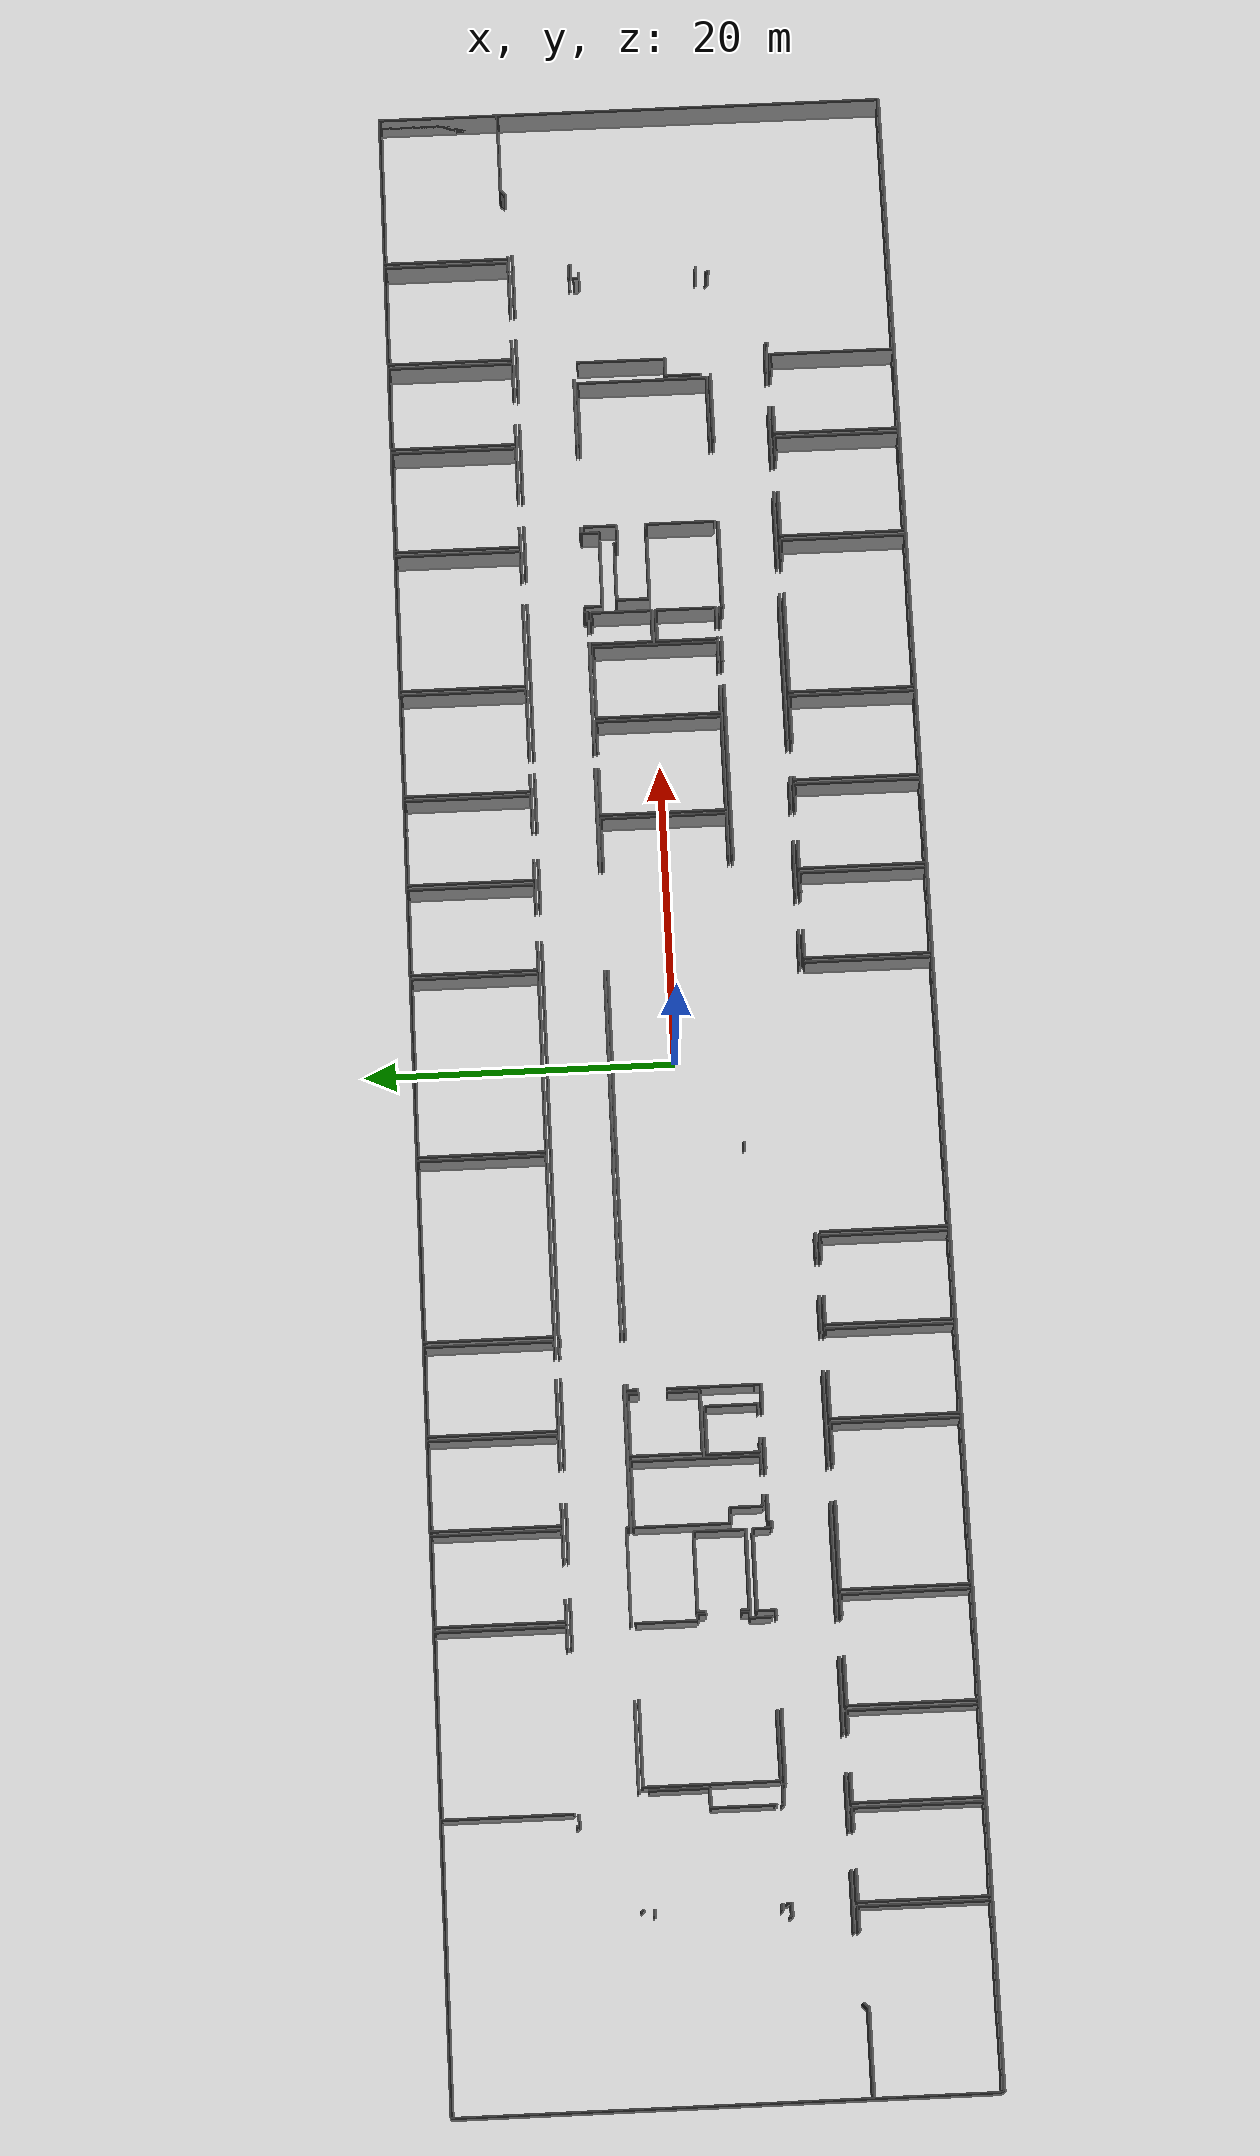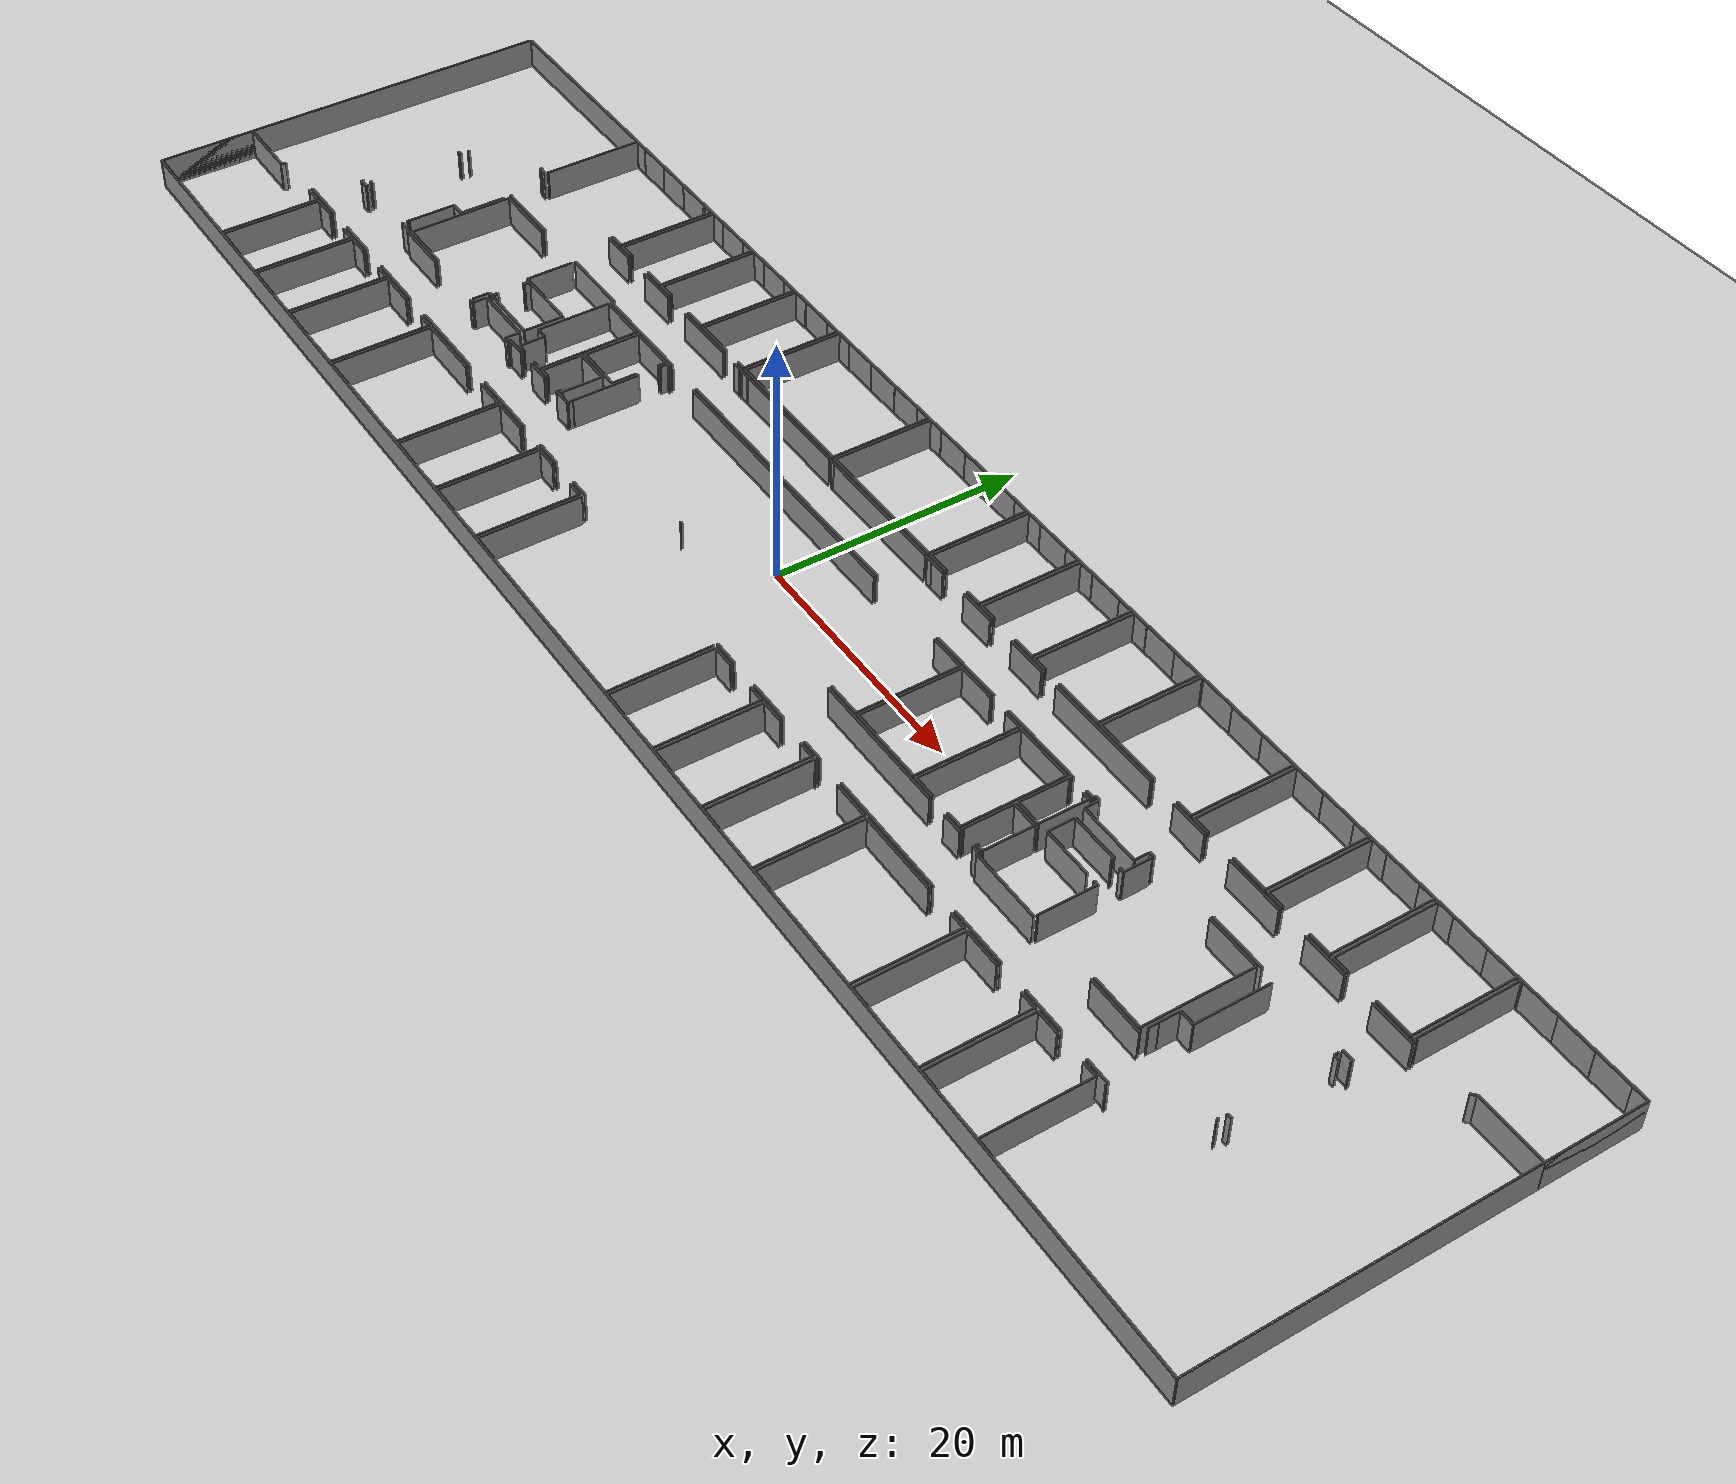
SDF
<sdf version="1.6">
  <world name="default">
    <light name="sun" type="directional">
      <cast_shadows>1</cast_shadows>
      <pose frame="">0 0 10 0 -0 0</pose>
      <diffuse>0.8 0.8 0.8 1</diffuse>
      <specular>0.1 0.1 0.1 1</specular>
      <attenuation>
        <range>1000</range>
        <constant>0.9</constant>
        <linear>0.01</linear>
        <quadratic>0.001</quadratic>
      </attenuation>
      <direction>-0.5 0.5 -1</direction>
    </light>
    <model name="ground_plane">
      <static>1</static>
      <link name="link">
        <collision name="collision">
          <geometry>
            <plane>
              <normal>0 0 1</normal>
              <size>100 100</size>
            </plane>
          </geometry>
          <surface>
            <friction>
              <ode>
                <mu>100</mu>
                <mu2>50</mu2>
              </ode>
              <torsional>
                <ode />
              </torsional>
            </friction>
            <contact>
              <ode />
            </contact>
            <bounce />
          </surface>
          <max_contacts>10</max_contacts>
        </collision>
        <visual name="visual">
          <cast_shadows>0</cast_shadows>
          <geometry>
            <plane>
              <normal>0 0 1</normal>
              <size>100 100</size>
            </plane>
          </geometry>
          <material>
            <script>
              <uri>file://media/materials/scripts/gazebo.material</uri>
              <name>Gazebo/Grey</name>
            </script>
          </material>
        </visual>
        <self_collide>0</self_collide>
        <kinematic>0</kinematic>
        <gravity>1</gravity>
      </link>
    </model>
    <gravity>0 0 -9.8</gravity>
    <magnetic_field>6e-06 2.3e-05 -4.2e-05</magnetic_field>
    <atmosphere type="adiabatic" />
    <physics default="0" name="default_physics" type="ode">
      <max_step_size>0.001</max_step_size>
      <real_time_factor>1</real_time_factor>
      <real_time_update_rate>1000</real_time_update_rate>
    </physics>
    <scene>
      <ambient>0.4 0.4 0.4 1</ambient>
      <background>0.7 0.7 0.7 1</background>
      <shadows>1</shadows>
    </scene>
    <spherical_coordinates>
      <surface_model>EARTH_WGS84</surface_model>
      <latitude_deg>0</latitude_deg>
      <longitude_deg>0</longitude_deg>
      <elevation>0</elevation>
      <heading_deg>0</heading_deg>
    </spherical_coordinates>
  <model name="50041172">
		<static>1</static>
		<link name="Wall_0">
			<collision name="Wall_0_Collision">
				<geometry>
					<box>
						<size>7.88504652123 0.1 2.5</size>
					</box>
				</geometry>
				<pose frame="">3.94252326061 0 1.25 0 0 0</pose>
			</collision>
			<visual name="Wall_0_Visual">
				<pose frame="">3.94252326061 0 1.25 0 0 0</pose>
				<geometry>
					<box>
						<size>7.88504652123 0.1 2.5</size>
					</box>
				</geometry>
				<material>
					<script>
						<uri>file://media/materials/scripts/gazebo.material</uri>
						<name>Gazebo/Grey</name>
					</script>
					<ambient>1 1 1 1</ambient>
				</material>
			</visual>
			<pose frame="">0.0 -33.542027881 0 0 0 1.57079632679</pose>
		</link>
		<link name="Wall_1">
			<collision name="Wall_1_Collision">
				<geometry>
					<box>
						<size>5.38922231749 0.1 2.5</size>
					</box>
				</geometry>
				<pose frame="">2.69461115874 0 1.25 0 0 0</pose>
			</collision>
			<visual name="Wall_1_Visual">
				<pose frame="">2.69461115874 0 1.25 0 0 0</pose>
				<geometry>
					<box>
						<size>5.38922231749 0.1 2.5</size>
					</box>
				</geometry>
				<material>
					<script>
						<uri>file://media/materials/scripts/gazebo.material</uri>
						<name>Gazebo/Grey</name>
					</script>
					<ambient>1 1 1 1</ambient>
				</material>
			</visual>
			<pose frame="">0.0 -25.6569813598 0 0 0 0.0</pose>
		</link>
		<link name="Wall_2">
			<collision name="Wall_2_Collision">
				<geometry>
					<box>
						<size>0.439427206756 0.1 2.5</size>
					</box>
				</geometry>
				<pose frame="">0.219713603378 0 1.25 0 0 0</pose>
			</collision>
			<visual name="Wall_2_Visual">
				<pose frame="">0.219713603378 0 1.25 0 0 0</pose>
				<geometry>
					<box>
						<size>0.439427206756 0.1 2.5</size>
					</box>
				</geometry>
				<material>
					<script>
						<uri>file://media/materials/scripts/gazebo.material</uri>
						<name>Gazebo/Grey</name>
					</script>
					<ambient>1 1 1 1</ambient>
				</material>
			</visual>
			<pose frame="">5.38922231749 -25.6569813598 0 0 0 0.799297513546</pose>
		</link>
		<link name="Wall_3">
			<collision name="Wall_3_Collision">
				<geometry>
					<box>
						<size>1.51370232765 0.1 2.5</size>
					</box>
				</geometry>
				<pose frame="">0.756851163825 0 1.25 0 0 0</pose>
			</collision>
			<visual name="Wall_3_Visual">
				<pose frame="">0.756851163825 0 1.25 0 0 0</pose>
				<geometry>
					<box>
						<size>1.51370232765 0.1 2.5</size>
					</box>
				</geometry>
				<material>
					<script>
						<uri>file://media/materials/scripts/gazebo.material</uri>
						<name>Gazebo/Grey</name>
					</script>
					<ambient>1 1 1 1</ambient>
				</material>
			</visual>
			<pose frame="">10.0130195929 -25.3419707218 0 0 0 0.0</pose>
		</link>
		<link name="Wall_4">
			<collision name="Wall_4_Collision">
				<geometry>
					<box>
						<size>8.20247054714 0.1 2.5</size>
					</box>
				</geometry>
				<pose frame="">4.10123527357 0 1.25 0 0 0</pose>
			</collision>
			<visual name="Wall_4_Visual">
				<pose frame="">4.10123527357 0 1.25 0 0 0</pose>
				<geometry>
					<box>
						<size>8.20247054714 0.1 2.5</size>
					</box>
				</geometry>
				<material>
					<script>
						<uri>file://media/materials/scripts/gazebo.material</uri>
						<name>Gazebo/Grey</name>
					</script>
					<ambient>1 1 1 1</ambient>
				</material>
			</visual>
			<pose frame="">11.5267219205 -25.3419707218 0 0 0 -1.57079632679</pose>
		</link>
		<link name="Wall_5">
			<collision name="Wall_5_Collision">
				<geometry>
					<box>
						<size>1.37499603061 0.1 2.5</size>
					</box>
				</geometry>
				<pose frame="">0.687498015306 0 1.25 0 0 0</pose>
			</collision>
			<visual name="Wall_5_Visual">
				<pose frame="">0.687498015306 0 1.25 0 0 0</pose>
				<geometry>
					<box>
						<size>1.37499603061 0.1 2.5</size>
					</box>
				</geometry>
				<material>
					<script>
						<uri>file://media/materials/scripts/gazebo.material</uri>
						<name>Gazebo/Grey</name>
					</script>
					<ambient>1 1 1 1</ambient>
				</material>
			</visual>
			<pose frame="">11.5267219205 -33.5444412689 0 0 0 3.14159265359</pose>
		</link>
		<link name="Wall_6">
			<collision name="Wall_6_Collision">
				<geometry>
					<box>
						<size>3.01178114382 0.1 2.5</size>
					</box>
				</geometry>
				<pose frame="">1.50589057191 0 1.25 0 0 0</pose>
			</collision>
			<visual name="Wall_6_Visual">
				<pose frame="">1.50589057191 0 1.25 0 0 0</pose>
				<geometry>
					<box>
						<size>3.01178114382 0.1 2.5</size>
					</box>
				</geometry>
				<material>
					<script>
						<uri>file://media/materials/scripts/gazebo.material</uri>
						<name>Gazebo/Grey</name>
					</script>
					<ambient>1 1 1 1</ambient>
				</material>
			</visual>
			<pose frame="">7.15734654346 -33.5444412689 0 0 0 3.14159265359</pose>
		</link>
		<link name="Wall_7">
			<collision name="Wall_7_Collision">
				<geometry>
					<box>
						<size>1.16846332243 0.1 2.5</size>
					</box>
				</geometry>
				<pose frame="">0.584231661216 0 1.25 0 0 0</pose>
			</collision>
			<visual name="Wall_7_Visual">
				<pose frame="">0.584231661216 0 1.25 0 0 0</pose>
				<geometry>
					<box>
						<size>1.16846332243 0.1 2.5</size>
					</box>
				</geometry>
				<material>
					<script>
						<uri>file://media/materials/scripts/gazebo.material</uri>
						<name>Gazebo/Grey</name>
					</script>
					<ambient>1 1 1 1</ambient>
				</material>
			</visual>
			<pose frame="">1.16846083008 -33.5444412689 0 0 0 3.13952721463</pose>
		</link>
		<link name="Wall_8">
			<collision name="Wall_8_Collision">
				<geometry>
					<box>
						<size>8.19789781207 0.1 2.5</size>
					</box>
				</geometry>
				<pose frame="">4.09894890604 0 1.25 0 0 0</pose>
			</collision>
			<visual name="Wall_8_Visual">
				<pose frame="">4.09894890604 0 1.25 0 0 0</pose>
				<geometry>
					<box>
						<size>8.19789781207 0.1 2.5</size>
					</box>
				</geometry>
				<material>
					<script>
						<uri>file://media/materials/scripts/gazebo.material</uri>
						<name>Gazebo/Grey</name>
					</script>
					<ambient>1 1 1 1</ambient>
				</material>
			</visual>
			<pose frame="">11.8021021879 -33.5377091868 0 0 0 1.57079632679</pose>
		</link>
		<link name="Wall_9">
			<collision name="Wall_9_Collision">
				<geometry>
					<box>
						<size>1.98202661078 0.1 2.5</size>
					</box>
				</geometry>
				<pose frame="">0.991013305389 0 1.25 0 0 0</pose>
			</collision>
			<visual name="Wall_9_Visual">
				<pose frame="">0.991013305389 0 1.25 0 0 0</pose>
				<geometry>
					<box>
						<size>1.98202661078 0.1 2.5</size>
					</box>
				</geometry>
				<material>
					<script>
						<uri>file://media/materials/scripts/gazebo.material</uri>
						<name>Gazebo/Grey</name>
					</script>
					<ambient>1 1 1 1</ambient>
				</material>
			</visual>
			<pose frame="">11.8021021879 -25.3398113747 0 0 0 0.0</pose>
		</link>
		<link name="Wall_10">
			<collision name="Wall_10_Collision">
				<geometry>
					<box>
						<size>1.37842558191 0.1 2.5</size>
					</box>
				</geometry>
				<pose frame="">0.689212790956 0 1.25 0 0 0</pose>
			</collision>
			<visual name="Wall_10_Visual">
				<pose frame="">0.689212790956 0 1.25 0 0 0</pose>
				<geometry>
					<box>
						<size>1.37842558191 0.1 2.5</size>
					</box>
				</geometry>
				<material>
					<script>
						<uri>file://media/materials/scripts/gazebo.material</uri>
						<name>Gazebo/Grey</name>
					</script>
					<ambient>1 1 1 1</ambient>
				</material>
			</visual>
			<pose frame="">16.1533136452 -25.3398113747 0 0 0 0.0</pose>
		</link>
		<link name="Wall_11">
			<collision name="Wall_11_Collision">
				<geometry>
					<box>
						<size>8.19637356705 0.1 2.5</size>
					</box>
				</geometry>
				<pose frame="">4.09818678353 0 1.25 0 0 0</pose>
			</collision>
			<visual name="Wall_11_Visual">
				<pose frame="">4.09818678353 0 1.25 0 0 0</pose>
				<geometry>
					<box>
						<size>8.19637356705 0.1 2.5</size>
					</box>
				</geometry>
				<material>
					<script>
						<uri>file://media/materials/scripts/gazebo.material</uri>
						<name>Gazebo/Grey</name>
					</script>
					<ambient>1 1 1 1</ambient>
				</material>
			</visual>
			<pose frame="">17.5317392271 -25.3398113747 0 0 0 -1.57079632679</pose>
		</link>
		<link name="Wall_12">
			<collision name="Wall_12_Collision">
				<geometry>
					<box>
						<size>1.37245562224 0.1 2.5</size>
					</box>
				</geometry>
				<pose frame="">0.686227811121 0 1.25 0 0 0</pose>
			</collision>
			<visual name="Wall_12_Visual">
				<pose frame="">0.686227811121 0 1.25 0 0 0</pose>
				<geometry>
					<box>
						<size>1.37245562224 0.1 2.5</size>
					</box>
				</geometry>
				<material>
					<script>
						<uri>file://media/materials/scripts/gazebo.material</uri>
						<name>Gazebo/Grey</name>
					</script>
					<ambient>1 1 1 1</ambient>
				</material>
			</visual>
			<pose frame="">17.5317392271 -33.5361849417 0 0 0 3.14159265359</pose>
		</link>
		<link name="Wall_13">
			<collision name="Wall_13_Collision">
				<geometry>
					<box>
						<size>1.3633110042 0.1 2.5</size>
					</box>
				</geometry>
				<pose frame="">0.681655502098 0 1.25 0 0 0</pose>
			</collision>
			<visual name="Wall_13_Visual">
				<pose frame="">0.681655502098 0 1.25 0 0 0</pose>
				<geometry>
					<box>
						<size>1.3633110042 0.1 2.5</size>
					</box>
				</geometry>
				<material>
					<script>
						<uri>file://media/materials/scripts/gazebo.material</uri>
						<name>Gazebo/Grey</name>
					</script>
					<ambient>1 1 1 1</ambient>
				</material>
			</visual>
			<pose frame="">13.16541234 -33.5361849417 0 0 0 -3.14047460691</pose>
		</link>
		<link name="Wall_14">
			<collision name="Wall_14_Collision">
				<geometry>
					<box>
						<size>8.20755136388 0.1 2.5</size>
					</box>
				</geometry>
				<pose frame="">4.10377568194 0 1.25 0 0 0</pose>
			</collision>
			<visual name="Wall_14_Visual">
				<pose frame="">4.10377568194 0 1.25 0 0 0</pose>
				<geometry>
					<box>
						<size>8.20755136388 0.1 2.5</size>
					</box>
				</geometry>
				<material>
					<script>
						<uri>file://media/materials/scripts/gazebo.material</uri>
						<name>Gazebo/Grey</name>
					</script>
					<ambient>1 1 1 1</ambient>
				</material>
			</visual>
			<pose frame="">17.8353180274 -33.5429170239 0 0 0 1.57079632679</pose>
		</link>
		<link name="Wall_15">
			<collision name="Wall_15_Collision">
				<geometry>
					<box>
						<size>1.82845892477 0.1 2.5</size>
					</box>
				</geometry>
				<pose frame="">0.914229462386 0 1.25 0 0 0</pose>
			</collision>
			<visual name="Wall_15_Visual">
				<pose frame="">0.914229462386 0 1.25 0 0 0</pose>
				<geometry>
					<box>
						<size>1.82845892477 0.1 2.5</size>
					</box>
				</geometry>
				<material>
					<script>
						<uri>file://media/materials/scripts/gazebo.material</uri>
						<name>Gazebo/Grey</name>
					</script>
					<ambient>1 1 1 1</ambient>
				</material>
			</visual>
			<pose frame="">17.8353180274 -25.33536566 0 0 0 0.0</pose>
		</link>
		<link name="Wall_16">
			<collision name="Wall_16_Collision">
				<geometry>
					<box>
						<size>1.36851798927 0.1 2.5</size>
					</box>
				</geometry>
				<pose frame="">0.684258994633 0 1.25 0 0 0</pose>
			</collision>
			<visual name="Wall_16_Visual">
				<pose frame="">0.684258994633 0 1.25 0 0 0</pose>
				<geometry>
					<box>
						<size>1.36851798927 0.1 2.5</size>
					</box>
				</geometry>
				<material>
					<script>
						<uri>file://media/materials/scripts/gazebo.material</uri>
						<name>Gazebo/Grey</name>
					</script>
					<ambient>1 1 1 1</ambient>
				</material>
			</visual>
			<pose frame="">22.1465180528 -25.33536566 0 0 0 0.0</pose>
		</link>
		<link name="Wall_17">
			<collision name="Wall_17_Collision">
				<geometry>
					<box>
						<size>8.22571528373 0.1 2.5</size>
					</box>
				</geometry>
				<pose frame="">4.11285764187 0 1.25 0 0 0</pose>
			</collision>
			<visual name="Wall_17_Visual">
				<pose frame="">4.11285764187 0 1.25 0 0 0</pose>
				<geometry>
					<box>
						<size>8.22571528373 0.1 2.5</size>
					</box>
				</geometry>
				<material>
					<script>
						<uri>file://media/materials/scripts/gazebo.material</uri>
						<name>Gazebo/Grey</name>
					</script>
					<ambient>1 1 1 1</ambient>
				</material>
			</visual>
			<pose frame="">23.515036042 -25.33536566 0 0 0 -1.57079632679</pose>
		</link>
		<link name="Wall_18">
			<collision name="Wall_18_Collision">
				<geometry>
					<box>
						<size>1.35149725318 0.1 2.5</size>
					</box>
				</geometry>
				<pose frame="">0.675748626592 0 1.25 0 0 0</pose>
			</collision>
			<visual name="Wall_18_Visual">
				<pose frame="">0.675748626592 0 1.25 0 0 0</pose>
				<geometry>
					<box>
						<size>1.35149725318 0.1 2.5</size>
					</box>
				</geometry>
				<material>
					<script>
						<uri>file://media/materials/scripts/gazebo.material</uri>
						<name>Gazebo/Grey</name>
					</script>
					<ambient>1 1 1 1</ambient>
				</material>
			</visual>
			<pose frame="">23.515036042 -33.5610809438 0 0 0 3.14159265359</pose>
		</link>
		<link name="Wall_19">
			<collision name="Wall_19_Collision">
				<geometry>
					<box>
						<size>1.31440578116 0.1 2.5</size>
					</box>
				</geometry>
				<pose frame="">0.657202890581 0 1.25 0 0 0</pose>
			</collision>
			<visual name="Wall_19_Visual">
				<pose frame="">0.657202890581 0 1.25 0 0 0</pose>
				<geometry>
					<box>
						<size>1.31440578116 0.1 2.5</size>
					</box>
				</geometry>
				<material>
					<script>
						<uri>file://media/materials/scripts/gazebo.material</uri>
						<name>Gazebo/Grey</name>
					</script>
					<ambient>1 1 1 1</ambient>
				</material>
			</visual>
			<pose frame="">19.1495982979 -33.5610809438 0 0 0 3.12777310237</pose>
		</link>
		<link name="Wall_20">
			<collision name="Wall_20_Collision">
				<geometry>
					<box>
						<size>8.21415642565 0.1 2.5</size>
					</box>
				</geometry>
				<pose frame="">4.10707821282 0 1.25 0 0 0</pose>
			</collision>
			<visual name="Wall_20_Visual">
				<pose frame="">4.10707821282 0 1.25 0 0 0</pose>
				<geometry>
					<box>
						<size>8.21415642565 0.1 2.5</size>
					</box>
				</geometry>
				<material>
					<script>
						<uri>file://media/materials/scripts/gazebo.material</uri>
						<name>Gazebo/Grey</name>
					</script>
					<ambient>1 1 1 1</ambient>
				</material>
			</visual>
			<pose frame="">23.8111206376 -33.5537137595 0 0 0 1.57079632679</pose>
		</link>
		<link name="Wall_21">
			<collision name="Wall_21_Collision">
				<geometry>
					<box>
						<size>3.0657648217 0.1 2.5</size>
					</box>
				</geometry>
				<pose frame="">1.53288241085 0 1.25 0 0 0</pose>
			</collision>
			<visual name="Wall_21_Visual">
				<pose frame="">1.53288241085 0 1.25 0 0 0</pose>
				<geometry>
					<box>
						<size>3.0657648217 0.1 2.5</size>
					</box>
				</geometry>
				<material>
					<script>
						<uri>file://media/materials/scripts/gazebo.material</uri>
						<name>Gazebo/Grey</name>
					</script>
					<ambient>1 1 1 1</ambient>
				</material>
			</visual>
			<pose frame="">23.8111206376 -25.3395573338 0 0 0 0.0</pose>
		</link>
		<link name="Wall_22">
			<collision name="Wall_22_Collision">
				<geometry>
					<box>
						<size>1.3625480296 0.1 2.5</size>
					</box>
				</geometry>
				<pose frame="">0.681274014798 0 1.25 0 0 0</pose>
			</collision>
			<visual name="Wall_22_Visual">
				<pose frame="">0.681274014798 0 1.25 0 0 0</pose>
				<geometry>
					<box>
						<size>1.3625480296 0.1 2.5</size>
					</box>
				</geometry>
				<material>
					<script>
						<uri>file://media/materials/scripts/gazebo.material</uri>
						<name>Gazebo/Grey</name>
					</script>
					<ambient>1 1 1 1</ambient>
				</material>
			</visual>
			<pose frame="">29.3560699883 -25.3395573338 0 0 0 0.0</pose>
		</link>
		<link name="Wall_23">
			<collision name="Wall_23_Collision">
				<geometry>
					<box>
						<size>8.19815185291 0.1 2.5</size>
					</box>
				</geometry>
				<pose frame="">4.09907592646 0 1.25 0 0 0</pose>
			</collision>
			<visual name="Wall_23_Visual">
				<pose frame="">4.09907592646 0 1.25 0 0 0</pose>
				<geometry>
					<box>
						<size>8.19815185291 0.1 2.5</size>
					</box>
				</geometry>
				<material>
					<script>
						<uri>file://media/materials/scripts/gazebo.material</uri>
						<name>Gazebo/Grey</name>
					</script>
					<ambient>1 1 1 1</ambient>
				</material>
			</visual>
			<pose frame="">30.7186180178 -25.3395573338 0 0 0 -1.57079632679</pose>
		</link>
		<link name="Wall_24">
			<collision name="Wall_24_Collision">
				<geometry>
					<box>
						<size>2.54942682036 0.1 2.5</size>
					</box>
				</geometry>
				<pose frame="">1.27471341018 0 1.25 0 0 0</pose>
			</collision>
			<visual name="Wall_24_Visual">
				<pose frame="">1.27471341018 0 1.25 0 0 0</pose>
				<geometry>
					<box>
						<size>2.54942682036 0.1 2.5</size>
					</box>
				</geometry>
				<material>
					<script>
						<uri>file://media/materials/scripts/gazebo.material</uri>
						<name>Gazebo/Grey</name>
					</script>
					<ambient>1 1 1 1</ambient>
				</material>
			</visual>
			<pose frame="">30.7186180178 -33.5377091868 0 0 0 3.14159265359</pose>
		</link>
		<link name="Wall_25">
			<collision name="Wall_25_Collision">
				<geometry>
					<box>
						<size>1.34625753171 0.1 2.5</size>
					</box>
				</geometry>
				<pose frame="">0.673128765856 0 1.25 0 0 0</pose>
			</collision>
			<visual name="Wall_25_Visual">
				<pose frame="">0.673128765856 0 1.25 0 0 0</pose>
				<geometry>
					<box>
						<size>1.34625753171 0.1 2.5</size>
					</box>
				</geometry>
				<material>
					<script>
						<uri>file://media/materials/scripts/gazebo.material</uri>
						<name>Gazebo/Grey</name>
					</script>
					<ambient>1 1 1 1</ambient>
				</material>
			</visual>
			<pose frame="">25.1572830332 -33.5377091868 0 0 0 -3.12970417804</pose>
		</link>
		<link name="Wall_26">
			<collision name="Wall_26_Collision">
				<geometry>
					<box>
						<size>8.20704328221 0.1 2.5</size>
					</box>
				</geometry>
				<pose frame="">4.1035216411 0 1.25 0 0 0</pose>
			</collision>
			<visual name="Wall_26_Visual">
				<pose frame="">4.1035216411 0 1.25 0 0 0</pose>
				<geometry>
					<box>
						<size>8.20704328221 0.1 2.5</size>
					</box>
				</geometry>
				<material>
					<script>
						<uri>file://media/materials/scripts/gazebo.material</uri>
						<name>Gazebo/Grey</name>
					</script>
					<ambient>1 1 1 1</ambient>
				</material>
			</visual>
			<pose frame="">31.0204185323 -33.5486329427 0 0 0 1.57079632679</pose>
		</link>
		<link name="Wall_27">
			<collision name="Wall_27_Collision">
				<geometry>
					<box>
						<size>5.56692388301 0.1 2.5</size>
					</box>
				</geometry>
				<pose frame="">2.78346194151 0 1.25 0 0 0</pose>
			</collision>
			<visual name="Wall_27_Visual">
				<pose frame="">2.78346194151 0 1.25 0 0 0</pose>
				<geometry>
					<box>
						<size>5.56692388301 0.1 2.5</size>
					</box>
				</geometry>
				<material>
					<script>
						<uri>file://media/materials/scripts/gazebo.material</uri>
						<name>Gazebo/Grey</name>
					</script>
					<ambient>1 1 1 1</ambient>
				</material>
			</visual>
			<pose frame="">31.0204185323 -25.3415896605 0 0 0 0.0</pose>
		</link>
		<link name="Wall_28">
			<collision name="Wall_28_Collision">
				<geometry>
					<box>
						<size>2.57114731193 0.1 2.5</size>
					</box>
				</geometry>
				<pose frame="">1.28557365597 0 1.25 0 0 0</pose>
			</collision>
			<visual name="Wall_28_Visual">
				<pose frame="">1.28557365597 0 1.25 0 0 0</pose>
				<geometry>
					<box>
						<size>2.57114731193 0.1 2.5</size>
					</box>
				</geometry>
				<material>
					<script>
						<uri>file://media/materials/scripts/gazebo.material</uri>
						<name>Gazebo/Grey</name>
					</script>
					<ambient>1 1 1 1</ambient>
				</material>
			</visual>
			<pose frame="">38.9472547712 -25.3415896605 0 0 0 0.0</pose>
		</link>
		<link name="Wall_29">
			<collision name="Wall_29_Collision">
				<geometry>
					<box>
						<size>8.20132736337 0.1 2.5</size>
					</box>
				</geometry>
				<pose frame="">4.10066368169 0 1.25 0 0 0</pose>
			</collision>
			<visual name="Wall_29_Visual">
				<pose frame="">4.10066368169 0 1.25 0 0 0</pose>
				<geometry>
					<box>
						<size>8.20132736337 0.1 2.5</size>
					</box>
				</geometry>
				<material>
					<script>
						<uri>file://media/materials/scripts/gazebo.material</uri>
						<name>Gazebo/Grey</name>
					</script>
					<ambient>1 1 1 1</ambient>
				</material>
			</visual>
			<pose frame="">41.5184020831 -25.3415896605 0 0 0 -1.57079632679</pose>
		</link>
		<link name="Wall_30">
			<collision name="Wall_30_Collision">
				<geometry>
					<box>
						<size>1.35797529453 0.1 2.5</size>
					</box>
				</geometry>
				<pose frame="">0.678987647264 0 1.25 0 0 0</pose>
			</collision>
			<visual name="Wall_30_Visual">
				<pose frame="">0.678987647264 0 1.25 0 0 0</pose>
				<geometry>
					<box>
						<size>1.35797529453 0.1 2.5</size>
					</box>
				</geometry>
				<material>
					<script>
						<uri>file://media/materials/scripts/gazebo.material</uri>
						<name>Gazebo/Grey</name>
					</script>
					<ambient>1 1 1 1</ambient>
				</material>
			</visual>
			<pose frame="">41.5184020831 -33.5429170239 0 0 0 3.14159265359</pose>
		</link>
		<link name="Wall_31">
			<collision name="Wall_31_Collision">
				<geometry>
					<box>
						<size>3.03947159506 0.1 2.5</size>
					</box>
				</geometry>
				<pose frame="">1.51973579753 0 1.25 0 0 0</pose>
			</collision>
			<visual name="Wall_31_Visual">
				<pose frame="">1.51973579753 0 1.25 0 0 0</pose>
				<geometry>
					<box>
						<size>3.03947159506 0.1 2.5</size>
					</box>
				</geometry>
				<material>
					<script>
						<uri>file://media/materials/scripts/gazebo.material</uri>
						<name>Gazebo/Grey</name>
					</script>
					<ambient>1 1 1 1</ambient>
				</material>
			</visual>
			<pose frame="">37.1824330761 -33.5429170239 0 0 0 3.14159265359</pose>
		</link>
		<link name="Wall_32">
			<collision name="Wall_32_Collision">
				<geometry>
					<box>
						<size>0.160147764803 0.1 2.5</size>
					</box>
				</geometry>
				<pose frame="">0.0800738824014 0 1.25 0 0 0</pose>
			</collision>
			<visual name="Wall_32_Visual">
				<pose frame="">0.0800738824014 0 1.25 0 0 0</pose>
				<geometry>
					<box>
						<size>0.160147764803 0.1 2.5</size>
					</box>
				</geometry>
				<material>
					<script>
						<uri>file://media/materials/scripts/gazebo.material</uri>
						<name>Gazebo/Grey</name>
					</script>
					<ambient>1 1 1 1</ambient>
				</material>
			</visual>
			<pose frame="">31.1804642596 -33.5429170239 0 0 0 -3.10589354091</pose>
		</link>
		<link name="Wall_33">
			<collision name="Wall_33_Collision">
				<geometry>
					<box>
						<size>8.22292083452 0.1 2.5</size>
					</box>
				</geometry>
				<pose frame="">4.11146041726 0 1.25 0 0 0</pose>
			</collision>
			<visual name="Wall_33_Visual">
				<pose frame="">4.11146041726 0 1.25 0 0 0</pose>
				<geometry>
					<box>
						<size>8.22292083452 0.1 2.5</size>
					</box>
				</geometry>
				<material>
					<script>
						<uri>file://media/materials/scripts/gazebo.material</uri>
						<name>Gazebo/Grey</name>
					</script>
					<ambient>1 1 1 1</ambient>
				</material>
			</visual>
			<pose frame="">41.8068654536 -33.5500301673 0 0 0 1.57079632679</pose>
		</link>
		<link name="Wall_34">
			<collision name="Wall_34_Collision">
				<geometry>
					<box>
						<size>3.06411355625 0.1 2.5</size>
					</box>
				</geometry>
				<pose frame="">1.53205677813 0 1.25 0 0 0</pose>
			</collision>
			<visual name="Wall_34_Visual">
				<pose frame="">1.53205677813 0 1.25 0 0 0</pose>
				<geometry>
					<box>
						<size>3.06411355625 0.1 2.5</size>
					</box>
				</geometry>
				<material>
					<script>
						<uri>file://media/materials/scripts/gazebo.material</uri>
						<name>Gazebo/Grey</name>
					</script>
					<ambient>1 1 1 1</ambient>
				</material>
			</visual>
			<pose frame="">41.8068654536 -25.3271093328 0 0 0 0.0</pose>
		</link>
		<link name="Wall_35">
			<collision name="Wall_35_Collision">
				<geometry>
					<box>
						<size>0.176939443015 0.1 2.5</size>
					</box>
				</geometry>
				<pose frame="">0.0884697215077 0 1.25 0 0 0</pose>
			</collision>
			<visual name="Wall_35_Visual">
				<pose frame="">0.0884697215077 0 1.25 0 0 0</pose>
				<geometry>
					<box>
						<size>0.176939443015 0.1 2.5</size>
					</box>
				</geometry>
				<material>
					<script>
						<uri>file://media/materials/scripts/gazebo.material</uri>
						<name>Gazebo/Grey</name>
					</script>
					<ambient>1 1 1 1</ambient>
				</material>
			</visual>
			<pose frame="">47.3492743959 -25.3271093328 0 0 0 0.0</pose>
		</link>
		<link name="Wall_36">
			<collision name="Wall_36_Collision">
				<geometry>
					<box>
						<size>8.21021879267 0.1 2.5</size>
					</box>
				</geometry>
				<pose frame="">4.10510939634 0 1.25 0 0 0</pose>
			</collision>
			<visual name="Wall_36_Visual">
				<pose frame="">4.10510939634 0 1.25 0 0 0</pose>
				<geometry>
					<box>
						<size>8.21021879267 0.1 2.5</size>
					</box>
				</geometry>
				<material>
					<script>
						<uri>file://media/materials/scripts/gazebo.material</uri>
						<name>Gazebo/Grey</name>
					</script>
					<ambient>1 1 1 1</ambient>
				</material>
			</visual>
			<pose frame="">47.5262138389 -25.3271093328 0 0 0 -1.57079632679</pose>
		</link>
		<link name="Wall_37">
			<collision name="Wall_37_Collision">
				<geometry>
					<box>
						<size>1.36407227462 0.1 2.5</size>
					</box>
				</geometry>
				<pose frame="">0.682036137309 0 1.25 0 0 0</pose>
			</collision>
			<visual name="Wall_37_Visual">
				<pose frame="">0.682036137309 0 1.25 0 0 0</pose>
				<geometry>
					<box>
						<size>1.36407227462 0.1 2.5</size>
					</box>
				</geometry>
				<material>
					<script>
						<uri>file://media/materials/scripts/gazebo.material</uri>
						<name>Gazebo/Grey</name>
					</script>
					<ambient>1 1 1 1</ambient>
				</material>
			</visual>
			<pose frame="">47.5262138389 -33.5373281255 0 0 0 3.14159265359</pose>
		</link>
		<link name="Wall_38">
			<collision name="Wall_38_Collision">
				<geometry>
					<box>
						<size>1.37365753437 0.1 2.5</size>
					</box>
				</geometry>
				<pose frame="">0.686828767185 0 1.25 0 0 0</pose>
			</collision>
			<visual name="Wall_38_Visual">
				<pose frame="">0.686828767185 0 1.25 0 0 0</pose>
				<geometry>
					<box>
						<size>1.37365753437 0.1 2.5</size>
					</box>
				</geometry>
				<material>
					<script>
						<uri>file://media/materials/scripts/gazebo.material</uri>
						<name>Gazebo/Grey</name>
					</script>
					<ambient>1 1 1 1</ambient>
				</material>
			</visual>
			<pose frame="">43.1804642596 -33.5373281255 0 0 0 -3.13234564511</pose>
		</link>
		<link name="Wall_39">
			<collision name="Wall_39_Collision">
				<geometry>
					<box>
						<size>8.20043822044 0.1 2.5</size>
					</box>
				</geometry>
				<pose frame="">4.10021911022 0 1.25 0 0 0</pose>
			</collision>
			<visual name="Wall_39_Visual">
				<pose frame="">4.10021911022 0 1.25 0 0 0</pose>
				<geometry>
					<box>
						<size>8.20043822044 0.1 2.5</size>
					</box>
				</geometry>
				<material>
					<script>
						<uri>file://media/materials/scripts/gazebo.material</uri>
						<name>Gazebo/Grey</name>
					</script>
					<ambient>1 1 1 1</ambient>
				</material>
			</visual>
			<pose frame="">47.8216633324 -33.542027881 0 0 0 1.57079632679</pose>
		</link>
		<link name="Wall_40">
			<collision name="Wall_40_Collision">
				<geometry>
					<box>
						<size>1.8539900289 0.1 2.5</size>
					</box>
				</geometry>
				<pose frame="">0.926995014449 0 1.25 0 0 0</pose>
			</collision>
			<visual name="Wall_40_Visual">
				<pose frame="">0.926995014449 0 1.25 0 0 0</pose>
				<geometry>
					<box>
						<size>1.8539900289 0.1 2.5</size>
					</box>
				</geometry>
				<material>
					<script>
						<uri>file://media/materials/scripts/gazebo.material</uri>
						<name>Gazebo/Grey</name>
					</script>
					<ambient>1 1 1 1</ambient>
				</material>
			</visual>
			<pose frame="">47.8216633324 -25.3415896605 0 0 0 0.0</pose>
		</link>
		<link name="Wall_41">
			<collision name="Wall_41_Collision">
				<geometry>
					<box>
						<size>1.37512305103 0.1 2.5</size>
					</box>
				</geometry>
				<pose frame="">0.687561525515 0 1.25 0 0 0</pose>
			</collision>
			<visual name="Wall_41_Visual">
				<pose frame="">0.687561525515 0 1.25 0 0 0</pose>
				<geometry>
					<box>
						<size>1.37512305103 0.1 2.5</size>
					</box>
				</geometry>
				<material>
					<script>
						<uri>file://media/materials/scripts/gazebo.material</uri>
						<name>Gazebo/Grey</name>
					</script>
					<ambient>1 1 1 1</ambient>
				</material>
			</visual>
			<pose frame="">52.1506462164 -25.3415896605 0 0 0 0.0</pose>
		</link>
		<link name="Wall_42">
			<collision name="Wall_42_Collision">
				<geometry>
					<box>
						<size>8.19573846496 0.1 2.5</size>
					</box>
				</geometry>
				<pose frame="">4.09786923248 0 1.25 0 0 0</pose>
			</collision>
			<visual name="Wall_42_Visual">
				<pose frame="">4.09786923248 0 1.25 0 0 0</pose>
				<geometry>
					<box>
						<size>8.19573846496 0.1 2.5</size>
					</box>
				</geometry>
				<material>
					<script>
						<uri>file://media/materials/scripts/gazebo.material</uri>
						<name>Gazebo/Grey</name>
					</script>
					<ambient>1 1 1 1</ambient>
				</material>
			</visual>
			<pose frame="">53.5257692674 -25.3415896605 0 0 0 -1.57079632679</pose>
		</link>
		<link name="Wall_43">
			<collision name="Wall_43_Collision">
				<geometry>
					<box>
						<size>1.36292909085 0.1 2.5</size>
					</box>
				</geometry>
				<pose frame="">0.681464545426 0 1.25 0 0 0</pose>
			</collision>
			<visual name="Wall_43_Visual">
				<pose frame="">0.681464545426 0 1.25 0 0 0</pose>
				<geometry>
					<box>
						<size>1.36292909085 0.1 2.5</size>
					</box>
				</geometry>
				<material>
					<script>
						<uri>file://media/materials/scripts/gazebo.material</uri>
						<name>Gazebo/Grey</name>
					</script>
					<ambient>1 1 1 1</ambient>
				</material>
			</visual>
			<pose frame="">53.5257692674 -33.5373281255 0 0 0 3.14159265359</pose>
		</link>
		<link name="Wall_44">
			<collision name="Wall_44_Collision">
				<geometry>
					<box>
						<size>1.3588725647 0.1 2.5</size>
					</box>
				</geometry>
				<pose frame="">0.679436282349 0 1.25 0 0 0</pose>
			</collision>
			<visual name="Wall_44_Visual">
				<pose frame="">0.679436282349 0 1.25 0 0 0</pose>
				<geometry>
					<box>
						<size>1.3588725647 0.1 2.5</size>
					</box>
				</geometry>
				<material>
					<script>
						<uri>file://media/materials/scripts/gazebo.material</uri>
						<name>Gazebo/Grey</name>
					</script>
					<ambient>1 1 1 1</ambient>
				</material>
			</visual>
			<pose frame="">49.1805277698 -33.5373281255 0 0 0 -3.13813407699</pose>
		</link>
		<link name="Wall_45">
			<collision name="Wall_45_Collision">
				<geometry>
					<box>
						<size>8.20551903719 0.1 2.5</size>
					</box>
				</geometry>
				<pose frame="">4.10275951859 0 1.25 0 0 0</pose>
			</collision>
			<visual name="Wall_45_Visual">
				<pose frame="">4.10275951859 0 1.25 0 0 0</pose>
				<geometry>
					<box>
						<size>8.20551903719 0.1 2.5</size>
					</box>
				</geometry>
				<material>
					<script>
						<uri>file://media/materials/scripts/gazebo.material</uri>
						<name>Gazebo/Grey</name>
					</script>
					<ambient>1 1 1 1</ambient>
				</material>
			</visual>
			<pose frame="">53.8153758217 -33.5453304119 0 0 0 1.57079632679</pose>
		</link>
		<link name="Wall_46">
			<collision name="Wall_46_Collision">
				<geometry>
					<box>
						<size>8.21021879267 0.1 2.5</size>
					</box>
				</geometry>
				<pose frame="">4.10510939634 0 1.25 0 0 0</pose>
			</collision>
			<visual name="Wall_46_Visual">
				<pose frame="">4.10510939634 0 1.25 0 0 0</pose>
				<geometry>
					<box>
						<size>8.21021879267 0.1 2.5</size>
					</box>
				</geometry>
				<material>
					<script>
						<uri>file://media/materials/scripts/gazebo.material</uri>
						<name>Gazebo/Grey</name>
					</script>
					<ambient>1 1 1 1</ambient>
				</material>
			</visual>
			<pose frame="">71.5291353085 -25.3398113747 0 0 0 -1.57079632679</pose>
		</link>
		<link name="Wall_47">
			<collision name="Wall_47_Collision">
				<geometry>
					<box>
						<size>1.37093137722 0.1 2.5</size>
					</box>
				</geometry>
				<pose frame="">0.685465688609 0 1.25 0 0 0</pose>
			</collision>
			<visual name="Wall_47_Visual">
				<pose frame="">0.685465688609 0 1.25 0 0 0</pose>
				<geometry>
					<box>
						<size>1.37093137722 0.1 2.5</size>
					</box>
				</geometry>
				<material>
					<script>
						<uri>file://media/materials/scripts/gazebo.material</uri>
						<name>Gazebo/Grey</name>
					</script>
					<ambient>1 1 1 1</ambient>
				</material>
			</visual>
			<pose frame="">71.5291353085 -33.5500301673 0 0 0 3.14159265359</pose>
		</link>
		<link name="Wall_48">
			<collision name="Wall_48_Collision">
				<geometry>
					<box>
						<size>3.02181575688 0.1 2.5</size>
					</box>
				</geometry>
				<pose frame="">1.51090787844 0 1.25 0 0 0</pose>
			</collision>
			<visual name="Wall_48_Visual">
				<pose frame="">1.51090787844 0 1.25 0 0 0</pose>
				<geometry>
					<box>
						<size>3.02181575688 0.1 2.5</size>
					</box>
				</geometry>
				<material>
					<script>
						<uri>file://media/materials/scripts/gazebo.material</uri>
						<name>Gazebo/Grey</name>
					</script>
					<ambient>1 1 1 1</ambient>
				</material>
			</visual>
			<pose frame="">67.186053158 -33.5500301673 0 0 0 3.14159265359</pose>
		</link>
		<link name="Wall_49">
			<collision name="Wall_49_Collision">
				<geometry>
					<box>
						<size>3.02156171605 0.1 2.5</size>
					</box>
				</geometry>
				<pose frame="">1.51078085802 0 1.25 0 0 0</pose>
			</collision>
			<visual name="Wall_49_Visual">
				<pose frame="">1.51078085802 0 1.25 0 0 0</pose>
				<geometry>
					<box>
						<size>3.02156171605 0.1 2.5</size>
					</box>
				</geometry>
				<material>
					<script>
						<uri>file://media/materials/scripts/gazebo.material</uri>
						<name>Gazebo/Grey</name>
					</script>
					<ambient>1 1 1 1</ambient>
				</material>
			</visual>
			<pose frame="">61.1828141374 -33.5500301673 0 0 0 3.14159265359</pose>
		</link>
		<link name="Wall_50">
			<collision name="Wall_50_Collision">
				<geometry>
					<box>
						<size>1.36509652815 0.1 2.5</size>
					</box>
				</geometry>
				<pose frame="">0.682548264076 0 1.25 0 0 0</pose>
			</collision>
			<visual name="Wall_50_Visual">
				<pose frame="">0.682548264076 0 1.25 0 0 0</pose>
				<geometry>
					<box>
						<size>1.36509652815 0.1 2.5</size>
					</box>
				</geometry>
				<material>
					<script>
						<uri>file://media/materials/scripts/gazebo.material</uri>
						<name>Gazebo/Grey</name>
					</script>
					<ambient>1 1 1 1</ambient>
				</material>
			</visual>
			<pose frame="">55.1804642596 -33.5500301673 0 0 0 3.13814984594</pose>
		</link>
		<link name="Wall_51">
			<collision name="Wall_51_Collision">
				<geometry>
					<box>
						<size>8.21034581309 0.1 2.5</size>
					</box>
				</geometry>
				<pose frame="">4.10517290654 0 1.25 0 0 0</pose>
			</collision>
			<visual name="Wall_51_Visual">
				<pose frame="">4.10517290654 0 1.25 0 0 0</pose>
				<geometry>
					<box>
						<size>8.21034581309 0.1 2.5</size>
					</box>
				</geometry>
				<material>
					<script>
						<uri>file://media/materials/scripts/gazebo.material</uri>
						<name>Gazebo/Grey</name>
					</script>
					<ambient>1 1 1 1</ambient>
				</material>
			</visual>
			<pose frame="">71.8113746785 -33.5492680448 0 0 0 1.57079632679</pose>
		</link>
		<link name="Wall_52">
			<collision name="Wall_52_Collision">
				<geometry>
					<box>
						<size>1.86097615192 0.1 2.5</size>
					</box>
				</geometry>
				<pose frame="">0.930488075958 0 1.25 0 0 0</pose>
			</collision>
			<visual name="Wall_52_Visual">
				<pose frame="">0.930488075958 0 1.25 0 0 0</pose>
				<geometry>
					<box>
						<size>1.86097615192 0.1 2.5</size>
					</box>
				</geometry>
				<material>
					<script>
						<uri>file://media/materials/scripts/gazebo.material</uri>
						<name>Gazebo/Grey</name>
					</script>
					<ambient>1 1 1 1</ambient>
				</material>
			</visual>
			<pose frame="">71.8113746785 -25.3389222317 0 0 0 0.0</pose>
		</link>
		<link name="Wall_53">
			<collision name="Wall_53_Collision">
				<geometry>
					<box>
						<size>1.36483439713 0.1 2.5</size>
					</box>
				</geometry>
				<pose frame="">0.682417198565 0 1.25 0 0 0</pose>
			</collision>
			<visual name="Wall_53_Visual">
				<pose frame="">0.682417198565 0 1.25 0 0 0</pose>
				<geometry>
					<box>
						<size>1.36483439713 0.1 2.5</size>
					</box>
				</geometry>
				<material>
					<script>
						<uri>file://media/materials/scripts/gazebo.material</uri>
						<name>Gazebo/Grey</name>
					</script>
					<ambient>1 1 1 1</ambient>
				</material>
			</visual>
			<pose frame="">76.1556000127 -25.3389222317 0 0 0 0.0</pose>
		</link>
		<link name="Wall_54">
			<collision name="Wall_54_Collision">
				<geometry>
					<box>
						<size>8.204248833 0.1 2.5</size>
					</box>
				</geometry>
				<pose frame="">4.1021244165 0 1.25 0 0 0</pose>
			</collision>
			<visual name="Wall_54_Visual">
				<pose frame="">4.1021244165 0 1.25 0 0 0</pose>
				<geometry>
					<box>
						<size>8.204248833 0.1 2.5</size>
					</box>
				</geometry>
				<material>
					<script>
						<uri>file://media/materials/scripts/gazebo.material</uri>
						<name>Gazebo/Grey</name>
					</script>
					<ambient>1 1 1 1</ambient>
				</material>
			</visual>
			<pose frame="">77.5204344098 -25.3389222317 0 0 0 -1.57079632679</pose>
		</link>
		<link name="Wall_55">
			<collision name="Wall_55_Collision">
				<geometry>
					<box>
						<size>1.35899145788 0.1 2.5</size>
					</box>
				</geometry>
				<pose frame="">0.679495728938 0 1.25 0 0 0</pose>
			</collision>
			<visual name="Wall_55_Visual">
				<pose frame="">0.679495728938 0 1.25 0 0 0</pose>
				<geometry>
					<box>
						<size>1.35899145788 0.1 2.5</size>
					</box>
				</geometry>
				<material>
					<script>
						<uri>file://media/materials/scripts/gazebo.material</uri>
						<name>Gazebo/Grey</name>
					</script>
					<ambient>1 1 1 1</ambient>
				</material>
			</visual>
			<pose frame="">77.5204344098 -33.5431710647 0 0 0 3.14159265359</pose>
		</link>
		<link name="Wall_56">
			<collision name="Wall_56_Collision">
				<geometry>
					<box>
						<size>1.35798898144 0.1 2.5</size>
					</box>
				</geometry>
				<pose frame="">0.678994490721 0 1.25 0 0 0</pose>
			</collision>
			<visual name="Wall_56_Visual">
				<pose frame="">0.678994490721 0 1.25 0 0 0</pose>
				<geometry>
					<box>
						<size>1.35798898144 0.1 2.5</size>
					</box>
				</geometry>
				<material>
					<script>
						<uri>file://media/materials/scripts/gazebo.material</uri>
						<name>Gazebo/Grey</name>
					</script>
					<ambient>1 1 1 1</ambient>
				</material>
			</visual>
			<pose frame="">73.169349973 -33.5431710647 0 0 0 -3.13710292602</pose>
		</link>
		<link name="Wall_57">
			<collision name="Wall_57_Collision">
				<geometry>
					<box>
						<size>8.22177765076 0.1 2.5</size>
					</box>
				</geometry>
				<pose frame="">4.11088882538 0 1.25 0 0 0</pose>
			</collision>
			<visual name="Wall_57_Visual">
				<pose frame="">4.11088882538 0 1.25 0 0 0</pose>
				<geometry>
					<box>
						<size>8.22177765076 0.1 2.5</size>
					</box>
				</geometry>
				<material>
					<script>
						<uri>file://media/materials/scripts/gazebo.material</uri>
						<name>Gazebo/Grey</name>
					</script>
					<ambient>1 1 1 1</ambient>
				</material>
			</visual>
			<pose frame="">77.8243942714 -33.5502842082 0 0 0 1.57079632679</pose>
		</link>
		<link name="Wall_58">
			<collision name="Wall_58_Collision">
				<geometry>
					<box>
						<size>1.87329713251 0.1 2.5</size>
					</box>
				</geometry>
				<pose frame="">0.936648566257 0 1.25 0 0 0</pose>
			</collision>
			<visual name="Wall_58_Visual">
				<pose frame="">0.936648566257 0 1.25 0 0 0</pose>
				<geometry>
					<box>
						<size>1.87329713251 0.1 2.5</size>
					</box>
				</geometry>
				<material>
					<script>
						<uri>file://media/materials/scripts/gazebo.material</uri>
						<name>Gazebo/Grey</name>
					</script>
					<ambient>1 1 1 1</ambient>
				</material>
			</visual>
			<pose frame="">77.8243942714 -25.3285065574 0 0 0 0.0</pose>
		</link>
		<link name="Wall_59">
			<collision name="Wall_59_Collision">
				<geometry>
					<box>
						<size>1.3399383951 0.1 2.5</size>
					</box>
				</geometry>
				<pose frame="">0.669969197549 0 1.25 0 0 0</pose>
			</collision>
			<visual name="Wall_59_Visual">
				<pose frame="">0.669969197549 0 1.25 0 0 0</pose>
				<geometry>
					<box>
						<size>1.3399383951 0.1 2.5</size>
					</box>
				</geometry>
				<material>
					<script>
						<uri>file://media/materials/scripts/gazebo.material</uri>
						<name>Gazebo/Grey</name>
					</script>
					<ambient>1 1 1 1</ambient>
				</material>
			</visual>
			<pose frame="">82.1731923407 -25.3285065574 0 0 0 0.0</pose>
		</link>
		<link name="Wall_60">
			<collision name="Wall_60_Collision">
				<geometry>
					<box>
						<size>8.22012638532 0.1 2.5</size>
					</box>
				</geometry>
				<pose frame="">4.11006319266 0 1.25 0 0 0</pose>
			</collision>
			<visual name="Wall_60_Visual">
				<pose frame="">4.11006319266 0 1.25 0 0 0</pose>
				<geometry>
					<box>
						<size>8.22012638532 0.1 2.5</size>
					</box>
				</geometry>
				<material>
					<script>
						<uri>file://media/materials/scripts/gazebo.material</uri>
						<name>Gazebo/Grey</name>
					</script>
					<ambient>1 1 1 1</ambient>
				</material>
			</visual>
			<pose frame="">83.5131307358 -25.3285065574 0 0 0 -1.57079632679</pose>
		</link>
		<link name="Wall_61">
			<collision name="Wall_61_Collision">
				<geometry>
					<box>
						<size>1.3290146391 0.1 2.5</size>
					</box>
				</geometry>
				<pose frame="">0.664507319552 0 1.25 0 0 0</pose>
			</collision>
			<visual name="Wall_61_Visual">
				<pose frame="">0.664507319552 0 1.25 0 0 0</pose>
				<geometry>
					<box>
						<size>1.3290146391 0.1 2.5</size>
					</box>
				</geometry>
				<material>
					<script>
						<uri>file://media/materials/scripts/gazebo.material</uri>
						<name>Gazebo/Grey</name>
					</script>
					<ambient>1 1 1 1</ambient>
				</material>
			</visual>
			<pose frame="">83.5131307358 -33.5486329427 0 0 0 3.14159265359</pose>
		</link>
		<link name="Wall_62">
			<collision name="Wall_62_Collision">
				<geometry>
					<box>
						<size>1.36140584725 0.1 2.5</size>
					</box>
				</geometry>
				<pose frame="">0.680702923625 0 1.25 0 0 0</pose>
			</collision>
			<visual name="Wall_62_Visual">
				<pose frame="">0.680702923625 0 1.25 0 0 0</pose>
				<geometry>
					<box>
						<size>1.36140584725 0.1 2.5</size>
					</box>
				</geometry>
				<material>
					<script>
						<uri>file://media/materials/scripts/gazebo.material</uri>
						<name>Gazebo/Grey</name>
					</script>
					<ambient>1 1 1 1</ambient>
				</material>
			</visual>
			<pose frame="">79.1857991172 -33.5486329427 0 0 0 -3.14037974133</pose>
		</link>
		<link name="Wall_63">
			<collision name="Wall_63_Collision">
				<geometry>
					<box>
						<size>8.21352132355 0.1 2.5</size>
					</box>
				</geometry>
				<pose frame="">4.10676066178 0 1.25 0 0 0</pose>
			</collision>
			<visual name="Wall_63_Visual">
				<pose frame="">4.10676066178 0 1.25 0 0 0</pose>
				<geometry>
					<box>
						<size>8.21352132355 0.1 2.5</size>
					</box>
				</geometry>
				<material>
					<script>
						<uri>file://media/materials/scripts/gazebo.material</uri>
						<name>Gazebo/Grey</name>
					</script>
					<ambient>1 1 1 1</ambient>
				</material>
			</visual>
			<pose frame="">83.8153123115 -33.5468546569 0 0 0 1.57079632679</pose>
		</link>
		<link name="Wall_64">
			<collision name="Wall_64_Collision">
				<geometry>
					<box>
						<size>0.201073322537 0.1 2.5</size>
					</box>
				</geometry>
				<pose frame="">0.100536661268 0 1.25 0 0 0</pose>
			</collision>
			<visual name="Wall_64_Visual">
				<pose frame="">0.100536661268 0 1.25 0 0 0</pose>
				<geometry>
					<box>
						<size>0.201073322537 0.1 2.5</size>
					</box>
				</geometry>
				<material>
					<script>
						<uri>file://media/materials/scripts/gazebo.material</uri>
						<name>Gazebo/Grey</name>
					</script>
					<ambient>1 1 1 1</ambient>
				</material>
			</visual>
			<pose frame="">83.8153123115 -25.3333333333 0 0 0 0.0</pose>
		</link>
		<link name="Wall_65">
			<collision name="Wall_65_Collision">
				<geometry>
					<box>
						<size>3.06081102537 0.1 2.5</size>
					</box>
				</geometry>
				<pose frame="">1.53040551269 0 1.25 0 0 0</pose>
			</collision>
			<visual name="Wall_65_Visual">
				<pose frame="">1.53040551269 0 1.25 0 0 0</pose>
				<geometry>
					<box>
						<size>3.06081102537 0.1 2.5</size>
					</box>
				</geometry>
				<material>
					<script>
						<uri>file://media/materials/scripts/gazebo.material</uri>
						<name>Gazebo/Grey</name>
					</script>
					<ambient>1 1 1 1</ambient>
				</material>
			</visual>
			<pose frame="">86.4777873043 -25.3333333333 0 0 0 0.0</pose>
		</link>
		<link name="Wall_66">
			<collision name="Wall_66_Collision">
				<geometry>
					<box>
						<size>8.23257438633 0.1 2.5</size>
					</box>
				</geometry>
				<pose frame="">4.11628719317 0 1.25 0 0 0</pose>
			</collision>
			<visual name="Wall_66_Visual">
				<pose frame="">4.11628719317 0 1.25 0 0 0</pose>
				<geometry>
					<box>
						<size>8.23257438633 0.1 2.5</size>
					</box>
				</geometry>
				<material>
					<script>
						<uri>file://media/materials/scripts/gazebo.material</uri>
						<name>Gazebo/Grey</name>
					</script>
					<ambient>1 1 1 1</ambient>
				</material>
			</visual>
			<pose frame="">89.5385983297 -25.3333333333 0 0 0 -1.57079632679</pose>
		</link>
		<link name="Wall_67">
			<collision name="Wall_67_Collision">
				<geometry>
					<box>
						<size>1.3550538249 0.1 2.5</size>
					</box>
				</geometry>
				<pose frame="">0.677526912451 0 1.25 0 0 0</pose>
			</collision>
			<visual name="Wall_67_Visual">
				<pose frame="">0.677526912451 0 1.25 0 0 0</pose>
				<geometry>
					<box>
						<size>1.3550538249 0.1 2.5</size>
					</box>
				</geometry>
				<material>
					<script>
						<uri>file://media/materials/scripts/gazebo.material</uri>
						<name>Gazebo/Grey</name>
					</script>
					<ambient>1 1 1 1</ambient>
				</material>
			</visual>
			<pose frame="">89.5385983297 -33.5659077197 0 0 0 3.14159265359</pose>
		</link>
		<link name="Wall_68">
			<collision name="Wall_68_Collision">
				<geometry>
					<box>
						<size>1.35556879199 0.1 2.5</size>
					</box>
				</geometry>
				<pose frame="">0.677784395995 0 1.25 0 0 0</pose>
			</collision>
			<visual name="Wall_68_Visual">
				<pose frame="">0.677784395995 0 1.25 0 0 0</pose>
				<geometry>
					<box>
						<size>1.35556879199 0.1 2.5</size>
					</box>
				</geometry>
				<material>
					<script>
						<uri>file://media/materials/scripts/gazebo.material</uri>
						<name>Gazebo/Grey</name>
					</script>
					<ambient>1 1 1 1</ambient>
				</material>
			</visual>
			<pose frame="">85.1707471976 -33.5659077197 0 0 0 3.12753678989</pose>
		</link>
		<link name="Wall_69">
			<collision name="Wall_69_Collision">
				<geometry>
					<box>
						<size>8.20056524086 0.1 2.5</size>
					</box>
				</geometry>
				<pose frame="">4.10028262043 0 1.25 0 0 0</pose>
			</collision>
			<visual name="Wall_69_Visual">
				<pose frame="">4.10028262043 0 1.25 0 0 0</pose>
				<geometry>
					<box>
						<size>8.20056524086 0.1 2.5</size>
					</box>
				</geometry>
				<material>
					<script>
						<uri>file://media/materials/scripts/gazebo.material</uri>
						<name>Gazebo/Grey</name>
					</script>
					<ambient>1 1 1 1</ambient>
				</material>
			</visual>
			<pose frame="">89.8213457813 -33.5471086977 0 0 0 1.57079632679</pose>
		</link>
		<link name="Wall_70">
			<collision name="Wall_70_Collision">
				<geometry>
					<box>
						<size>6.79444920771 0.1 2.5</size>
					</box>
				</geometry>
				<pose frame="">3.39722460386 0 1.25 0 0 0</pose>
			</collision>
			<visual name="Wall_70_Visual">
				<pose frame="">3.39722460386 0 1.25 0 0 0</pose>
				<geometry>
					<box>
						<size>6.79444920771 0.1 2.5</size>
					</box>
				</geometry>
				<material>
					<script>
						<uri>file://media/materials/scripts/gazebo.material</uri>
						<name>Gazebo/Grey</name>
					</script>
					<ambient>1 1 1 1</ambient>
				</material>
			</visual>
			<pose frame="">89.8213457813 -25.3465434569 0 0 0 0.0</pose>
		</link>
		<link name="Wall_71">
			<collision name="Wall_71_Collision">
				<geometry>
					<box>
						<size>1.3467974977 0.1 2.5</size>
					</box>
				</geometry>
				<pose frame="">0.673398748849 0 1.25 0 0 0</pose>
			</collision>
			<visual name="Wall_71_Visual">
				<pose frame="">0.673398748849 0 1.25 0 0 0</pose>
				<geometry>
					<box>
						<size>1.3467974977 0.1 2.5</size>
					</box>
				</geometry>
				<material>
					<script>
						<uri>file://media/materials/scripts/gazebo.material</uri>
						<name>Gazebo/Grey</name>
					</script>
					<ambient>1 1 1 1</ambient>
				</material>
			</visual>
			<pose frame="">98.9680861198 -25.3465434569 0 0 0 0.0</pose>
		</link>
		<link name="Wall_72">
			<collision name="Wall_72_Collision">
				<geometry>
					<box>
						<size>8.20374075133 0.1 2.5</size>
					</box>
				</geometry>
				<pose frame="">4.10187037566 0 1.25 0 0 0</pose>
			</collision>
			<visual name="Wall_72_Visual">
				<pose frame="">4.10187037566 0 1.25 0 0 0</pose>
				<geometry>
					<box>
						<size>8.20374075133 0.1 2.5</size>
					</box>
				</geometry>
				<material>
					<script>
						<uri>file://media/materials/scripts/gazebo.material</uri>
						<name>Gazebo/Grey</name>
					</script>
					<ambient>1 1 1 1</ambient>
				</material>
			</visual>
			<pose frame="">100.314883618 -25.3465434569 0 0 0 -1.57079632679</pose>
		</link>
		<link name="Wall_73">
			<collision name="Wall_73_Collision">
				<geometry>
					<box>
						<size>0.146708583405 0.1 2.5</size>
					</box>
				</geometry>
				<pose frame="">0.0733542917024 0 1.25 0 0 0</pose>
			</collision>
			<visual name="Wall_73_Visual">
				<pose frame="">0.0733542917024 0 1.25 0 0 0</pose>
				<geometry>
					<box>
						<size>0.146708583405 0.1 2.5</size>
					</box>
				</geometry>
				<material>
					<script>
						<uri>file://media/materials/scripts/gazebo.material</uri>
						<name>Gazebo/Grey</name>
					</script>
					<ambient>1 1 1 1</ambient>
				</material>
			</visual>
			<pose frame="">100.314883618 -33.5502842082 0 0 0 3.14159265359</pose>
		</link>
		<link name="Wall_74">
			<collision name="Wall_74_Collision">
				<geometry>
					<box>
						<size>2.96249722143 0.1 2.5</size>
					</box>
				</geometry>
				<pose frame="">1.48124861071 0 1.25 0 0 0</pose>
			</collision>
			<visual name="Wall_74_Visual">
				<pose frame="">1.48124861071 0 1.25 0 0 0</pose>
				<geometry>
					<box>
						<size>2.96249722143 0.1 2.5</size>
					</box>
				</geometry>
				<material>
					<script>
						<uri>file://media/materials/scripts/gazebo.material</uri>
						<name>Gazebo/Grey</name>
					</script>
					<ambient>1 1 1 1</ambient>
				</material>
			</visual>
			<pose frame="">97.1454701343 -33.5502842082 0 0 0 3.14159265359</pose>
		</link>
		<link name="Wall_75">
			<collision name="Wall_75_Collision">
				<geometry>
					<box>
						<size>1.32647803173 0.1 2.5</size>
					</box>
				</geometry>
				<pose frame="">0.663239015865 0 1.25 0 0 0</pose>
			</collision>
			<visual name="Wall_75_Visual">
				<pose frame="">0.663239015865 0 1.25 0 0 0</pose>
				<geometry>
					<box>
						<size>1.32647803173 0.1 2.5</size>
					</box>
				</geometry>
				<material>
					<script>
						<uri>file://media/materials/scripts/gazebo.material</uri>
						<name>Gazebo/Grey</name>
					</script>
					<ambient>1 1 1 1</ambient>
				</material>
			</visual>
			<pose frame="">91.1478200121 -33.5502842082 0 0 0 3.13919871006</pose>
		</link>
		<link name="Wall_76">
			<collision name="Wall_76_Collision">
				<geometry>
					<box>
						<size>8.20615413928 0.1 2.5</size>
					</box>
				</geometry>
				<pose frame="">4.10307706964 0 1.25 0 0 0</pose>
			</collision>
			<visual name="Wall_76_Visual">
				<pose frame="">4.10307706964 0 1.25 0 0 0</pose>
				<geometry>
					<box>
						<size>8.20615413928 0.1 2.5</size>
					</box>
				</geometry>
				<material>
					<script>
						<uri>file://media/materials/scripts/gazebo.material</uri>
						<name>Gazebo/Grey</name>
					</script>
					<ambient>1 1 1 1</ambient>
				</material>
			</visual>
			<pose frame="">100.61922454 -33.5491410244 0 0 0 1.57079632679</pose>
		</link>
		<link name="Wall_77">
			<collision name="Wall_77_Collision">
				<geometry>
					<box>
						<size>3.06944841383 0.1 2.5</size>
					</box>
				</geometry>
				<pose frame="">1.53472420692 0 1.25 0 0 0</pose>
			</collision>
			<visual name="Wall_77_Visual">
				<pose frame="">1.53472420692 0 1.25 0 0 0</pose>
				<geometry>
					<box>
						<size>3.06944841383 0.1 2.5</size>
					</box>
				</geometry>
				<material>
					<script>
						<uri>file://media/materials/scripts/gazebo.material</uri>
						<name>Gazebo/Grey</name>
					</script>
					<ambient>1 1 1 1</ambient>
				</material>
			</visual>
			<pose frame="">100.61922454 -25.3429868851 0 0 0 0.0</pose>
		</link>
		<link name="Wall_78">
			<collision name="Wall_78_Collision">
				<geometry>
					<box>
						<size>1.34514623226 0.1 2.5</size>
					</box>
				</geometry>
				<pose frame="">0.672573116128 0 1.25 0 0 0</pose>
			</collision>
			<visual name="Wall_78_Visual">
				<pose frame="">0.672573116128 0 1.25 0 0 0</pose>
				<geometry>
					<box>
						<size>1.34514623226 0.1 2.5</size>
					</box>
				</geometry>
				<material>
					<script>
						<uri>file://media/materials/scripts/gazebo.material</uri>
						<name>Gazebo/Grey</name>
					</script>
					<ambient>1 1 1 1</ambient>
				</material>
			</visual>
			<pose frame="">106.181702709 -25.3429868851 0 0 0 0.0</pose>
		</link>
		<link name="Wall_79">
			<collision name="Wall_79_Collision">
				<geometry>
					<box>
						<size>8.20412181258 0.1 2.5</size>
					</box>
				</geometry>
				<pose frame="">4.10206090629 0 1.25 0 0 0</pose>
			</collision>
			<visual name="Wall_79_Visual">
				<pose frame="">4.10206090629 0 1.25 0 0 0</pose>
				<geometry>
					<box>
						<size>8.20412181258 0.1 2.5</size>
					</box>
				</geometry>
				<material>
					<script>
						<uri>file://media/materials/scripts/gazebo.material</uri>
						<name>Gazebo/Grey</name>
					</script>
					<ambient>1 1 1 1</ambient>
				</material>
			</visual>
			<pose frame="">107.526848941 -25.3429868851 0 0 0 -1.57079632679</pose>
		</link>
		<link name="Wall_80">
			<collision name="Wall_80_Collision">
				<geometry>
					<box>
						<size>1.35683211076 0.1 2.5</size>
					</box>
				</geometry>
				<pose frame="">0.678416055381 0 1.25 0 0 0</pose>
			</collision>
			<visual name="Wall_80_Visual">
				<pose frame="">0.678416055381 0 1.25 0 0 0</pose>
				<geometry>
					<box>
						<size>1.35683211076 0.1 2.5</size>
					</box>
				</geometry>
				<material>
					<script>
						<uri>file://media/materials/scripts/gazebo.material</uri>
						<name>Gazebo/Grey</name>
					</script>
					<ambient>1 1 1 1</ambient>
				</material>
			</visual>
			<pose frame="">107.526848941 -33.5471086977 0 0 0 3.14159265359</pose>
		</link>
		<link name="Wall_81">
			<collision name="Wall_81_Collision">
				<geometry>
					<box>
						<size>2.5477763655 0.1 2.5</size>
					</box>
				</geometry>
				<pose frame="">1.27388818275 0 1.25 0 0 0</pose>
			</collision>
			<visual name="Wall_81_Visual">
				<pose frame="">1.27388818275 0 1.25 0 0 0</pose>
				<geometry>
					<box>
						<size>2.5477763655 0.1 2.5</size>
					</box>
				</geometry>
				<material>
					<script>
						<uri>file://media/materials/scripts/gazebo.material</uri>
						<name>Gazebo/Grey</name>
					</script>
					<ambient>1 1 1 1</ambient>
				</material>
			</visual>
			<pose frame="">103.167000095 -33.5471086977 0 0 0 -3.14079496705</pose>
		</link>
		<link name="Wall_82">
			<collision name="Wall_82_Collision">
				<geometry>
					<box>
						<size>8.21339430313 0.1 2.5</size>
					</box>
				</geometry>
				<pose frame="">4.10669715157 0 1.25 0 0 0</pose>
			</collision>
			<visual name="Wall_82_Visual">
				<pose frame="">4.10669715157 0 1.25 0 0 0</pose>
				<geometry>
					<box>
						<size>8.21339430313 0.1 2.5</size>
					</box>
				</geometry>
				<material>
					<script>
						<uri>file://media/materials/scripts/gazebo.material</uri>
						<name>Gazebo/Grey</name>
					</script>
					<ambient>1 1 1 1</ambient>
				</material>
			</visual>
			<pose frame="">107.824711822 -33.5491410244 0 0 0 1.57079632679</pose>
		</link>
		<link name="Wall_83">
			<collision name="Wall_83_Collision">
				<geometry>
					<box>
						<size>1.88155345972 0.1 2.5</size>
					</box>
				</geometry>
				<pose frame="">0.940776729859 0 1.25 0 0 0</pose>
			</collision>
			<visual name="Wall_83_Visual">
				<pose frame="">0.940776729859 0 1.25 0 0 0</pose>
				<geometry>
					<box>
						<size>1.88155345972 0.1 2.5</size>
					</box>
				</geometry>
				<material>
					<script>
						<uri>file://media/materials/scripts/gazebo.material</uri>
						<name>Gazebo/Grey</name>
					</script>
					<ambient>1 1 1 1</ambient>
				</material>
			</visual>
			<pose frame="">107.824711822 -25.3357467213 0 0 0 0.0</pose>
		</link>
		<link name="Wall_84">
			<collision name="Wall_84_Collision">
				<geometry>
					<box>
						<size>1.21304499698 0.1 2.5</size>
					</box>
				</geometry>
				<pose frame="">0.606522498492 0 1.25 0 0 0</pose>
			</collision>
			<visual name="Wall_84_Visual">
				<pose frame="">0.606522498492 0 1.25 0 0 0</pose>
				<geometry>
					<box>
						<size>1.21304499698 0.1 2.5</size>
					</box>
				</geometry>
				<material>
					<script>
						<uri>file://media/materials/scripts/gazebo.material</uri>
						<name>Gazebo/Grey</name>
					</script>
					<ambient>1 1 1 1</ambient>
				</material>
			</visual>
			<pose frame="">112.20348671 -25.3357467213 0 0 0 0.0</pose>
		</link>
		<link name="Wall_85">
			<collision name="Wall_85_Collision">
				<geometry>
					<box>
						<size>8.21707789527 0.1 2.5</size>
					</box>
				</geometry>
				<pose frame="">4.10853894764 0 1.25 0 0 0</pose>
			</collision>
			<visual name="Wall_85_Visual">
				<pose frame="">4.10853894764 0 1.25 0 0 0</pose>
				<geometry>
					<box>
						<size>8.21707789527 0.1 2.5</size>
					</box>
				</geometry>
				<material>
					<script>
						<uri>file://media/materials/scripts/gazebo.material</uri>
						<name>Gazebo/Grey</name>
					</script>
					<ambient>1 1 1 1</ambient>
				</material>
			</visual>
			<pose frame="">113.416531707 -25.3357467213 0 0 0 -1.57079632679</pose>
		</link>
		<link name="Wall_86">
			<collision name="Wall_86_Collision">
				<geometry>
					<box>
						<size>1.23082785558 0.1 2.5</size>
					</box>
				</geometry>
				<pose frame="">0.615413927789 0 1.25 0 0 0</pose>
			</collision>
			<visual name="Wall_86_Visual">
				<pose frame="">0.615413927789 0 1.25 0 0 0</pose>
				<geometry>
					<box>
						<size>1.23082785558 0.1 2.5</size>
					</box>
				</geometry>
				<material>
					<script>
						<uri>file://media/materials/scripts/gazebo.material</uri>
						<name>Gazebo/Grey</name>
					</script>
					<ambient>1 1 1 1</ambient>
				</material>
			</visual>
			<pose frame="">113.416531707 -33.5528246166 0 0 0 3.14159265359</pose>
		</link>
		<link name="Wall_87">
			<collision name="Wall_87_Collision">
				<geometry>
					<box>
						<size>1.30628317788 0.1 2.5</size>
					</box>
				</geometry>
				<pose frame="">0.653141588941 0 1.25 0 0 0</pose>
			</collision>
			<visual name="Wall_87_Visual">
				<pose frame="">0.653141588941 0 1.25 0 0 0</pose>
				<geometry>
					<box>
						<size>1.30628317788 0.1 2.5</size>
					</box>
				</geometry>
				<material>
					<script>
						<uri>file://media/materials/scripts/gazebo.material</uri>
						<name>Gazebo/Grey</name>
					</script>
					<ambient>1 1 1 1</ambient>
				</material>
			</visual>
			<pose frame="">109.130989807 -33.5528246166 0 0 0 3.13877274663</pose>
		</link>
		<link name="Wall_88">
			<collision name="Wall_88_Collision">
				<geometry>
					<box>
						<size>0.420310564923 0.1 2.5</size>
					</box>
				</geometry>
				<pose frame="">0.210155282462 0 1.25 0 0 0</pose>
			</collision>
			<visual name="Wall_88_Visual">
				<pose frame="">0.210155282462 0 1.25 0 0 0</pose>
				<geometry>
					<box>
						<size>0.420310564923 0.1 2.5</size>
					</box>
				</geometry>
				<material>
					<script>
						<uri>file://media/materials/scripts/gazebo.material</uri>
						<name>Gazebo/Grey</name>
					</script>
					<ambient>1 1 1 1</ambient>
				</material>
			</visual>
			<pose frame="">11.5075418374 -12.8834270109 0 0 0 0.0</pose>
		</link>
		<link name="Wall_89">
			<collision name="Wall_89_Collision">
				<geometry>
					<box>
						<size>3.76272585818 0.1 2.5</size>
					</box>
				</geometry>
				<pose frame="">1.88136292909 0 1.25 0 0 0</pose>
			</collision>
			<visual name="Wall_89_Visual">
				<pose frame="">1.88136292909 0 1.25 0 0 0</pose>
				<geometry>
					<box>
						<size>3.76272585818 0.1 2.5</size>
					</box>
				</geometry>
				<material>
					<script>
						<uri>file://media/materials/scripts/gazebo.material</uri>
						<name>Gazebo/Grey</name>
					</script>
					<ambient>1 1 1 1</ambient>
				</material>
			</visual>
			<pose frame="">19.1448985424 -12.8834270109 0 0 0 -1.57079632679</pose>
		</link>
		<link name="Wall_90">
			<collision name="Wall_90_Collision">
				<geometry>
					<box>
						<size>1.21469626242 0.1 2.5</size>
					</box>
				</geometry>
				<pose frame="">0.607348131212 0 1.25 0 0 0</pose>
			</collision>
			<visual name="Wall_90_Visual">
				<pose frame="">0.607348131212 0 1.25 0 0 0</pose>
				<geometry>
					<box>
						<size>1.21469626242 0.1 2.5</size>
					</box>
				</geometry>
				<material>
					<script>
						<uri>file://media/materials/scripts/gazebo.material</uri>
						<name>Gazebo/Grey</name>
					</script>
					<ambient>1 1 1 1</ambient>
				</material>
			</visual>
			<pose frame="">19.1448985424 -16.6461528691 0 0 0 3.14159265359</pose>
		</link>
		<link name="Wall_91">
			<collision name="Wall_91_Collision">
				<geometry>
					<box>
						<size>3.90600489029 0.1 2.5</size>
					</box>
				</geometry>
				<pose frame="">1.95300244514 0 1.25 0 0 0</pose>
			</collision>
			<visual name="Wall_91_Visual">
				<pose frame="">1.95300244514 0 1.25 0 0 0</pose>
				<geometry>
					<box>
						<size>3.90600489029 0.1 2.5</size>
					</box>
				</geometry>
				<material>
					<script>
						<uri>file://media/materials/scripts/gazebo.material</uri>
						<name>Gazebo/Grey</name>
					</script>
					<ambient>1 1 1 1</ambient>
				</material>
			</visual>
			<pose frame="">17.93020228 -16.6461528691 0 0 0 -1.57079632679</pose>
		</link>
		<link name="Wall_92">
			<collision name="Wall_92_Collision">
				<geometry>
					<box>
						<size>0.173255850878 0.1 2.5</size>
					</box>
				</geometry>
				<pose frame="">0.086627925439 0 1.25 0 0 0</pose>
			</collision>
			<visual name="Wall_92_Visual">
				<pose frame="">0.086627925439 0 1.25 0 0 0</pose>
				<geometry>
					<box>
						<size>0.173255850878 0.1 2.5</size>
					</box>
				</geometry>
				<material>
					<script>
						<uri>file://media/materials/scripts/gazebo.material</uri>
						<name>Gazebo/Grey</name>
					</script>
					<ambient>1 1 1 1</ambient>
				</material>
			</visual>
			<pose frame="">17.93020228 -20.5521577594 0 0 0 -1.57079632679</pose>
		</link>
		<link name="Wall_93">
			<collision name="Wall_93_Collision">
				<geometry>
					<box>
						<size>0.415483789019 0.1 2.5</size>
					</box>
				</geometry>
				<pose frame="">0.20774189451 0 1.25 0 0 0</pose>
			</collision>
			<visual name="Wall_93_Visual">
				<pose frame="">0.20774189451 0 1.25 0 0 0</pose>
				<geometry>
					<box>
						<size>0.415483789019 0.1 2.5</size>
					</box>
				</geometry>
				<material>
					<script>
						<uri>file://media/materials/scripts/gazebo.material</uri>
						<name>Gazebo/Grey</name>
					</script>
					<ambient>1 1 1 1</ambient>
				</material>
			</visual>
			<pose frame="">11.9183258709 -20.7254136102 0 0 0 3.14159265359</pose>
		</link>
		<link name="Wall_94">
			<collision name="Wall_94_Collision">
				<geometry>
					<box>
						<size>0.0634305174656 0.1 2.5</size>
					</box>
				</geometry>
				<pose frame="">0.0317152587328 0 1.25 0 0 0</pose>
			</collision>
			<visual name="Wall_94_Visual">
				<pose frame="">0.0317152587328 0 1.25 0 0 0</pose>
				<geometry>
					<box>
						<size>0.0634305174656 0.1 2.5</size>
					</box>
				</geometry>
				<material>
					<script>
						<uri>file://media/materials/scripts/gazebo.material</uri>
						<name>Gazebo/Grey</name>
					</script>
					<ambient>1 1 1 1</ambient>
				</material>
			</visual>
			<pose frame="">11.5028420819 -20.7254136102 0 0 0 1.49663539565</pose>
		</link>
		<link name="Wall_95">
			<collision name="Wall_95_Collision">
				<geometry>
					<box>
						<size>8.55736559652 0.1 2.5</size>
					</box>
				</geometry>
				<pose frame="">4.27868279826 0 1.25 0 0 0</pose>
			</collision>
			<visual name="Wall_95_Visual">
				<pose frame="">4.27868279826 0 1.25 0 0 0</pose>
				<geometry>
					<box>
						<size>8.55736559652 0.1 2.5</size>
					</box>
				</geometry>
				<material>
					<script>
						<uri>file://media/materials/scripts/gazebo.material</uri>
						<name>Gazebo/Grey</name>
					</script>
					<ambient>1 1 1 1</ambient>
				</material>
			</visual>
			<pose frame="">19.3807754597 -21.0751008225 0 0 0 1.57079632679</pose>
		</link>
		<link name="Wall_96">
			<collision name="Wall_96_Collision">
				<geometry>
					<box>
						<size>5.36064272332 0.1 2.5</size>
					</box>
				</geometry>
				<pose frame="">2.68032136166 0 1.25 0 0 0</pose>
			</collision>
			<visual name="Wall_96_Visual">
				<pose frame="">2.68032136166 0 1.25 0 0 0</pose>
				<geometry>
					<box>
						<size>5.36064272332 0.1 2.5</size>
					</box>
				</geometry>
				<material>
					<script>
						<uri>file://media/materials/scripts/gazebo.material</uri>
						<name>Gazebo/Grey</name>
					</script>
					<ambient>1 1 1 1</ambient>
				</material>
			</visual>
			<pose frame="">19.3807754597 -12.5177352259 0 0 0 0.0</pose>
		</link>
		<link name="Wall_97">
			<collision name="Wall_97_Collision">
				<geometry>
					<box>
						<size>3.88580864374 0.1 2.5</size>
					</box>
				</geometry>
				<pose frame="">1.94290432187 0 1.25 0 0 0</pose>
			</collision>
			<visual name="Wall_97_Visual">
				<pose frame="">1.94290432187 0 1.25 0 0 0</pose>
				<geometry>
					<box>
						<size>3.88580864374 0.1 2.5</size>
					</box>
				</geometry>
				<material>
					<script>
						<uri>file://media/materials/scripts/gazebo.material</uri>
						<name>Gazebo/Grey</name>
					</script>
					<ambient>1 1 1 1</ambient>
				</material>
			</visual>
			<pose frame="">29.5046838779 -12.5177352259 0 0 0 -1.57079632679</pose>
		</link>
		<link name="Wall_98">
			<collision name="Wall_98_Collision">
				<geometry>
					<box>
						<size>0.371915785463 0.1 2.5</size>
					</box>
				</geometry>
				<pose frame="">0.185957892731 0 1.25 0 0 0</pose>
			</collision>
			<visual name="Wall_98_Visual">
				<pose frame="">0.185957892731 0 1.25 0 0 0</pose>
				<geometry>
					<box>
						<size>0.371915785463 0.1 2.5</size>
					</box>
				</geometry>
				<material>
					<script>
						<uri>file://media/materials/scripts/gazebo.material</uri>
						<name>Gazebo/Grey</name>
					</script>
					<ambient>1 1 1 1</ambient>
				</material>
			</visual>
			<pose frame="">29.5046838779 -16.4035438697 0 0 0 0.0</pose>
		</link>
		<link name="Wall_99">
			<collision name="Wall_99_Collision">
				<geometry>
					<box>
						<size>0.551903718523 0.1 2.5</size>
					</box>
				</geometry>
				<pose frame="">0.275951859261 0 1.25 0 0 0</pose>
			</collision>
			<visual name="Wall_99_Visual">
				<pose frame="">0.275951859261 0 1.25 0 0 0</pose>
				<geometry>
					<box>
						<size>0.551903718523 0.1 2.5</size>
					</box>
				</geometry>
				<material>
					<script>
						<uri>file://media/materials/scripts/gazebo.material</uri>
						<name>Gazebo/Grey</name>
					</script>
					<ambient>1 1 1 1</ambient>
				</material>
			</visual>
			<pose frame="">29.8765996634 -16.4035438697 0 0 0 -1.57079632679</pose>
		</link>
		<link name="Wall_100">
			<collision name="Wall_100_Collision">
				<geometry>
					<box>
						<size>0.520275634308 0.1 2.5</size>
					</box>
				</geometry>
				<pose frame="">0.260137817154 0 1.25 0 0 0</pose>
			</collision>
			<visual name="Wall_100_Visual">
				<pose frame="">0.260137817154 0 1.25 0 0 0</pose>
				<geometry>
					<box>
						<size>0.520275634308 0.1 2.5</size>
					</box>
				</geometry>
				<material>
					<script>
						<uri>file://media/materials/scripts/gazebo.material</uri>
						<name>Gazebo/Grey</name>
					</script>
					<ambient>1 1 1 1</ambient>
				</material>
			</visual>
			<pose frame="">29.8765996634 -19.1537899717 0 0 0 -1.57079632679</pose>
		</link>
		<link name="Wall_101">
			<collision name="Wall_101_Collision">
				<geometry>
					<box>
						<size>0.353370804357 0.1 2.5</size>
					</box>
				</geometry>
				<pose frame="">0.176685402178 0 1.25 0 0 0</pose>
			</collision>
			<visual name="Wall_101_Visual">
				<pose frame="">0.176685402178 0 1.25 0 0 0</pose>
				<geometry>
					<box>
						<size>0.353370804357 0.1 2.5</size>
					</box>
				</geometry>
				<material>
					<script>
						<uri>file://media/materials/scripts/gazebo.material</uri>
						<name>Gazebo/Grey</name>
					</script>
					<ambient>1 1 1 1</ambient>
				</material>
			</visual>
			<pose frame="">29.8765996634 -19.674065606 0 0 0 3.14159265359</pose>
		</link>
		<link name="Wall_102">
			<collision name="Wall_102_Collision">
				<geometry>
					<box>
						<size>1.37004223429 0.1 2.5</size>
					</box>
				</geometry>
				<pose frame="">0.685021117145 0 1.25 0 0 0</pose>
			</collision>
			<visual name="Wall_102_Visual">
				<pose frame="">0.685021117145 0 1.25 0 0 0</pose>
				<geometry>
					<box>
						<size>1.37004223429 0.1 2.5</size>
					</box>
				</geometry>
				<material>
					<script>
						<uri>file://media/materials/scripts/gazebo.material</uri>
						<name>Gazebo/Grey</name>
					</script>
					<ambient>1 1 1 1</ambient>
				</material>
			</visual>
			<pose frame="">29.523228859 -19.674065606 0 0 0 -1.57079632679</pose>
		</link>
		<link name="Wall_103">
			<collision name="Wall_103_Collision">
				<geometry>
					<box>
						<size>4.39946136569 0.1 2.5</size>
					</box>
				</geometry>
				<pose frame="">2.19973068285 0 1.25 0 0 0</pose>
			</collision>
			<visual name="Wall_103_Visual">
				<pose frame="">2.19973068285 0 1.25 0 0 0</pose>
				<geometry>
					<box>
						<size>4.39946136569 0.1 2.5</size>
					</box>
				</geometry>
				<material>
					<script>
						<uri>file://media/materials/scripts/gazebo.material</uri>
						<name>Gazebo/Grey</name>
					</script>
					<ambient>1 1 1 1</ambient>
				</material>
			</visual>
			<pose frame="">23.7801276555 -21.0441078403 0 0 0 -3.13454787335</pose>
		</link>
		<link name="Wall_104">
			<collision name="Wall_104_Collision">
				<geometry>
					<box>
						<size>5.04398081992 0.1 2.5</size>
					</box>
				</geometry>
				<pose frame="">2.52199040996 0 1.25 0 0 0</pose>
			</collision>
			<visual name="Wall_104_Visual">
				<pose frame="">2.52199040996 0 1.25 0 0 0</pose>
				<geometry>
					<box>
						<size>5.04398081992 0.1 2.5</size>
					</box>
				</geometry>
				<material>
					<script>
						<uri>file://media/materials/scripts/gazebo.material</uri>
						<name>Gazebo/Grey</name>
					</script>
					<ambient>1 1 1 1</ambient>
				</material>
			</visual>
			<pose frame="">30.0216569814 -16.4166269728 0 0 0 0.0</pose>
		</link>
		<link name="Wall_105">
			<collision name="Wall_105_Collision">
				<geometry>
					<box>
						<size>3.2611222254 0.1 2.5</size>
					</box>
				</geometry>
				<pose frame="">1.6305611127 0 1.25 0 0 0</pose>
			</collision>
			<visual name="Wall_105_Visual">
				<pose frame="">1.6305611127 0 1.25 0 0 0</pose>
				<geometry>
					<box>
						<size>3.2611222254 0.1 2.5</size>
					</box>
				</geometry>
				<material>
					<script>
						<uri>file://media/materials/scripts/gazebo.material</uri>
						<name>Gazebo/Grey</name>
					</script>
					<ambient>1 1 1 1</ambient>
				</material>
			</visual>
			<pose frame="">35.0656378013 -16.4166269728 0 0 0 -1.57079632679</pose>
		</link>
		<link name="Wall_106">
			<collision name="Wall_106_Collision">
				<geometry>
					<box>
						<size>5.04080530945 0.1 2.5</size>
					</box>
				</geometry>
				<pose frame="">2.52040265473 0 1.25 0 0 0</pose>
			</collision>
			<visual name="Wall_106_Visual">
				<pose frame="">2.52040265473 0 1.25 0 0 0</pose>
				<geometry>
					<box>
						<size>5.04080530945 0.1 2.5</size>
					</box>
				</geometry>
				<material>
					<script>
						<uri>file://media/materials/scripts/gazebo.material</uri>
						<name>Gazebo/Grey</name>
					</script>
					<ambient>1 1 1 1</ambient>
				</material>
			</visual>
			<pose frame="">35.0656378013 -19.6777491982 0 0 0 3.14159265359</pose>
		</link>
		<link name="Wall_107">
			<collision name="Wall_107_Collision">
				<geometry>
					<box>
						<size>0.538947635832 0.1 2.5</size>
					</box>
				</geometry>
				<pose frame="">0.269473817916 0 1.25 0 0 0</pose>
			</collision>
			<visual name="Wall_107_Visual">
				<pose frame="">0.269473817916 0 1.25 0 0 0</pose>
				<geometry>
					<box>
						<size>0.538947635832 0.1 2.5</size>
					</box>
				</geometry>
				<material>
					<script>
						<uri>file://media/materials/scripts/gazebo.material</uri>
						<name>Gazebo/Grey</name>
					</script>
					<ambient>1 1 1 1</ambient>
				</material>
			</visual>
			<pose frame="">30.0248324918 -19.6777491982 0 0 0 1.57079632679</pose>
		</link>
		<link name="Wall_108">
			<collision name="Wall_108_Collision">
				<geometry>
					<box>
						<size>0.520539361214 0.1 2.5</size>
					</box>
				</geometry>
				<pose frame="">0.260269680607 0 1.25 0 0 0</pose>
			</collision>
			<visual name="Wall_108_Visual">
				<pose frame="">0.260269680607 0 1.25 0 0 0</pose>
				<geometry>
					<box>
						<size>0.520539361214 0.1 2.5</size>
					</box>
				</geometry>
				<material>
					<script>
						<uri>file://media/materials/scripts/gazebo.material</uri>
						<name>Gazebo/Grey</name>
					</script>
					<ambient>1 1 1 1</ambient>
				</material>
			</visual>
			<pose frame="">30.0248324918 -16.9371566479 0 0 0 1.57689678796</pose>
		</link>
		<link name="Wall_109">
			<collision name="Wall_109_Collision">
				<geometry>
					<box>
						<size>5.12971960243 0.1 2.5</size>
					</box>
				</geometry>
				<pose frame="">2.56485980121 0 1.25 0 0 0</pose>
			</collision>
			<visual name="Wall_109_Visual">
				<pose frame="">2.56485980121 0 1.25 0 0 0</pose>
				<geometry>
					<box>
						<size>5.12971960243 0.1 2.5</size>
					</box>
				</geometry>
				<material>
					<script>
						<uri>file://media/materials/scripts/gazebo.material</uri>
						<name>Gazebo/Grey</name>
					</script>
					<ambient>1 1 1 1</ambient>
				</material>
			</visual>
			<pose frame="">29.9529389349 -20.1074592741 0 0 0 0.0</pose>
		</link>
		<link name="Wall_110">
			<collision name="Wall_110_Collision">
				<geometry>
					<box>
						<size>1.13784890921 0.1 2.5</size>
					</box>
				</geometry>
				<pose frame="">0.568924454606 0 1.25 0 0 0</pose>
			</collision>
			<visual name="Wall_110_Visual">
				<pose frame="">0.568924454606 0 1.25 0 0 0</pose>
				<geometry>
					<box>
						<size>1.13784890921 0.1 2.5</size>
					</box>
				</geometry>
				<material>
					<script>
						<uri>file://media/materials/scripts/gazebo.material</uri>
						<name>Gazebo/Grey</name>
					</script>
					<ambient>1 1 1 1</ambient>
				</material>
			</visual>
			<pose frame="">35.0826585374 -20.1074592741 0 0 0 -1.57079632679</pose>
		</link>
		<link name="Wall_111">
			<collision name="Wall_111_Collision">
				<geometry>
					<box>
						<size>1.13793943495 0.1 2.5</size>
					</box>
				</geometry>
				<pose frame="">0.568969717477 0 1.25 0 0 0</pose>
			</collision>
			<visual name="Wall_111_Visual">
				<pose frame="">0.568969717477 0 1.25 0 0 0</pose>
				<geometry>
					<box>
						<size>1.13793943495 0.1 2.5</size>
					</box>
				</geometry>
				<material>
					<script>
						<uri>file://media/materials/scripts/gazebo.material</uri>
						<name>Gazebo/Grey</name>
					</script>
					<ambient>1 1 1 1</ambient>
				</material>
			</visual>
			<pose frame="">29.9385856276 -21.2453081833 0 0 0 1.55818257295</pose>
		</link>
		<link name="Wall_112">
			<collision name="Wall_112_Collision">
				<geometry>
					<box>
						<size>6.05874694357 0.1 2.5</size>
					</box>
				</geometry>
				<pose frame="">3.02937347179 0 1.25 0 0 0</pose>
			</collision>
			<visual name="Wall_112_Visual">
				<pose frame="">3.02937347179 0 1.25 0 0 0</pose>
				<geometry>
					<box>
						<size>6.05874694357 0.1 2.5</size>
					</box>
				</geometry>
				<material>
					<script>
						<uri>file://media/materials/scripts/gazebo.material</uri>
						<name>Gazebo/Grey</name>
					</script>
					<ambient>1 1 1 1</ambient>
				</material>
			</visual>
			<pose frame="">35.4952208568 -18.7609158172 0 0 0 1.57079632679</pose>
		</link>
		<link name="Wall_113">
			<collision name="Wall_113_Collision">
				<geometry>
					<box>
						<size>4.16690482995 0.1 2.5</size>
					</box>
				</geometry>
				<pose frame="">2.08345241498 0 1.25 0 0 0</pose>
			</collision>
			<visual name="Wall_113_Visual">
				<pose frame="">2.08345241498 0 1.25 0 0 0</pose>
				<geometry>
					<box>
						<size>4.16690482995 0.1 2.5</size>
					</box>
				</geometry>
				<material>
					<script>
						<uri>file://media/materials/scripts/gazebo.material</uri>
						<name>Gazebo/Grey</name>
					</script>
					<ambient>1 1 1 1</ambient>
				</material>
			</visual>
			<pose frame="">35.4952208568 -12.7021688736 0 0 0 0.0</pose>
		</link>
		<link name="Wall_114">
			<collision name="Wall_114_Collision">
				<geometry>
					<box>
						<size>8.16029976819 0.1 2.5</size>
					</box>
				</geometry>
				<pose frame="">4.08014988409 0 1.25 0 0 0</pose>
			</collision>
			<visual name="Wall_114_Visual">
				<pose frame="">4.08014988409 0 1.25 0 0 0</pose>
				<geometry>
					<box>
						<size>8.16029976819 0.1 2.5</size>
					</box>
				</geometry>
				<material>
					<script>
						<uri>file://media/materials/scripts/gazebo.material</uri>
						<name>Gazebo/Grey</name>
					</script>
					<ambient>1 1 1 1</ambient>
				</material>
			</visual>
			<pose frame="">39.6621256867 -12.7021688736 0 0 0 -1.57079632679</pose>
		</link>
		<link name="Wall_115">
			<collision name="Wall_115_Collision">
				<geometry>
					<box>
						<size>0.880632561684 0.1 2.5</size>
					</box>
				</geometry>
				<pose frame="">0.440316280842 0 1.25 0 0 0</pose>
			</collision>
			<visual name="Wall_115_Visual">
				<pose frame="">0.440316280842 0 1.25 0 0 0</pose>
				<geometry>
					<box>
						<size>0.880632561684 0.1 2.5</size>
					</box>
				</geometry>
				<material>
					<script>
						<uri>file://media/materials/scripts/gazebo.material</uri>
						<name>Gazebo/Grey</name>
					</script>
					<ambient>1 1 1 1</ambient>
				</material>
			</visual>
			<pose frame="">39.6621256867 -20.8624686418 0 0 0 3.14159265359</pose>
		</link>
		<link name="Wall_116">
			<collision name="Wall_116_Collision">
				<geometry>
					<box>
						<size>0.67676478994 0.1 2.5</size>
					</box>
				</geometry>
				<pose frame="">0.33838239497 0 1.25 0 0 0</pose>
			</collision>
			<visual name="Wall_116_Visual">
				<pose frame="">0.33838239497 0 1.25 0 0 0</pose>
				<geometry>
					<box>
						<size>0.67676478994 0.1 2.5</size>
					</box>
				</geometry>
				<material>
					<script>
						<uri>file://media/materials/scripts/gazebo.material</uri>
						<name>Gazebo/Grey</name>
					</script>
					<ambient>1 1 1 1</ambient>
				</material>
			</visual>
			<pose frame="">37.1533454003 -20.8624686418 0 0 0 3.14159265359</pose>
		</link>
		<link name="Wall_117">
			<collision name="Wall_117_Collision">
				<geometry>
					<box>
						<size>2.10777682512 0.1 2.5</size>
					</box>
				</geometry>
				<pose frame="">1.05388841256 0 1.25 0 0 0</pose>
			</collision>
			<visual name="Wall_117_Visual">
				<pose frame="">1.05388841256 0 1.25 0 0 0</pose>
				<geometry>
					<box>
						<size>2.10777682512 0.1 2.5</size>
					</box>
				</geometry>
				<material>
					<script>
						<uri>file://media/materials/scripts/gazebo.material</uri>
						<name>Gazebo/Grey</name>
					</script>
					<ambient>1 1 1 1</ambient>
				</material>
			</visual>
			<pose frame="">36.4765806103 -20.8624686418 0 0 0 1.57079632679</pose>
		</link>
		<link name="Wall_118">
			<collision name="Wall_118_Collision">
				<geometry>
					<box>
						<size>0.981379490376 0.1 2.5</size>
					</box>
				</geometry>
				<pose frame="">0.490689745188 0 1.25 0 0 0</pose>
			</collision>
			<visual name="Wall_118_Visual">
				<pose frame="">0.490689745188 0 1.25 0 0 0</pose>
				<geometry>
					<box>
						<size>0.981379490376 0.1 2.5</size>
					</box>
				</geometry>
				<material>
					<script>
						<uri>file://media/materials/scripts/gazebo.material</uri>
						<name>Gazebo/Grey</name>
					</script>
					<ambient>1 1 1 1</ambient>
				</material>
			</visual>
			<pose frame="">36.4765806103 -18.7546918167 0 0 0 -3.13525051755</pose>
		</link>
		<link name="Wall_119">
			<collision name="Wall_119_Collision">
				<geometry>
					<box>
						<size>3.35410117176 0.1 2.5</size>
					</box>
				</geometry>
				<pose frame="">1.67705058588 0 1.25 0 0 0</pose>
			</collision>
			<visual name="Wall_119_Visual">
				<pose frame="">1.67705058588 0 1.25 0 0 0</pose>
				<geometry>
					<box>
						<size>3.35410117176 0.1 2.5</size>
					</box>
				</geometry>
				<material>
					<script>
						<uri>file://media/materials/scripts/gazebo.material</uri>
						<name>Gazebo/Grey</name>
					</script>
					<ambient>1 1 1 1</ambient>
				</material>
			</visual>
			<pose frame="">39.9020672573 -20.8581499476 0 0 0 1.57079632679</pose>
		</link>
		<link name="Wall_120">
			<collision name="Wall_120_Collision">
				<geometry>
					<box>
						<size>3.04379028929 0.1 2.5</size>
					</box>
				</geometry>
				<pose frame="">1.52189514464 0 1.25 0 0 0</pose>
			</collision>
			<visual name="Wall_120_Visual">
				<pose frame="">1.52189514464 0 1.25 0 0 0</pose>
				<geometry>
					<box>
						<size>3.04379028929 0.1 2.5</size>
					</box>
				</geometry>
				<material>
					<script>
						<uri>file://media/materials/scripts/gazebo.material</uri>
						<name>Gazebo/Grey</name>
					</script>
					<ambient>1 1 1 1</ambient>
				</material>
			</visual>
			<pose frame="">39.9020672573 -17.5040487758 0 0 0 0.0</pose>
		</link>
		<link name="Wall_121">
			<collision name="Wall_121_Collision">
				<geometry>
					<box>
						<size>3.34584484456 0.1 2.5</size>
					</box>
				</geometry>
				<pose frame="">1.67292242228 0 1.25 0 0 0</pose>
			</collision>
			<visual name="Wall_121_Visual">
				<pose frame="">1.67292242228 0 1.25 0 0 0</pose>
				<geometry>
					<box>
						<size>3.34584484456 0.1 2.5</size>
					</box>
				</geometry>
				<material>
					<script>
						<uri>file://media/materials/scripts/gazebo.material</uri>
						<name>Gazebo/Grey</name>
					</script>
					<ambient>1 1 1 1</ambient>
				</material>
			</visual>
			<pose frame="">42.9458575466 -17.5040487758 0 0 0 -1.57079632679</pose>
		</link>
		<link name="Wall_122">
			<collision name="Wall_122_Collision">
				<geometry>
					<box>
						<size>0.36518370328 0.1 2.5</size>
					</box>
				</geometry>
				<pose frame="">0.18259185164 0 1.25 0 0 0</pose>
			</collision>
			<visual name="Wall_122_Visual">
				<pose frame="">0.18259185164 0 1.25 0 0 0</pose>
				<geometry>
					<box>
						<size>0.36518370328 0.1 2.5</size>
					</box>
				</geometry>
				<material>
					<script>
						<uri>file://media/materials/scripts/gazebo.material</uri>
						<name>Gazebo/Grey</name>
					</script>
					<ambient>1 1 1 1</ambient>
				</material>
			</visual>
			<pose frame="">42.9458575466 -20.8498936204 0 0 0 3.14159265359</pose>
		</link>
		<link name="Wall_123">
			<collision name="Wall_123_Collision">
				<geometry>
					<box>
						<size>0.861365028112 0.1 2.5</size>
					</box>
				</geometry>
				<pose frame="">0.430682514056 0 1.25 0 0 0</pose>
			</collision>
			<visual name="Wall_123_Visual">
				<pose frame="">0.430682514056 0 1.25 0 0 0</pose>
				<geometry>
					<box>
						<size>0.861365028112 0.1 2.5</size>
					</box>
				</geometry>
				<material>
					<script>
						<uri>file://media/materials/scripts/gazebo.material</uri>
						<name>Gazebo/Grey</name>
					</script>
					<ambient>1 1 1 1</ambient>
				</material>
			</visual>
			<pose frame="">40.7633927154 -20.8498936204 0 0 0 -3.13200734032</pose>
		</link>
		<link name="Wall_124">
			<collision name="Wall_124_Collision">
				<geometry>
					<box>
						<size>5.49617350989 0.1 2.5</size>
					</box>
				</geometry>
				<pose frame="">2.74808675495 0 1.25 0 0 0</pose>
			</collision>
			<visual name="Wall_124_Visual">
				<pose frame="">2.74808675495 0 1.25 0 0 0</pose>
				<geometry>
					<box>
						<size>5.49617350989 0.1 2.5</size>
					</box>
				</geometry>
				<material>
					<script>
						<uri>file://media/materials/scripts/gazebo.material</uri>
						<name>Gazebo/Grey</name>
					</script>
					<ambient>1 1 1 1</ambient>
				</material>
			</visual>
			<pose frame="">44.1888793624 -20.6716839732 0 0 0 1.57079632679</pose>
		</link>
		<link name="Wall_125">
			<collision name="Wall_125_Collision">
				<geometry>
					<box>
						<size>0.657203645486 0.1 2.5</size>
					</box>
				</geometry>
				<pose frame="">0.328601822743 0 1.25 0 0 0</pose>
			</collision>
			<visual name="Wall_125_Visual">
				<pose frame="">0.328601822743 0 1.25 0 0 0</pose>
				<geometry>
					<box>
						<size>0.657203645486 0.1 2.5</size>
					</box>
				</geometry>
				<material>
					<script>
						<uri>file://media/materials/scripts/gazebo.material</uri>
						<name>Gazebo/Grey</name>
					</script>
					<ambient>1 1 1 1</ambient>
				</material>
			</visual>
			<pose frame="">44.1888793624 -13.3554348862 0 0 0 1.57079632679</pose>
		</link>
		<link name="Wall_126">
			<collision name="Wall_126_Collision">
				<geometry>
					<box>
						<size>0.344098313804 0.1 2.5</size>
					</box>
				</geometry>
				<pose frame="">0.172049156902 0 1.25 0 0 0</pose>
			</collision>
			<visual name="Wall_126_Visual">
				<pose frame="">0.172049156902 0 1.25 0 0 0</pose>
				<geometry>
					<box>
						<size>0.344098313804 0.1 2.5</size>
					</box>
				</geometry>
				<material>
					<script>
						<uri>file://media/materials/scripts/gazebo.material</uri>
						<name>Gazebo/Grey</name>
					</script>
					<ambient>1 1 1 1</ambient>
				</material>
			</visual>
			<pose frame="">44.1888793624 -12.6982312407 0 0 0 0.0</pose>
		</link>
		<link name="Wall_127">
			<collision name="Wall_127_Collision">
				<geometry>
					<box>
						<size>0.386795945466 0.1 2.5</size>
					</box>
				</geometry>
				<pose frame="">0.193397972733 0 1.25 0 0 0</pose>
			</collision>
			<visual name="Wall_127_Visual">
				<pose frame="">0.193397972733 0 1.25 0 0 0</pose>
				<geometry>
					<box>
						<size>0.386795945466 0.1 2.5</size>
					</box>
				</geometry>
				<material>
					<script>
						<uri>file://media/materials/scripts/gazebo.material</uri>
						<name>Gazebo/Grey</name>
					</script>
					<ambient>1 1 1 1</ambient>
				</material>
			</visual>
			<pose frame="">44.1850687498 -21.0584611476 0 0 0 1.5609444288</pose>
		</link>
		<link name="Wall_128">
			<collision name="Wall_128_Collision">
				<geometry>
					<box>
						<size>4.54199612588 0.1 2.5</size>
					</box>
				</geometry>
				<pose frame="">2.27099806294 0 1.25 0 0 0</pose>
			</collision>
			<visual name="Wall_128_Visual">
				<pose frame="">2.27099806294 0 1.25 0 0 0</pose>
				<geometry>
					<box>
						<size>4.54199612588 0.1 2.5</size>
					</box>
				</geometry>
				<material>
					<script>
						<uri>file://media/materials/scripts/gazebo.material</uri>
						<name>Gazebo/Grey</name>
					</script>
					<ambient>1 1 1 1</ambient>
				</material>
			</visual>
			<pose frame="">39.9899653869 -17.2463243466 0 0 0 1.57079632679</pose>
		</link>
		<link name="Wall_129">
			<collision name="Wall_129_Collision">
				<geometry>
					<box>
						<size>3.95770220063 0.1 2.5</size>
					</box>
				</geometry>
				<pose frame="">1.97885110031 0 1.25 0 0 0</pose>
			</collision>
			<visual name="Wall_129_Visual">
				<pose frame="">1.97885110031 0 1.25 0 0 0</pose>
				<geometry>
					<box>
						<size>3.95770220063 0.1 2.5</size>
					</box>
				</geometry>
				<material>
					<script>
						<uri>file://media/materials/scripts/gazebo.material</uri>
						<name>Gazebo/Grey</name>
					</script>
					<ambient>1 1 1 1</ambient>
				</material>
			</visual>
			<pose frame="">39.9899653869 -12.7043282208 0 0 0 0.0</pose>
		</link>
		<link name="Wall_130">
			<collision name="Wall_130_Collision">
				<geometry>
					<box>
						<size>0.674478422406 0.1 2.5</size>
					</box>
				</geometry>
				<pose frame="">0.337239211203 0 1.25 0 0 0</pose>
			</collision>
			<visual name="Wall_130_Visual">
				<pose frame="">0.337239211203 0 1.25 0 0 0</pose>
				<geometry>
					<box>
						<size>0.674478422406 0.1 2.5</size>
					</box>
				</geometry>
				<material>
					<script>
						<uri>file://media/materials/scripts/gazebo.material</uri>
						<name>Gazebo/Grey</name>
					</script>
					<ambient>1 1 1 1</ambient>
				</material>
			</visual>
			<pose frame="">43.9476675876 -12.7043282208 0 0 0 -1.57079632679</pose>
		</link>
		<link name="Wall_131">
			<collision name="Wall_131_Collision">
				<geometry>
					<box>
						<size>2.06293861738 0.1 2.5</size>
					</box>
				</geometry>
				<pose frame="">1.03146930869 0 1.25 0 0 0</pose>
			</collision>
			<visual name="Wall_131_Visual">
				<pose frame="">1.03146930869 0 1.25 0 0 0</pose>
				<geometry>
					<box>
						<size>2.06293861738 0.1 2.5</size>
					</box>
				</geometry>
				<material>
					<script>
						<uri>file://media/materials/scripts/gazebo.material</uri>
						<name>Gazebo/Grey</name>
					</script>
					<ambient>1 1 1 1</ambient>
				</material>
			</visual>
			<pose frame="">43.9476675876 -15.1870693214 0 0 0 -1.57079632679</pose>
		</link>
		<link name="Wall_132">
			<collision name="Wall_132_Collision">
				<geometry>
					<box>
						<size>3.95770391486 0.1 2.5</size>
					</box>
				</geometry>
				<pose frame="">1.97885195743 0 1.25 0 0 0</pose>
			</collision>
			<visual name="Wall_132_Visual">
				<pose frame="">1.97885195743 0 1.25 0 0 0</pose>
				<geometry>
					<box>
						<size>3.95770391486 0.1 2.5</size>
					</box>
				</geometry>
				<material>
					<script>
						<uri>file://media/materials/scripts/gazebo.material</uri>
						<name>Gazebo/Grey</name>
					</script>
					<ambient>1 1 1 1</ambient>
				</material>
			</visual>
			<pose frame="">43.9476675876 -17.2500079388 0 0 0 3.14066191376</pose>
		</link>
		<link name="Wall_133">
			<collision name="Wall_133_Collision">
				<geometry>
					<box>
						<size>11.7321139373 0.1 2.5</size>
					</box>
				</geometry>
				<pose frame="">5.86605696866 0 1.25 0 0 0</pose>
			</collision>
			<visual name="Wall_133_Visual">
				<pose frame="">5.86605696866 0 1.25 0 0 0</pose>
				<geometry>
					<box>
						<size>11.7321139373 0.1 2.5</size>
					</box>
				</geometry>
				<material>
					<script>
						<uri>file://media/materials/scripts/gazebo.material</uri>
						<name>Gazebo/Grey</name>
					</script>
					<ambient>1 1 1 1</ambient>
				</material>
			</visual>
			<pose frame="">47.7970213712 -12.6970880569 0 0 0 0.0</pose>
		</link>
		<link name="Wall_134">
			<collision name="Wall_134_Collision">
				<geometry>
					<box>
						<size>11.7899082277 0.1 2.5</size>
					</box>
				</geometry>
				<pose frame="">5.89495411387 0 1.25 0 0 0</pose>
			</collision>
			<visual name="Wall_134_Visual">
				<pose frame="">5.89495411387 0 1.25 0 0 0</pose>
				<geometry>
					<box>
						<size>11.7899082277 0.1 2.5</size>
					</box>
				</geometry>
				<material>
					<script>
						<uri>file://media/materials/scripts/gazebo.material</uri>
						<name>Gazebo/Grey</name>
					</script>
					<ambient>1 1 1 1</ambient>
				</material>
			</visual>
			<pose frame="">59.7511670001 -12.6874345051 0 0 0 0.0</pose>
		</link>
		<link name="Wall_135">
			<collision name="Wall_135_Collision">
				<geometry>
					<box>
						<size>0.13018353617 0.1 2.5</size>
					</box>
				</geometry>
				<pose frame="">0.0650917680849 0 1.25 0 0 0</pose>
			</collision>
			<visual name="Wall_135_Visual">
				<pose frame="">0.0650917680849 0 1.25 0 0 0</pose>
				<geometry>
					<box>
						<size>0.13018353617 0.1 2.5</size>
					</box>
				</geometry>
				<material>
					<script>
						<uri>file://media/materials/scripts/gazebo.material</uri>
						<name>Gazebo/Grey</name>
					</script>
					<ambient>1 1 1 1</ambient>
				</material>
			</visual>
			<pose frame="">59.8812359087 -20.8524340288 0 0 0 -3.09962512223</pose>
		</link>
		<link name="Wall_136">
			<collision name="Wall_136_Collision">
				<geometry>
					<box>
						<size>8.16271315614 0.1 2.5</size>
					</box>
				</geometry>
				<pose frame="">4.08135657807 0 1.25 0 0 0</pose>
			</collision>
			<visual name="Wall_136_Visual">
				<pose frame="">4.08135657807 0 1.25 0 0 0</pose>
				<geometry>
					<box>
						<size>8.16271315614 0.1 2.5</size>
					</box>
				</geometry>
				<material>
					<script>
						<uri>file://media/materials/scripts/gazebo.material</uri>
						<name>Gazebo/Grey</name>
					</script>
					<ambient>1 1 1 1</ambient>
				</material>
			</visual>
			<pose frame="">81.7533898574 -12.6956908323 0 0 0 -1.57079632679</pose>
		</link>
		<link name="Wall_137">
			<collision name="Wall_137_Collision">
				<geometry>
					<box>
						<size>2.8608808866 0.1 2.5</size>
					</box>
				</geometry>
				<pose frame="">1.4304404433 0 1.25 0 0 0</pose>
			</collision>
			<visual name="Wall_137_Visual">
				<pose frame="">1.4304404433 0 1.25 0 0 0</pose>
				<geometry>
					<box>
						<size>2.8608808866 0.1 2.5</size>
					</box>
				</geometry>
				<material>
					<script>
						<uri>file://media/materials/scripts/gazebo.material</uri>
						<name>Gazebo/Grey</name>
					</script>
					<ambient>1 1 1 1</ambient>
				</material>
			</visual>
			<pose frame="">81.7533898574 -20.8584039884 0 0 0 3.14159265359</pose>
		</link>
		<link name="Wall_138">
			<collision name="Wall_138_Collision">
				<geometry>
					<box>
						<size>2.9589518168 0.1 2.5</size>
					</box>
				</geometry>
				<pose frame="">1.4794759084 0 1.25 0 0 0</pose>
			</collision>
			<visual name="Wall_138_Visual">
				<pose frame="">1.4794759084 0 1.25 0 0 0</pose>
				<geometry>
					<box>
						<size>2.9589518168 0.1 2.5</size>
					</box>
				</geometry>
				<material>
					<script>
						<uri>file://media/materials/scripts/gazebo.material</uri>
						<name>Gazebo/Grey</name>
					</script>
					<ambient>1 1 1 1</ambient>
				</material>
			</visual>
			<pose frame="">78.7944492077 -12.6875615255 0 0 0 -0.00274736376801</pose>
		</link>
		<link name="Wall_139">
			<collision name="Wall_139_Collision">
				<geometry>
					<box>
						<size>8.14810580801 0.1 2.5</size>
					</box>
				</geometry>
				<pose frame="">4.074052904 0 1.25 0 0 0</pose>
			</collision>
			<visual name="Wall_139_Visual">
				<pose frame="">4.074052904 0 1.25 0 0 0</pose>
				<geometry>
					<box>
						<size>8.14810580801 0.1 2.5</size>
					</box>
				</geometry>
				<material>
					<script>
						<uri>file://media/materials/scripts/gazebo.material</uri>
						<name>Gazebo/Grey</name>
					</script>
					<ambient>1 1 1 1</ambient>
				</material>
			</visual>
			<pose frame="">88.6052522943 -20.8548474167 0 0 0 1.57079632679</pose>
		</link>
		<link name="Wall_140">
			<collision name="Wall_140_Collision">
				<geometry>
					<box>
						<size>4.85383125337 0.1 2.5</size>
					</box>
				</geometry>
				<pose frame="">2.42691562669 0 1.25 0 0 0</pose>
			</collision>
			<visual name="Wall_140_Visual">
				<pose frame="">2.42691562669 0 1.25 0 0 0</pose>
				<geometry>
					<box>
						<size>4.85383125337 0.1 2.5</size>
					</box>
				</geometry>
				<material>
					<script>
						<uri>file://media/materials/scripts/gazebo.material</uri>
						<name>Gazebo/Grey</name>
					</script>
					<ambient>1 1 1 1</ambient>
				</material>
			</visual>
			<pose frame="">88.6052522943 -12.7067416087 0 0 0 0.0</pose>
		</link>
		<link name="Wall_141">
			<collision name="Wall_141_Collision">
				<geometry>
					<box>
						<size>8.13997650122 0.1 2.5</size>
					</box>
				</geometry>
				<pose frame="">4.06998825061 0 1.25 0 0 0</pose>
			</collision>
			<visual name="Wall_141_Visual">
				<pose frame="">4.06998825061 0 1.25 0 0 0</pose>
				<geometry>
					<box>
						<size>8.13997650122 0.1 2.5</size>
					</box>
				</geometry>
				<material>
					<script>
						<uri>file://media/materials/scripts/gazebo.material</uri>
						<name>Gazebo/Grey</name>
					</script>
					<ambient>1 1 1 1</ambient>
				</material>
			</visual>
			<pose frame="">93.4590835477 -12.7067416087 0 0 0 -1.57079632679</pose>
		</link>
		<link name="Wall_142">
			<collision name="Wall_142_Collision">
				<geometry>
					<box>
						<size>1.39125464418 0.1 2.5</size>
					</box>
				</geometry>
				<pose frame="">0.695627322092 0 1.25 0 0 0</pose>
			</collision>
			<visual name="Wall_142_Visual">
				<pose frame="">0.695627322092 0 1.25 0 0 0</pose>
				<geometry>
					<box>
						<size>1.39125464418 0.1 2.5</size>
					</box>
				</geometry>
				<material>
					<script>
						<uri>file://media/materials/scripts/gazebo.material</uri>
						<name>Gazebo/Grey</name>
					</script>
					<ambient>1 1 1 1</ambient>
				</material>
			</visual>
			<pose frame="">93.4590835477 -20.8467181099 0 0 0 3.14159265359</pose>
		</link>
		<link name="Wall_143">
			<collision name="Wall_143_Collision">
				<geometry>
					<box>
						<size>1.85654823534 0.1 2.5</size>
					</box>
				</geometry>
				<pose frame="">0.928274117668 0 1.25 0 0 0</pose>
			</collision>
			<visual name="Wall_143_Visual">
				<pose frame="">0.928274117668 0 1.25 0 0 0</pose>
				<geometry>
					<box>
						<size>1.85654823534 0.1 2.5</size>
					</box>
				</geometry>
				<material>
					<script>
						<uri>file://media/materials/scripts/gazebo.material</uri>
						<name>Gazebo/Grey</name>
					</script>
					<ambient>1 1 1 1</ambient>
				</material>
			</visual>
			<pose frame="">90.4617827316 -20.8467181099 0 0 0 -3.13721391858</pose>
		</link>
		<link name="Wall_144">
			<collision name="Wall_144_Collision">
				<geometry>
					<box>
						<size>3.95046203677 0.1 2.5</size>
					</box>
				</geometry>
				<pose frame="">1.97523101839 0 1.25 0 0 0</pose>
			</collision>
			<visual name="Wall_144_Visual">
				<pose frame="">1.97523101839 0 1.25 0 0 0</pose>
				<geometry>
					<box>
						<size>3.95046203677 0.1 2.5</size>
					</box>
				</geometry>
				<material>
					<script>
						<uri>file://media/materials/scripts/gazebo.material</uri>
						<name>Gazebo/Grey</name>
					</script>
					<ambient>1 1 1 1</ambient>
				</material>
			</visual>
			<pose frame="">93.6987710775 -20.8619605602 0 0 0 1.57079632679</pose>
		</link>
		<link name="Wall_145">
			<collision name="Wall_145_Collision">
				<geometry>
					<box>
						<size>2.14766123654 0.1 2.5</size>
					</box>
				</geometry>
				<pose frame="">1.07383061827 0 1.25 0 0 0</pose>
			</collision>
			<visual name="Wall_145_Visual">
				<pose frame="">1.07383061827 0 1.25 0 0 0</pose>
				<geometry>
					<box>
						<size>2.14766123654 0.1 2.5</size>
					</box>
				</geometry>
				<material>
					<script>
						<uri>file://media/materials/scripts/gazebo.material</uri>
						<name>Gazebo/Grey</name>
					</script>
					<ambient>1 1 1 1</ambient>
				</material>
			</visual>
			<pose frame="">93.6987710775 -16.9114985234 0 0 0 0.0</pose>
		</link>
		<link name="Wall_146">
			<collision name="Wall_146_Collision">
				<geometry>
					<box>
						<size>3.94563526087 0.1 2.5</size>
					</box>
				</geometry>
				<pose frame="">1.97281763043 0 1.25 0 0 0</pose>
			</collision>
			<visual name="Wall_146_Visual">
				<pose frame="">1.97281763043 0 1.25 0 0 0</pose>
				<geometry>
					<box>
						<size>3.94563526087 0.1 2.5</size>
					</box>
				</geometry>
				<material>
					<script>
						<uri>file://media/materials/scripts/gazebo.material</uri>
						<name>Gazebo/Grey</name>
					</script>
					<ambient>1 1 1 1</ambient>
				</material>
			</visual>
			<pose frame="">95.846432314 -16.9114985234 0 0 0 -1.57079632679</pose>
		</link>
		<link name="Wall_147">
			<collision name="Wall_147_Collision">
				<geometry>
					<box>
						<size>0.680067320822 0.1 2.5</size>
					</box>
				</geometry>
				<pose frame="">0.340033660411 0 1.25 0 0 0</pose>
			</collision>
			<visual name="Wall_147_Visual">
				<pose frame="">0.340033660411 0 1.25 0 0 0</pose>
				<geometry>
					<box>
						<size>0.680067320822 0.1 2.5</size>
					</box>
				</geometry>
				<material>
					<script>
						<uri>file://media/materials/scripts/gazebo.material</uri>
						<name>Gazebo/Grey</name>
					</script>
					<ambient>1 1 1 1</ambient>
				</material>
			</visual>
			<pose frame="">95.846432314 -20.8571337843 0 0 0 3.14159265359</pose>
		</link>
		<link name="Wall_148">
			<collision name="Wall_148_Collision">
				<geometry>
					<box>
						<size>0.0856209017962 0.1 2.5</size>
					</box>
				</geometry>
				<pose frame="">0.0428104508981 0 1.25 0 0 0</pose>
			</collision>
			<visual name="Wall_148_Visual">
				<pose frame="">0.0428104508981 0 1.25 0 0 0</pose>
				<geometry>
					<box>
						<size>0.0856209017962 0.1 2.5</size>
					</box>
				</geometry>
				<material>
					<script>
						<uri>file://media/materials/scripts/gazebo.material</uri>
						<name>Gazebo/Grey</name>
					</script>
					<ambient>1 1 1 1</ambient>
				</material>
			</visual>
			<pose frame="">93.7842558191 -20.8571337843 0 0 0 -3.0851889478</pose>
		</link>
		<link name="Wall_149">
			<collision name="Wall_149_Collision">
				<geometry>
					<box>
						<size>4.49398240767 0.1 2.5</size>
					</box>
				</geometry>
				<pose frame="">2.24699120384 0 1.25 0 0 0</pose>
			</collision>
			<visual name="Wall_149_Visual">
				<pose frame="">2.24699120384 0 1.25 0 0 0</pose>
				<geometry>
					<box>
						<size>4.49398240767 0.1 2.5</size>
					</box>
				</geometry>
				<material>
					<script>
						<uri>file://media/materials/scripts/gazebo.material</uri>
						<name>Gazebo/Grey</name>
					</script>
					<ambient>1 1 1 1</ambient>
				</material>
			</visual>
			<pose frame="">101.839509701 -21.0447429424 0 0 0 1.57079632679</pose>
		</link>
		<link name="Wall_150">
			<collision name="Wall_150_Collision">
				<geometry>
					<box>
						<size>0.394525419961 0.1 2.5</size>
					</box>
				</geometry>
				<pose frame="">0.197262709981 0 1.25 0 0 0</pose>
			</collision>
			<visual name="Wall_150_Visual">
				<pose frame="">0.197262709981 0 1.25 0 0 0</pose>
				<geometry>
					<box>
						<size>0.394525419961 0.1 2.5</size>
					</box>
				</geometry>
				<material>
					<script>
						<uri>file://media/materials/scripts/gazebo.material</uri>
						<name>Gazebo/Grey</name>
					</script>
					<ambient>1 1 1 1</ambient>
				</material>
			</visual>
			<pose frame="">101.839509701 -16.5507605348 0 0 0 3.14159265359</pose>
		</link>
		<link name="Wall_151">
			<collision name="Wall_151_Collision">
				<geometry>
					<box>
						<size>0.385888031501 0.1 2.5</size>
					</box>
				</geometry>
				<pose frame="">0.192944015751 0 1.25 0 0 0</pose>
			</collision>
			<visual name="Wall_151_Visual">
				<pose frame="">0.192944015751 0 1.25 0 0 0</pose>
				<geometry>
					<box>
						<size>0.385888031501 0.1 2.5</size>
					</box>
				</geometry>
				<material>
					<script>
						<uri>file://media/materials/scripts/gazebo.material</uri>
						<name>Gazebo/Grey</name>
					</script>
					<ambient>1 1 1 1</ambient>
				</material>
			</visual>
			<pose frame="">101.444984281 -14.6049347433 0 0 0 0.0</pose>
		</link>
		<link name="Wall_152">
			<collision name="Wall_152_Collision">
				<geometry>
					<box>
						<size>2.13635641929 0.1 2.5</size>
					</box>
				</geometry>
				<pose frame="">1.06817820965 0 1.25 0 0 0</pose>
			</collision>
			<visual name="Wall_152_Visual">
				<pose frame="">1.06817820965 0 1.25 0 0 0</pose>
				<geometry>
					<box>
						<size>2.13635641929 0.1 2.5</size>
					</box>
				</geometry>
				<material>
					<script>
						<uri>file://media/materials/scripts/gazebo.material</uri>
						<name>Gazebo/Grey</name>
					</script>
					<ambient>1 1 1 1</ambient>
				</material>
			</visual>
			<pose frame="">101.830872313 -14.6049347433 0 0 0 1.57079632679</pose>
		</link>
		<link name="Wall_153">
			<collision name="Wall_153_Collision">
				<geometry>
					<box>
						<size>4.39693880791 0.1 2.5</size>
					</box>
				</geometry>
				<pose frame="">2.19846940396 0 1.25 0 0 0</pose>
			</collision>
			<visual name="Wall_153_Visual">
				<pose frame="">2.19846940396 0 1.25 0 0 0</pose>
				<geometry>
					<box>
						<size>4.39693880791 0.1 2.5</size>
					</box>
				</geometry>
				<material>
					<script>
						<uri>file://media/materials/scripts/gazebo.material</uri>
						<name>Gazebo/Grey</name>
					</script>
					<ambient>1 1 1 1</ambient>
				</material>
			</visual>
			<pose frame="">107.543615636 -12.468578324 0 0 0 0.0</pose>
		</link>
		<link name="Wall_154">
			<collision name="Wall_154_Collision">
				<geometry>
					<box>
						<size>8.60347400845 0.1 2.5</size>
					</box>
				</geometry>
				<pose frame="">4.30173700422 0 1.25 0 0 0</pose>
			</collision>
			<visual name="Wall_154_Visual">
				<pose frame="">4.30173700422 0 1.25 0 0 0</pose>
				<geometry>
					<box>
						<size>8.60347400845 0.1 2.5</size>
					</box>
				</geometry>
				<material>
					<script>
						<uri>file://media/materials/scripts/gazebo.material</uri>
						<name>Gazebo/Grey</name>
					</script>
					<ambient>1 1 1 1</ambient>
				</material>
			</visual>
			<pose frame="">111.940554444 -12.468578324 0 0 0 -1.57079632679</pose>
		</link>
		<link name="Wall_155">
			<collision name="Wall_155_Collision">
				<geometry>
					<box>
						<size>4.4016385634 0.1 2.5</size>
					</box>
				</geometry>
				<pose frame="">2.2008192817 0 1.25 0 0 0</pose>
			</collision>
			<visual name="Wall_155_Visual">
				<pose frame="">2.2008192817 0 1.25 0 0 0</pose>
				<geometry>
					<box>
						<size>4.4016385634 0.1 2.5</size>
					</box>
				</geometry>
				<material>
					<script>
						<uri>file://media/materials/scripts/gazebo.material</uri>
						<name>Gazebo/Grey</name>
					</script>
					<ambient>1 1 1 1</ambient>
				</material>
			</visual>
			<pose frame="">111.940554444 -21.0720523324 0 0 0 3.14159265359</pose>
		</link>
		<link name="Wall_156">
			<collision name="Wall_156_Collision">
				<geometry>
					<box>
						<size>0.0277550514201 0.1 2.5</size>
					</box>
				</geometry>
				<pose frame="">0.01387752571 0 1.25 0 0 0</pose>
			</collision>
			<visual name="Wall_156_Visual">
				<pose frame="">0.01387752571 0 1.25 0 0 0</pose>
				<geometry>
					<box>
						<size>0.0277550514201 0.1 2.5</size>
					</box>
				</geometry>
				<material>
					<script>
						<uri>file://media/materials/scripts/gazebo.material</uri>
						<name>Gazebo/Grey</name>
					</script>
					<ambient>1 1 1 1</ambient>
				</material>
			</visual>
			<pose frame="">101.834555905 -21.0720523324 0 0 0 1.39135215977</pose>
		</link>
		<link name="Wall_157">
			<collision name="Wall_157_Collision">
				<geometry>
					<box>
						<size>2.14512082817 0.1 2.5</size>
					</box>
				</geometry>
				<pose frame="">1.07256041409 0 1.25 0 0 0</pose>
			</collision>
			<visual name="Wall_157_Visual">
				<pose frame="">1.07256041409 0 1.25 0 0 0</pose>
				<geometry>
					<box>
						<size>2.14512082817 0.1 2.5</size>
					</box>
				</geometry>
				<material>
					<script>
						<uri>file://media/materials/scripts/gazebo.material</uri>
						<name>Gazebo/Grey</name>
					</script>
					<ambient>1 1 1 1</ambient>
				</material>
			</visual>
			<pose frame="">96.6599980947 -16.5447905751 0 0 0 1.57079632679</pose>
		</link>
		<link name="Wall_158">
			<collision name="Wall_158_Collision">
				<geometry>
					<box>
						<size>3.93991934203 0.1 2.5</size>
					</box>
				</geometry>
				<pose frame="">1.96995967102 0 1.25 0 0 0</pose>
			</collision>
			<visual name="Wall_158_Visual">
				<pose frame="">1.96995967102 0 1.25 0 0 0</pose>
				<geometry>
					<box>
						<size>3.93991934203 0.1 2.5</size>
					</box>
				</geometry>
				<material>
					<script>
						<uri>file://media/materials/scripts/gazebo.material</uri>
						<name>Gazebo/Grey</name>
					</script>
					<ambient>1 1 1 1</ambient>
				</material>
			</visual>
			<pose frame="">96.6599980947 -14.3996697469 0 0 0 0.0</pose>
		</link>
		<link name="Wall_159">
			<collision name="Wall_159_Collision">
				<geometry>
					<box>
						<size>0.191927852402 0.1 2.5</size>
					</box>
				</geometry>
				<pose frame="">0.0959639262011 0 1.25 0 0 0</pose>
			</collision>
			<visual name="Wall_159_Visual">
				<pose frame="">0.0959639262011 0 1.25 0 0 0</pose>
				<geometry>
					<box>
						<size>0.191927852402 0.1 2.5</size>
					</box>
				</geometry>
				<material>
					<script>
						<uri>file://media/materials/scripts/gazebo.material</uri>
						<name>Gazebo/Grey</name>
					</script>
					<ambient>1 1 1 1</ambient>
				</material>
			</visual>
			<pose frame="">100.599917437 -14.3996697469 0 0 0 -1.57079632679</pose>
		</link>
		<link name="Wall_160">
			<collision name="Wall_160_Collision">
				<geometry>
					<box>
						<size>0.148740910101 0.1 2.5</size>
					</box>
				</geometry>
				<pose frame="">0.0743704550506 0 1.25 0 0 0</pose>
			</collision>
			<visual name="Wall_160_Visual">
				<pose frame="">0.0743704550506 0 1.25 0 0 0</pose>
				<geometry>
					<box>
						<size>0.148740910101 0.1 2.5</size>
					</box>
				</geometry>
				<material>
					<script>
						<uri>file://media/materials/scripts/gazebo.material</uri>
						<name>Gazebo/Grey</name>
					</script>
					<ambient>1 1 1 1</ambient>
				</material>
			</visual>
			<pose frame="">100.599917437 -14.5915975993 0 0 0 0.0</pose>
		</link>
		<link name="Wall_161">
			<collision name="Wall_161_Collision">
				<geometry>
					<box>
						<size>4.08866191146 0.1 2.5</size>
					</box>
				</geometry>
				<pose frame="">2.04433095573 0 1.25 0 0 0</pose>
			</collision>
			<visual name="Wall_161_Visual">
				<pose frame="">2.04433095573 0 1.25 0 0 0</pose>
				<geometry>
					<box>
						<size>4.08866191146 0.1 2.5</size>
					</box>
				</geometry>
				<material>
					<script>
						<uri>file://media/materials/scripts/gazebo.material</uri>
						<name>Gazebo/Grey</name>
					</script>
					<ambient>1 1 1 1</ambient>
				</material>
			</visual>
			<pose frame="">100.748658347 -16.5484741672 0 0 0 3.14069172494</pose>
		</link>
		<link name="Wall_162">
			<collision name="Wall_162_Collision">
				<geometry>
					<box>
						<size>0.0063510209266 0.1 2.5</size>
					</box>
				</geometry>
				<pose frame="">0.0031755104633 0 1.25 0 0 0</pose>
			</collision>
			<visual name="Wall_162_Visual">
				<pose frame="">0.0031755104633 0 1.25 0 0 0</pose>
				<geometry>
					<box>
						<size>0.0063510209266 0.1 2.5</size>
					</box>
				</geometry>
				<material>
					<script>
						<uri>file://media/materials/scripts/gazebo.material</uri>
						<name>Gazebo/Grey</name>
					</script>
					<ambient>1 1 1 1</ambient>
				</material>
			</visual>
			<pose frame="">112.218729161 -19.9403004033 0 0 0 3.14159265359</pose>
		</link>
		<link name="Wall_163">
			<collision name="Wall_163_Collision">
				<geometry>
					<box>
						<size>1.6065542536 0.1 2.5</size>
					</box>
				</geometry>
				<pose frame="">0.803277126798 0 1.25 0 0 0</pose>
			</collision>
			<visual name="Wall_163_Visual">
				<pose frame="">0.803277126798 0 1.25 0 0 0</pose>
				<geometry>
					<box>
						<size>1.6065542536 0.1 2.5</size>
					</box>
				</geometry>
				<material>
					<script>
						<uri>file://media/materials/scripts/gazebo.material</uri>
						<name>Gazebo/Grey</name>
					</script>
					<ambient>1 1 1 1</ambient>
				</material>
			</visual>
			<pose frame="">112.21237814 -19.9403004033 0 0 0 1.57079632679</pose>
		</link>
		<link name="Wall_164">
			<collision name="Wall_164_Collision">
				<geometry>
					<box>
						<size>1.1939919342 0.1 2.5</size>
					</box>
				</geometry>
				<pose frame="">0.596995967102 0 1.25 0 0 0</pose>
			</collision>
			<visual name="Wall_164_Visual">
				<pose frame="">0.596995967102 0 1.25 0 0 0</pose>
				<geometry>
					<box>
						<size>1.1939919342 0.1 2.5</size>
					</box>
				</geometry>
				<material>
					<script>
						<uri>file://media/materials/scripts/gazebo.material</uri>
						<name>Gazebo/Grey</name>
					</script>
					<ambient>1 1 1 1</ambient>
				</material>
			</visual>
			<pose frame="">112.21237814 -18.3337461497 0 0 0 0.0</pose>
		</link>
		<link name="Wall_165">
			<collision name="Wall_165_Collision">
				<geometry>
					<box>
						<size>5.81321647455 0.1 2.5</size>
					</box>
				</geometry>
				<pose frame="">2.90660823727 0 1.25 0 0 0</pose>
			</collision>
			<visual name="Wall_165_Visual">
				<pose frame="">2.90660823727 0 1.25 0 0 0</pose>
				<geometry>
					<box>
						<size>5.81321647455 0.1 2.5</size>
					</box>
				</geometry>
				<material>
					<script>
						<uri>file://media/materials/scripts/gazebo.material</uri>
						<name>Gazebo/Grey</name>
					</script>
					<ambient>1 1 1 1</ambient>
				</material>
			</visual>
			<pose frame="">113.406370074 -18.3337461497 0 0 0 1.57079632679</pose>
		</link>
		<link name="Wall_166">
			<collision name="Wall_166_Collision">
				<geometry>
					<box>
						<size>0.354641008542 0.1 2.5</size>
					</box>
				</geometry>
				<pose frame="">0.177320504271 0 1.25 0 0 0</pose>
			</collision>
			<visual name="Wall_166_Visual">
				<pose frame="">0.177320504271 0 1.25 0 0 0</pose>
				<geometry>
					<box>
						<size>0.354641008542 0.1 2.5</size>
					</box>
				</geometry>
				<material>
					<script>
						<uri>file://media/materials/scripts/gazebo.material</uri>
						<name>Gazebo/Grey</name>
					</script>
					<ambient>1 1 1 1</ambient>
				</material>
			</visual>
			<pose frame="">119.443650567 -12.5205296751 0 0 0 -1.57079632679</pose>
		</link>
		<link name="Wall_167">
			<collision name="Wall_167_Collision">
				<geometry>
					<box>
						<size>0.409005747674 0.1 2.5</size>
					</box>
				</geometry>
				<pose frame="">0.204502873837 0 1.25 0 0 0</pose>
			</collision>
			<visual name="Wall_167_Visual">
				<pose frame="">0.204502873837 0 1.25 0 0 0</pose>
				<geometry>
					<box>
						<size>0.409005747674 0.1 2.5</size>
					</box>
				</geometry>
				<material>
					<script>
						<uri>file://media/materials/scripts/gazebo.material</uri>
						<name>Gazebo/Grey</name>
					</script>
					<ambient>1 1 1 1</ambient>
				</material>
			</visual>
			<pose frame="">119.443650567 -12.8751706837 0 0 0 0.0</pose>
		</link>
		<link name="Wall_168">
			<collision name="Wall_168_Collision">
				<geometry>
					<box>
						<size>0.426788606268 0.1 2.5</size>
					</box>
				</geometry>
				<pose frame="">0.213394303134 0 1.25 0 0 0</pose>
			</collision>
			<visual name="Wall_168_Visual">
				<pose frame="">0.213394303134 0 1.25 0 0 0</pose>
				<geometry>
					<box>
						<size>0.426788606268 0.1 2.5</size>
					</box>
				</geometry>
				<material>
					<script>
						<uri>file://media/materials/scripts/gazebo.material</uri>
						<name>Gazebo/Grey</name>
					</script>
					<ambient>1 1 1 1</ambient>
				</material>
			</visual>
			<pose frame="">119.852656315 -20.6765107491 0 0 0 3.14159265359</pose>
		</link>
		<link name="Wall_169">
			<collision name="Wall_169_Collision">
				<geometry>
					<box>
						<size>0.736368118247 0.1 2.5</size>
					</box>
				</geometry>
				<pose frame="">0.368184059124 0 1.25 0 0 0</pose>
			</collision>
			<visual name="Wall_169_Visual">
				<pose frame="">0.368184059124 0 1.25 0 0 0</pose>
				<geometry>
					<box>
						<size>0.736368118247 0.1 2.5</size>
					</box>
				</geometry>
				<material>
					<script>
						<uri>file://media/materials/scripts/gazebo.material</uri>
						<name>Gazebo/Grey</name>
					</script>
					<ambient>1 1 1 1</ambient>
				</material>
			</visual>
			<pose frame="">112.20348671 -20.6765107491 0 0 0 1.55009535055</pose>
		</link>
		<link name="Wall_170">
			<collision name="Wall_170_Collision">
				<geometry>
					<box>
						<size>0.172493728367 0.1 2.5</size>
					</box>
				</geometry>
				<pose frame="">0.0862468641834 0 1.25 0 0 0</pose>
			</collision>
			<visual name="Wall_170_Visual">
				<pose frame="">0.0862468641834 0 1.25 0 0 0</pose>
				<geometry>
					<box>
						<size>0.172493728367 0.1 2.5</size>
					</box>
				</geometry>
				<material>
					<script>
						<uri>file://media/materials/scripts/gazebo.material</uri>
						<name>Gazebo/Grey</name>
					</script>
					<ambient>1 1 1 1</ambient>
				</material>
			</visual>
			<pose frame="">11.0799911086 -21.1326410721 0 0 0 -1.57079632679</pose>
		</link>
		<link name="Wall_171">
			<collision name="Wall_171_Collision">
				<geometry>
					<box>
						<size>0.83947794608 0.1 2.5</size>
					</box>
				</geometry>
				<pose frame="">0.41973897304 0 1.25 0 0 0</pose>
			</collision>
			<visual name="Wall_171_Visual">
				<pose frame="">0.41973897304 0 1.25 0 0 0</pose>
				<geometry>
					<box>
						<size>0.83947794608 0.1 2.5</size>
					</box>
				</geometry>
				<material>
					<script>
						<uri>file://media/materials/scripts/gazebo.material</uri>
						<name>Gazebo/Grey</name>
					</script>
					<ambient>1 1 1 1</ambient>
				</material>
			</visual>
			<pose frame="">11.0799911086 -21.3051348004 0 0 0 0.0</pose>
		</link>
		<link name="Wall_172">
			<collision name="Wall_172_Collision">
				<geometry>
					<box>
						<size>0.291003778857 0.1 2.5</size>
					</box>
				</geometry>
				<pose frame="">0.145501889429 0 1.25 0 0 0</pose>
			</collision>
			<visual name="Wall_172_Visual">
				<pose frame="">0.145501889429 0 1.25 0 0 0</pose>
				<geometry>
					<box>
						<size>0.291003778857 0.1 2.5</size>
					</box>
				</geometry>
				<material>
					<script>
						<uri>file://media/materials/scripts/gazebo.material</uri>
						<name>Gazebo/Grey</name>
					</script>
					<ambient>1 1 1 1</ambient>
				</material>
			</visual>
			<pose frame="">11.9194690547 -21.3051348004 0 0 0 1.57079632679</pose>
		</link>
		<link name="Wall_173">
			<collision name="Wall_173_Collision">
				<geometry>
					<box>
						<size>0.13934139913 0.1 2.5</size>
					</box>
				</geometry>
				<pose frame="">0.069670699565 0 1.25 0 0 0</pose>
			</collision>
			<visual name="Wall_173_Visual">
				<pose frame="">0.069670699565 0 1.25 0 0 0</pose>
				<geometry>
					<box>
						<size>0.13934139913 0.1 2.5</size>
					</box>
				</geometry>
				<material>
					<script>
						<uri>file://media/materials/scripts/gazebo.material</uri>
						<name>Gazebo/Grey</name>
					</script>
					<ambient>1 1 1 1</ambient>
				</material>
			</visual>
			<pose frame="">17.9260106062 -21.0141310216 0 0 0 -1.57079632679</pose>
		</link>
		<link name="Wall_174">
			<collision name="Wall_174_Collision">
				<geometry>
					<box>
						<size>1.19513511797 0.1 2.5</size>
					</box>
				</geometry>
				<pose frame="">0.597567558985 0 1.25 0 0 0</pose>
			</collision>
			<visual name="Wall_174_Visual">
				<pose frame="">0.597567558985 0 1.25 0 0 0</pose>
				<geometry>
					<box>
						<size>1.19513511797 0.1 2.5</size>
					</box>
				</geometry>
				<material>
					<script>
						<uri>file://media/materials/scripts/gazebo.material</uri>
						<name>Gazebo/Grey</name>
					</script>
					<ambient>1 1 1 1</ambient>
				</material>
			</visual>
			<pose frame="">17.9260106062 -21.1534724207 0 0 0 0.0</pose>
		</link>
		<link name="Wall_175">
			<collision name="Wall_175_Collision">
				<geometry>
					<box>
						<size>0.143024991267 0.1 2.5</size>
					</box>
				</geometry>
				<pose frame="">0.0715124956337 0 1.25 0 0 0</pose>
			</collision>
			<visual name="Wall_175_Visual">
				<pose frame="">0.0715124956337 0 1.25 0 0 0</pose>
				<geometry>
					<box>
						<size>0.143024991267 0.1 2.5</size>
					</box>
				</geometry>
				<material>
					<script>
						<uri>file://media/materials/scripts/gazebo.material</uri>
						<name>Gazebo/Grey</name>
					</script>
					<ambient>1 1 1 1</ambient>
				</material>
			</visual>
			<pose frame="">19.1211457242 -21.1534724207 0 0 0 -1.57079632679</pose>
		</link>
		<link name="Wall_176">
			<collision name="Wall_176_Collision">
				<geometry>
					<box>
						<size>4.68565621924 0.1 2.5</size>
					</box>
				</geometry>
				<pose frame="">2.34282810962 0 1.25 0 0 0</pose>
			</collision>
			<visual name="Wall_176_Visual">
				<pose frame="">2.34282810962 0 1.25 0 0 0</pose>
				<geometry>
					<box>
						<size>4.68565621924 0.1 2.5</size>
					</box>
				</geometry>
				<material>
					<script>
						<uri>file://media/materials/scripts/gazebo.material</uri>
						<name>Gazebo/Grey</name>
					</script>
					<ambient>1 1 1 1</ambient>
				</material>
			</visual>
			<pose frame="">19.1211457242 -21.296497412 0 0 0 0.0</pose>
		</link>
		<link name="Wall_177">
			<collision name="Wall_177_Collision">
				<geometry>
					<box>
						<size>0.422215871201 0.1 2.5</size>
					</box>
				</geometry>
				<pose frame="">0.211107935601 0 1.25 0 0 0</pose>
			</collision>
			<visual name="Wall_177_Visual">
				<pose frame="">0.211107935601 0 1.25 0 0 0</pose>
				<geometry>
					<box>
						<size>0.422215871201 0.1 2.5</size>
					</box>
				</geometry>
				<material>
					<script>
						<uri>file://media/materials/scripts/gazebo.material</uri>
						<name>Gazebo/Grey</name>
					</script>
					<ambient>1 1 1 1</ambient>
				</material>
			</visual>
			<pose frame="">29.5102727763 -21.296497412 0 0 0 0.0</pose>
		</link>
		<link name="Wall_178">
			<collision name="Wall_178_Collision">
				<geometry>
					<box>
						<size>0.422469912038 0.1 2.5</size>
					</box>
				</geometry>
				<pose frame="">0.211234956019 0 1.25 0 0 0</pose>
			</collision>
			<visual name="Wall_178_Visual">
				<pose frame="">0.211234956019 0 1.25 0 0 0</pose>
				<geometry>
					<box>
						<size>0.422469912038 0.1 2.5</size>
					</box>
				</geometry>
				<material>
					<script>
						<uri>file://media/materials/scripts/gazebo.material</uri>
						<name>Gazebo/Grey</name>
					</script>
					<ambient>1 1 1 1</ambient>
				</material>
			</visual>
			<pose frame="">35.080118129 -21.296497412 0 0 0 0.0</pose>
		</link>
		<link name="Wall_179">
			<collision name="Wall_179_Collision">
				<geometry>
					<box>
						<size>0.188879362357 0.1 2.5</size>
					</box>
				</geometry>
				<pose frame="">0.0944396811787 0 1.25 0 0 0</pose>
			</collision>
			<visual name="Wall_179_Visual">
				<pose frame="">0.0944396811787 0 1.25 0 0 0</pose>
				<geometry>
					<box>
						<size>0.188879362357 0.1 2.5</size>
					</box>
				</geometry>
				<material>
					<script>
						<uri>file://media/materials/scripts/gazebo.material</uri>
						<name>Gazebo/Grey</name>
					</script>
					<ambient>1 1 1 1</ambient>
				</material>
			</visual>
			<pose frame="">35.502588041 -21.296497412 0 0 0 1.57079632679</pose>
		</link>
		<link name="Wall_180">
			<collision name="Wall_180_Collision">
				<geometry>
					<box>
						<size>1.68009907593 0.1 2.5</size>
					</box>
				</geometry>
				<pose frame="">0.840049537963 0 1.25 0 0 0</pose>
			</collision>
			<visual name="Wall_180_Visual">
				<pose frame="">0.840049537963 0 1.25 0 0 0</pose>
				<geometry>
					<box>
						<size>1.68009907593 0.1 2.5</size>
					</box>
				</geometry>
				<material>
					<script>
						<uri>file://media/materials/scripts/gazebo.material</uri>
						<name>Gazebo/Grey</name>
					</script>
					<ambient>1 1 1 1</ambient>
				</material>
			</visual>
			<pose frame="">35.502588041 -21.1076180496 0 0 0 0.0</pose>
		</link>
		<link name="Wall_181">
			<collision name="Wall_181_Collision">
				<geometry>
					<box>
						<size>2.01581404211 0.1 2.5</size>
					</box>
				</geometry>
				<pose frame="">1.00790702105 0 1.25 0 0 0</pose>
			</collision>
			<visual name="Wall_181_Visual">
				<pose frame="">1.00790702105 0 1.25 0 0 0</pose>
				<geometry>
					<box>
						<size>2.01581404211 0.1 2.5</size>
					</box>
				</geometry>
				<material>
					<script>
						<uri>file://media/materials/scripts/gazebo.material</uri>
						<name>Gazebo/Grey</name>
					</script>
					<ambient>1 1 1 1</ambient>
				</material>
			</visual>
			<pose frame="">38.778444635 -21.1076180496 0 0 0 0.0</pose>
		</link>
		<link name="Wall_182">
			<collision name="Wall_182_Collision">
				<geometry>
					<box>
						<size>1.60325172271 0.1 2.5</size>
					</box>
				</geometry>
				<pose frame="">0.801625861357 0 1.25 0 0 0</pose>
			</collision>
			<visual name="Wall_182_Visual">
				<pose frame="">0.801625861357 0 1.25 0 0 0</pose>
				<geometry>
					<box>
						<size>1.60325172271 0.1 2.5</size>
					</box>
				</geometry>
				<material>
					<script>
						<uri>file://media/materials/scripts/gazebo.material</uri>
						<name>Gazebo/Grey</name>
					</script>
					<ambient>1 1 1 1</ambient>
				</material>
			</visual>
			<pose frame="">42.5970594773 -21.1076180496 0 0 0 0.0</pose>
		</link>
		<link name="Wall_183">
			<collision name="Wall_183_Collision">
				<geometry>
					<box>
						<size>11.6014099266 0.1 2.5</size>
					</box>
				</geometry>
				<pose frame="">5.80070496332 0 1.25 0 0 0</pose>
			</collision>
			<visual name="Wall_183_Visual">
				<pose frame="">5.80070496332 0 1.25 0 0 0</pose>
				<geometry>
					<box>
						<size>11.6014099266 0.1 2.5</size>
					</box>
				</geometry>
				<material>
					<script>
						<uri>file://media/materials/scripts/gazebo.material</uri>
						<name>Gazebo/Grey</name>
					</script>
					<ambient>1 1 1 1</ambient>
				</material>
			</visual>
			<pose frame="">78.8947953384 -21.1076180496 0 0 0 0.0</pose>
		</link>
		<link name="Wall_184">
			<collision name="Wall_184_Collision">
				<geometry>
					<box>
						<size>1.70651932298 0.1 2.5</size>
					</box>
				</geometry>
				<pose frame="">0.853259661491 0 1.25 0 0 0</pose>
			</collision>
			<visual name="Wall_184_Visual">
				<pose frame="">0.853259661491 0 1.25 0 0 0</pose>
				<geometry>
					<box>
						<size>1.70651932298 0.1 2.5</size>
					</box>
				</geometry>
				<material>
					<script>
						<uri>file://media/materials/scripts/gazebo.material</uri>
						<name>Gazebo/Grey</name>
					</script>
					<ambient>1 1 1 1</ambient>
				</material>
			</visual>
			<pose frame="">92.0969165793 -21.1076180496 0 0 0 0.0</pose>
		</link>
		<link name="Wall_185">
			<collision name="Wall_185_Collision">
				<geometry>
					<box>
						<size>0.657965767997 0.1 2.5</size>
					</box>
				</geometry>
				<pose frame="">0.328982883999 0 1.25 0 0 0</pose>
			</collision>
			<visual name="Wall_185_Visual">
				<pose frame="">0.328982883999 0 1.25 0 0 0</pose>
				<geometry>
					<box>
						<size>0.657965767997 0.1 2.5</size>
					</box>
				</geometry>
				<material>
					<script>
						<uri>file://media/materials/scripts/gazebo.material</uri>
						<name>Gazebo/Grey</name>
					</script>
					<ambient>1 1 1 1</ambient>
				</material>
			</visual>
			<pose frame="">95.1911339748 -21.1076180496 0 0 0 0.0</pose>
		</link>
		<link name="Wall_186">
			<collision name="Wall_186_Collision">
				<geometry>
					<box>
						<size>0.193198056588 0.1 2.5</size>
					</box>
				</geometry>
				<pose frame="">0.0965990282938 0 1.25 0 0 0</pose>
			</collision>
			<visual name="Wall_186_Visual">
				<pose frame="">0.0965990282938 0 1.25 0 0 0</pose>
				<geometry>
					<box>
						<size>0.193198056588 0.1 2.5</size>
					</box>
				</geometry>
				<material>
					<script>
						<uri>file://media/materials/scripts/gazebo.material</uri>
						<name>Gazebo/Grey</name>
					</script>
					<ambient>1 1 1 1</ambient>
				</material>
			</visual>
			<pose frame="">95.8490997428 -21.1076180496 0 0 0 -1.57079632679</pose>
		</link>
		<link name="Wall_187">
			<collision name="Wall_187_Collision">
				<geometry>
					<box>
						<size>5.96144930298 0.1 2.5</size>
					</box>
				</geometry>
				<pose frame="">2.98072465149 0 1.25 0 0 0</pose>
			</collision>
			<visual name="Wall_187_Visual">
				<pose frame="">2.98072465149 0 1.25 0 0 0</pose>
				<geometry>
					<box>
						<size>5.96144930298 0.1 2.5</size>
					</box>
				</geometry>
				<material>
					<script>
						<uri>file://media/materials/scripts/gazebo.material</uri>
						<name>Gazebo/Grey</name>
					</script>
					<ambient>1 1 1 1</ambient>
				</material>
			</visual>
			<pose frame="">95.8490997428 -21.3008161062 0 0 0 0.0</pose>
		</link>
		<link name="Wall_188">
			<collision name="Wall_188_Collision">
				<geometry>
					<box>
						<size>4.68248070877 0.1 2.5</size>
					</box>
				</geometry>
				<pose frame="">2.34124035439 0 1.25 0 0 0</pose>
			</collision>
			<visual name="Wall_188_Visual">
				<pose frame="">2.34124035439 0 1.25 0 0 0</pose>
				<geometry>
					<box>
						<size>4.68248070877 0.1 2.5</size>
					</box>
				</geometry>
				<material>
					<script>
						<uri>file://media/materials/scripts/gazebo.material</uri>
						<name>Gazebo/Grey</name>
					</script>
					<ambient>1 1 1 1</ambient>
				</material>
			</visual>
			<pose frame="">107.536248452 -21.3008161062 0 0 0 0.0</pose>
		</link>
		<link name="Wall_189">
			<collision name="Wall_189_Collision">
				<geometry>
					<box>
						<size>0.07875265949 0.1 2.5</size>
					</box>
				</geometry>
				<pose frame="">0.039376329745 0 1.25 0 0 0</pose>
			</collision>
			<visual name="Wall_189_Visual">
				<pose frame="">0.039376329745 0 1.25 0 0 0</pose>
				<geometry>
					<box>
						<size>0.07875265949 0.1 2.5</size>
					</box>
				</geometry>
				<material>
					<script>
						<uri>file://media/materials/scripts/gazebo.material</uri>
						<name>Gazebo/Grey</name>
					</script>
					<ambient>1 1 1 1</ambient>
				</material>
			</visual>
			<pose frame="">119.432218729 -21.3008161062 0 0 0 -1.57079632679</pose>
		</link>
		<link name="Wall_190">
			<collision name="Wall_190_Collision">
				<geometry>
					<box>
						<size>0.182797387539 0.1 2.5</size>
					</box>
				</geometry>
				<pose frame="">0.0913986937694 0 1.25 0 0 0</pose>
			</collision>
			<visual name="Wall_190_Visual">
				<pose frame="">0.0913986937694 0 1.25 0 0 0</pose>
				<geometry>
					<box>
						<size>0.182797387539 0.1 2.5</size>
					</box>
				</geometry>
				<material>
					<script>
						<uri>file://media/materials/scripts/gazebo.material</uri>
						<name>Gazebo/Grey</name>
					</script>
					<ambient>1 1 1 1</ambient>
				</material>
			</visual>
			<pose frame="">119.432218729 -21.3795687657 0 0 0 -0.849809185794</pose>
		</link>
		<link name="Wall_191">
			<collision name="Wall_191_Collision">
				<geometry>
					<box>
						<size>0.157632339399 0.1 2.5</size>
					</box>
				</geometry>
				<pose frame="">0.0788161696993 0 1.25 0 0 0</pose>
			</collision>
			<visual name="Wall_191_Visual">
				<pose frame="">0.0788161696993 0 1.25 0 0 0</pose>
				<geometry>
					<box>
						<size>0.157632339399 0.1 2.5</size>
					</box>
				</geometry>
				<material>
					<script>
						<uri>file://media/materials/scripts/gazebo.material</uri>
						<name>Gazebo/Grey</name>
					</script>
					<ambient>1 1 1 1</ambient>
				</material>
			</visual>
			<pose frame="">114.164681973 -25.2080912007 0 0 0 1.57079632679</pose>
		</link>
		<link name="Wall_192">
			<collision name="Wall_192_Collision">
				<geometry>
					<box>
						<size>2.0247054714 0.1 2.5</size>
					</box>
				</geometry>
				<pose frame="">1.0123527357 0 1.25 0 0 0</pose>
			</collision>
			<visual name="Wall_192_Visual">
				<pose frame="">1.0123527357 0 1.25 0 0 0</pose>
				<geometry>
					<box>
						<size>2.0247054714 0.1 2.5</size>
					</box>
				</geometry>
				<material>
					<script>
						<uri>file://media/materials/scripts/gazebo.material</uri>
						<name>Gazebo/Grey</name>
					</script>
					<ambient>1 1 1 1</ambient>
				</material>
			</visual>
			<pose frame="">114.164681973 -25.0504588613 0 0 0 3.14159265359</pose>
		</link>
		<link name="Wall_193">
			<collision name="Wall_193_Collision">
				<geometry>
					<box>
						<size>3.55466641263 0.1 2.5</size>
					</box>
				</geometry>
				<pose frame="">1.77733320631 0 1.25 0 0 0</pose>
			</collision>
			<visual name="Wall_193_Visual">
				<pose frame="">1.77733320631 0 1.25 0 0 0</pose>
				<geometry>
					<box>
						<size>3.55466641263 0.1 2.5</size>
					</box>
				</geometry>
				<material>
					<script>
						<uri>file://media/materials/scripts/gazebo.material</uri>
						<name>Gazebo/Grey</name>
					</script>
					<ambient>1 1 1 1</ambient>
				</material>
			</visual>
			<pose frame="">109.708932711 -25.0504588613 0 0 0 3.14159265359</pose>
		</link>
		<link name="Wall_194">
			<collision name="Wall_194_Collision">
				<geometry>
					<box>
						<size>4.73506716205 0.1 2.5</size>
					</box>
				</geometry>
				<pose frame="">2.36753358102 0 1.25 0 0 0</pose>
			</collision>
			<visual name="Wall_194_Visual">
				<pose frame="">2.36753358102 0 1.25 0 0 0</pose>
				<geometry>
					<box>
						<size>4.73506716205 0.1 2.5</size>
					</box>
				</geometry>
				<material>
					<script>
						<uri>file://media/materials/scripts/gazebo.material</uri>
						<name>Gazebo/Grey</name>
					</script>
					<ambient>1 1 1 1</ambient>
				</material>
			</visual>
			<pose frame="">103.68740275 -25.0504588613 0 0 0 3.14159265359</pose>
		</link>
		<link name="Wall_195">
			<collision name="Wall_195_Collision">
				<geometry>
					<box>
						<size>10.1244165 0.1 2.5</size>
					</box>
				</geometry>
				<pose frame="">5.06220824998 0 1.25 0 0 0</pose>
			</collision>
			<visual name="Wall_195_Visual">
				<pose frame="">5.06220824998 0 1.25 0 0 0</pose>
				<geometry>
					<box>
						<size>10.1244165 0.1 2.5</size>
					</box>
				</geometry>
				<material>
					<script>
						<uri>file://media/materials/scripts/gazebo.material</uri>
						<name>Gazebo/Grey</name>
					</script>
					<ambient>1 1 1 1</ambient>
				</material>
			</visual>
			<pose frame="">96.5886126195 -25.0504588613 0 0 0 3.14159265359</pose>
		</link>
		<link name="Wall_196">
			<collision name="Wall_196_Collision">
				<geometry>
					<box>
						<size>1.83874757867 0.1 2.5</size>
					</box>
				</geometry>
				<pose frame="">0.919373789337 0 1.25 0 0 0</pose>
			</collision>
			<visual name="Wall_196_Visual">
				<pose frame="">0.919373789337 0 1.25 0 0 0</pose>
				<geometry>
					<box>
						<size>1.83874757867 0.1 2.5</size>
					</box>
				</geometry>
				<material>
					<script>
						<uri>file://media/materials/scripts/gazebo.material</uri>
						<name>Gazebo/Grey</name>
					</script>
					<ambient>1 1 1 1</ambient>
				</material>
			</visual>
			<pose frame="">83.9908545299 -25.0504588613 0 0 0 3.14159265359</pose>
		</link>
		<link name="Wall_197">
			<collision name="Wall_197_Collision">
				<geometry>
					<box>
						<size>3.5654631482 0.1 2.5</size>
					</box>
				</geometry>
				<pose frame="">1.7827315741 0 1.25 0 0 0</pose>
			</collision>
			<visual name="Wall_197_Visual">
				<pose frame="">1.7827315741 0 1.25 0 0 0</pose>
				<geometry>
					<box>
						<size>3.5654631482 0.1 2.5</size>
					</box>
				</geometry>
				<material>
					<script>
						<uri>file://media/materials/scripts/gazebo.material</uri>
						<name>Gazebo/Grey</name>
					</script>
					<ambient>1 1 1 1</ambient>
				</material>
			</visual>
			<pose frame="">79.6893080563 -25.0504588613 0 0 0 3.14159265359</pose>
		</link>
		<link name="Wall_198">
			<collision name="Wall_198_Collision">
				<geometry>
					<box>
						<size>2.14562890985 0.1 2.5</size>
					</box>
				</geometry>
				<pose frame="">1.07281445492 0 1.25 0 0 0</pose>
			</collision>
			<visual name="Wall_198_Visual">
				<pose frame="">1.07281445492 0 1.25 0 0 0</pose>
				<geometry>
					<box>
						<size>2.14562890985 0.1 2.5</size>
					</box>
				</geometry>
				<material>
					<script>
						<uri>file://media/materials/scripts/gazebo.material</uri>
						<name>Gazebo/Grey</name>
					</script>
					<ambient>1 1 1 1</ambient>
				</material>
			</visual>
			<pose frame="">73.6770505859 -25.0504588613 0 0 0 3.14159265359</pose>
		</link>
		<link name="Wall_199">
			<collision name="Wall_199_Collision">
				<geometry>
					<box>
						<size>1.64618462418 0.1 2.5</size>
					</box>
				</geometry>
				<pose frame="">0.823092312089 0 1.25 0 0 0</pose>
			</collision>
			<visual name="Wall_199_Visual">
				<pose frame="">0.823092312089 0 1.25 0 0 0</pose>
				<geometry>
					<box>
						<size>1.64618462418 0.1 2.5</size>
					</box>
				</geometry>
				<material>
					<script>
						<uri>file://media/materials/scripts/gazebo.material</uri>
						<name>Gazebo/Grey</name>
					</script>
					<ambient>1 1 1 1</ambient>
				</material>
			</visual>
			<pose frame="">53.7770156553 -25.0504588613 0 0 0 3.14159265359</pose>
		</link>
		<link name="Wall_200">
			<collision name="Wall_200_Collision">
				<geometry>
					<box>
						<size>2.34225651774 0.1 2.5</size>
					</box>
				</geometry>
				<pose frame="">1.17112825887 0 1.25 0 0 0</pose>
			</collision>
			<visual name="Wall_200_Visual">
				<pose frame="">1.17112825887 0 1.25 0 0 0</pose>
				<geometry>
					<box>
						<size>2.34225651774 0.1 2.5</size>
					</box>
				</geometry>
				<material>
					<script>
						<uri>file://media/materials/scripts/gazebo.material</uri>
						<name>Gazebo/Grey</name>
					</script>
					<ambient>1 1 1 1</ambient>
				</material>
			</visual>
			<pose frame="">49.6684131974 -25.0504588613 0 0 0 3.14159265359</pose>
		</link>
		<link name="Wall_201">
			<collision name="Wall_201_Collision">
				<geometry>
					<box>
						<size>5.9163570544 0.1 2.5</size>
					</box>
				</geometry>
				<pose frame="">2.9581785272 0 1.25 0 0 0</pose>
			</collision>
			<visual name="Wall_201_Visual">
				<pose frame="">2.9581785272 0 1.25 0 0 0</pose>
				<geometry>
					<box>
						<size>5.9163570544 0.1 2.5</size>
					</box>
				</geometry>
				<material>
					<script>
						<uri>file://media/materials/scripts/gazebo.material</uri>
						<name>Gazebo/Grey</name>
					</script>
					<ambient>1 1 1 1</ambient>
				</material>
			</visual>
			<pose frame="">44.8664062748 -25.0504588613 0 0 0 3.14159265359</pose>
		</link>
		<link name="Wall_202">
			<collision name="Wall_202_Collision">
				<geometry>
					<box>
						<size>7.23482899876 0.1 2.5</size>
					</box>
				</geometry>
				<pose frame="">3.61741449938 0 1.25 0 0 0</pose>
			</collision>
			<visual name="Wall_202_Visual">
				<pose frame="">3.61741449938 0 1.25 0 0 0</pose>
				<geometry>
					<box>
						<size>7.23482899876 0.1 2.5</size>
					</box>
				</geometry>
				<material>
					<script>
						<uri>file://media/materials/scripts/gazebo.material</uri>
						<name>Gazebo/Grey</name>
					</script>
					<ambient>1 1 1 1</ambient>
				</material>
			</visual>
			<pose frame="">36.5595249436 -25.0504588613 0 0 0 3.14159265359</pose>
		</link>
		<link name="Wall_203">
			<collision name="Wall_203_Collision">
				<geometry>
					<box>
						<size>4.73760757042 0.1 2.5</size>
					</box>
				</geometry>
				<pose frame="">2.36880378521 0 1.25 0 0 0</pose>
			</collision>
			<visual name="Wall_203_Visual">
				<pose frame="">2.36880378521 0 1.25 0 0 0</pose>
				<geometry>
					<box>
						<size>4.73760757042 0.1 2.5</size>
					</box>
				</geometry>
				<material>
					<script>
						<uri>file://media/materials/scripts/gazebo.material</uri>
						<name>Gazebo/Grey</name>
					</script>
					<ambient>1 1 1 1</ambient>
				</material>
			</visual>
			<pose frame="">26.8728208059 -25.0504588613 0 0 0 3.14159265359</pose>
		</link>
		<link name="Wall_204">
			<collision name="Wall_204_Collision">
				<geometry>
					<box>
						<size>3.53231081896 0.1 2.5</size>
					</box>
				</geometry>
				<pose frame="">1.76615540948 0 1.25 0 0 0</pose>
			</collision>
			<visual name="Wall_204_Visual">
				<pose frame="">1.76615540948 0 1.25 0 0 0</pose>
				<geometry>
					<box>
						<size>3.53231081896 0.1 2.5</size>
					</box>
				</geometry>
				<material>
					<script>
						<uri>file://media/materials/scripts/gazebo.material</uri>
						<name>Gazebo/Grey</name>
					</script>
					<ambient>1 1 1 1</ambient>
				</material>
			</visual>
			<pose frame="">19.6683496872 -25.0504588613 0 0 0 3.14159265359</pose>
		</link>
		<link name="Wall_205">
			<collision name="Wall_205_Collision">
				<geometry>
					<box>
						<size>3.81531231145 0.1 2.5</size>
					</box>
				</geometry>
				<pose frame="">1.90765615573 0 1.25 0 0 0</pose>
			</collision>
			<visual name="Wall_205_Visual">
				<pose frame="">1.90765615573 0 1.25 0 0 0</pose>
				<geometry>
					<box>
						<size>3.81531231145 0.1 2.5</size>
					</box>
				</geometry>
				<material>
					<script>
						<uri>file://media/materials/scripts/gazebo.material</uri>
						<name>Gazebo/Grey</name>
					</script>
					<ambient>1 1 1 1</ambient>
				</material>
			</visual>
			<pose frame="">13.7710456956 -25.0504588613 0 0 0 3.14159265359</pose>
		</link>
		<link name="Wall_206">
			<collision name="Wall_206_Collision">
				<geometry>
					<box>
						<size>8.22304785494 0.1 2.5</size>
					</box>
				</geometry>
				<pose frame="">4.11152392747 0 1.25 0 0 0</pose>
			</collision>
			<visual name="Wall_206_Visual">
				<pose frame="">4.11152392747 0 1.25 0 0 0</pose>
				<geometry>
					<box>
						<size>8.22304785494 0.1 2.5</size>
					</box>
				</geometry>
				<material>
					<script>
						<uri>file://media/materials/scripts/gazebo.material</uri>
						<name>Gazebo/Grey</name>
					</script>
					<ambient>1 1 1 1</ambient>
				</material>
			</visual>
			<pose frame="">17.9423962402 -8.22304785494 0 0 0 1.57079632679</pose>
		</link>
		<link name="Wall_207">
			<collision name="Wall_207_Collision">
				<geometry>
					<box>
						<size>1.21507732368 0.1 2.5</size>
					</box>
				</geometry>
				<pose frame="">0.60753866184 0 1.25 0 0 0</pose>
			</collision>
			<visual name="Wall_207_Visual">
				<pose frame="">0.60753866184 0 1.25 0 0 0</pose>
				<geometry>
					<box>
						<size>1.21507732368 0.1 2.5</size>
					</box>
				</geometry>
				<material>
					<script>
						<uri>file://media/materials/scripts/gazebo.material</uri>
						<name>Gazebo/Grey</name>
					</script>
					<ambient>1 1 1 1</ambient>
				</material>
			</visual>
			<pose frame="">17.9423962402 -0.0 0 0 0 0.0</pose>
		</link>
		<link name="Wall_208">
			<collision name="Wall_208_Collision">
				<geometry>
					<box>
						<size>3.04747388143 0.1 2.5</size>
					</box>
				</geometry>
				<pose frame="">1.52373694071 0 1.25 0 0 0</pose>
			</collision>
			<visual name="Wall_208_Visual">
				<pose frame="">1.52373694071 0 1.25 0 0 0</pose>
				<geometry>
					<box>
						<size>3.04747388143 0.1 2.5</size>
					</box>
				</geometry>
				<material>
					<script>
						<uri>file://media/materials/scripts/gazebo.material</uri>
						<name>Gazebo/Grey</name>
					</script>
					<ambient>1 1 1 1</ambient>
				</material>
			</visual>
			<pose frame="">22.131402623 -0.0 0 0 0 0.0</pose>
		</link>
		<link name="Wall_209">
			<collision name="Wall_209_Collision">
				<geometry>
					<box>
						<size>1.3536566003 0.1 2.5</size>
					</box>
				</geometry>
				<pose frame="">0.676828300149 0 1.25 0 0 0</pose>
			</collision>
			<visual name="Wall_209_Visual">
				<pose frame="">0.676828300149 0 1.25 0 0 0</pose>
				<geometry>
					<box>
						<size>1.3536566003 0.1 2.5</size>
					</box>
				</geometry>
				<material>
					<script>
						<uri>file://media/materials/scripts/gazebo.material</uri>
						<name>Gazebo/Grey</name>
					</script>
					<ambient>1 1 1 1</ambient>
				</material>
			</visual>
			<pose frame="">28.1511542981 -0.0 0 0 0 0.0</pose>
		</link>
		<link name="Wall_210">
			<collision name="Wall_210_Collision">
				<geometry>
					<box>
						<size>8.22368295704 0.1 2.5</size>
					</box>
				</geometry>
				<pose frame="">4.11184147852 0 1.25 0 0 0</pose>
			</collision>
			<visual name="Wall_210_Visual">
				<pose frame="">4.11184147852 0 1.25 0 0 0</pose>
				<geometry>
					<box>
						<size>8.22368295704 0.1 2.5</size>
					</box>
				</geometry>
				<material>
					<script>
						<uri>file://media/materials/scripts/gazebo.material</uri>
						<name>Gazebo/Grey</name>
					</script>
					<ambient>1 1 1 1</ambient>
				</material>
			</visual>
			<pose frame="">29.5048108984 -0.0 0 0 0 -1.57079632679</pose>
		</link>
		<link name="Wall_211">
			<collision name="Wall_211_Collision">
				<geometry>
					<box>
						<size>1.3536566003 0.1 2.5</size>
					</box>
				</geometry>
				<pose frame="">0.676828300149 0 1.25 0 0 0</pose>
			</collision>
			<visual name="Wall_211_Visual">
				<pose frame="">0.676828300149 0 1.25 0 0 0</pose>
				<geometry>
					<box>
						<size>1.3536566003 0.1 2.5</size>
					</box>
				</geometry>
				<material>
					<script>
						<uri>file://media/materials/scripts/gazebo.material</uri>
						<name>Gazebo/Grey</name>
					</script>
					<ambient>1 1 1 1</ambient>
				</material>
			</visual>
			<pose frame="">29.5048108984 -8.22368295704 0 0 0 3.14159265359</pose>
		</link>
		<link name="Wall_212">
			<collision name="Wall_212_Collision">
				<geometry>
					<box>
						<size>0.00688844272355 0.1 2.5</size>
					</box>
				</geometry>
				<pose frame="">0.00344422136177 0 1.25 0 0 0</pose>
			</collision>
			<visual name="Wall_212_Visual">
				<pose frame="">0.00344422136177 0 1.25 0 0 0</pose>
				<geometry>
					<box>
						<size>0.00688844272355 0.1 2.5</size>
					</box>
				</geometry>
				<material>
					<script>
						<uri>file://media/materials/scripts/gazebo.material</uri>
						<name>Gazebo/Grey</name>
					</script>
					<ambient>1 1 1 1</ambient>
				</material>
			</visual>
			<pose frame="">17.9492553428 -8.22368295704 0 0 0 3.04926331886</pose>
		</link>
		<link name="Wall_213">
			<collision name="Wall_213_Collision">
				<geometry>
					<box>
						<size>8.21542662983 0.1 2.5</size>
					</box>
				</geometry>
				<pose frame="">4.10771331492 0 1.25 0 0 0</pose>
			</collision>
			<visual name="Wall_213_Visual">
				<pose frame="">4.10771331492 0 1.25 0 0 0</pose>
				<geometry>
					<box>
						<size>8.21542662983 0.1 2.5</size>
					</box>
				</geometry>
				<material>
					<script>
						<uri>file://media/materials/scripts/gazebo.material</uri>
						<name>Gazebo/Grey</name>
					</script>
					<ambient>1 1 1 1</ambient>
				</material>
			</visual>
			<pose frame="">29.8105490458 -8.22584230415 0 0 0 1.57079632679</pose>
		</link>
		<link name="Wall_214">
			<collision name="Wall_214_Collision">
				<geometry>
					<box>
						<size>1.36343717253 0.1 2.5</size>
					</box>
				</geometry>
				<pose frame="">0.681718586263 0 1.25 0 0 0</pose>
			</collision>
			<visual name="Wall_214_Visual">
				<pose frame="">0.681718586263 0 1.25 0 0 0</pose>
				<geometry>
					<box>
						<size>1.36343717253 0.1 2.5</size>
					</box>
				</geometry>
				<material>
					<script>
						<uri>file://media/materials/scripts/gazebo.material</uri>
						<name>Gazebo/Grey</name>
					</script>
					<ambient>1 1 1 1</ambient>
				</material>
			</visual>
			<pose frame="">29.8105490458 -0.0104156743196 0 0 0 0.0</pose>
		</link>
		<link name="Wall_215">
			<collision name="Wall_215_Collision">
				<geometry>
					<box>
						<size>1.39366803214 0.1 2.5</size>
					</box>
				</geometry>
				<pose frame="">0.696834016068 0 1.25 0 0 0</pose>
			</collision>
			<visual name="Wall_215_Visual">
				<pose frame="">0.696834016068 0 1.25 0 0 0</pose>
				<geometry>
					<box>
						<size>1.39366803214 0.1 2.5</size>
					</box>
				</geometry>
				<material>
					<script>
						<uri>file://media/materials/scripts/gazebo.material</uri>
						<name>Gazebo/Grey</name>
					</script>
					<ambient>1 1 1 1</ambient>
				</material>
			</visual>
			<pose frame="">34.1377536439 -0.0104156743196 0 0 0 0.0</pose>
		</link>
		<link name="Wall_216">
			<collision name="Wall_216_Collision">
				<geometry>
					<box>
						<size>8.20513797593 0.1 2.5</size>
					</box>
				</geometry>
				<pose frame="">4.10256898796 0 1.25 0 0 0</pose>
			</collision>
			<visual name="Wall_216_Visual">
				<pose frame="">4.10256898796 0 1.25 0 0 0</pose>
				<geometry>
					<box>
						<size>8.20513797593 0.1 2.5</size>
					</box>
				</geometry>
				<material>
					<script>
						<uri>file://media/materials/scripts/gazebo.material</uri>
						<name>Gazebo/Grey</name>
					</script>
					<ambient>1 1 1 1</ambient>
				</material>
			</visual>
			<pose frame="">35.531421676 -0.0104156743196 0 0 0 -1.57079632679</pose>
		</link>
		<link name="Wall_217">
			<collision name="Wall_217_Collision">
				<geometry>
					<box>
						<size>1.88650725604 0.1 2.5</size>
					</box>
				</geometry>
				<pose frame="">0.943253628021 0 1.25 0 0 0</pose>
			</collision>
			<visual name="Wall_217_Visual">
				<pose frame="">0.943253628021 0 1.25 0 0 0</pose>
				<geometry>
					<box>
						<size>1.88650725604 0.1 2.5</size>
					</box>
				</geometry>
				<material>
					<script>
						<uri>file://media/materials/scripts/gazebo.material</uri>
						<name>Gazebo/Grey</name>
					</script>
					<ambient>1 1 1 1</ambient>
				</material>
			</visual>
			<pose frame="">35.531421676 -8.21555365025 0 0 0 3.14159265359</pose>
		</link>
		<link name="Wall_218">
			<collision name="Wall_218_Collision">
				<geometry>
					<box>
						<size>1.37592364148 0.1 2.5</size>
					</box>
				</geometry>
				<pose frame="">0.687961820738 0 1.25 0 0 0</pose>
			</collision>
			<visual name="Wall_218_Visual">
				<pose frame="">0.687961820738 0 1.25 0 0 0</pose>
				<geometry>
					<box>
						<size>1.37592364148 0.1 2.5</size>
					</box>
				</geometry>
				<material>
					<script>
						<uri>file://media/materials/scripts/gazebo.material</uri>
						<name>Gazebo/Grey</name>
					</script>
					<ambient>1 1 1 1</ambient>
				</material>
			</visual>
			<pose frame="">31.1864342193 -8.21555365025 0 0 0 -3.13411494954</pose>
		</link>
		<link name="Wall_219">
			<collision name="Wall_219_Collision">
				<geometry>
					<box>
						<size>8.20945667016 0.1 2.5</size>
					</box>
				</geometry>
				<pose frame="">4.10472833508 0 1.25 0 0 0</pose>
			</collision>
			<visual name="Wall_219_Visual">
				<pose frame="">4.10472833508 0 1.25 0 0 0</pose>
				<geometry>
					<box>
						<size>8.20945667016 0.1 2.5</size>
					</box>
				</geometry>
				<material>
					<script>
						<uri>file://media/materials/scripts/gazebo.material</uri>
						<name>Gazebo/Grey</name>
					</script>
					<ambient>1 1 1 1</ambient>
				</material>
			</visual>
			<pose frame="">35.8126448827 -8.21898320155 0 0 0 1.57079632679</pose>
		</link>
		<link name="Wall_220">
			<collision name="Wall_220_Collision">
				<geometry>
					<box>
						<size>1.37575815312 0.1 2.5</size>
					</box>
				</geometry>
				<pose frame="">0.687879076562 0 1.25 0 0 0</pose>
			</collision>
			<visual name="Wall_220_Visual">
				<pose frame="">0.687879076562 0 1.25 0 0 0</pose>
				<geometry>
					<box>
						<size>1.37575815312 0.1 2.5</size>
					</box>
				</geometry>
				<material>
					<script>
						<uri>file://media/materials/scripts/gazebo.material</uri>
						<name>Gazebo/Grey</name>
					</script>
					<ambient>1 1 1 1</ambient>
				</material>
			</visual>
			<pose frame="">35.8126448827 -0.00952653138992 0 0 0 0.0</pose>
		</link>
		<link name="Wall_221">
			<collision name="Wall_221_Collision">
				<geometry>
					<box>
						<size>1.37207456099 0.1 2.5</size>
					</box>
				</geometry>
				<pose frame="">0.686037280493 0 1.25 0 0 0</pose>
			</collision>
			<visual name="Wall_221_Visual">
				<pose frame="">0.686037280493 0 1.25 0 0 0</pose>
				<geometry>
					<box>
						<size>1.37207456099 0.1 2.5</size>
					</box>
				</geometry>
				<material>
					<script>
						<uri>file://media/materials/scripts/gazebo.material</uri>
						<name>Gazebo/Grey</name>
					</script>
					<ambient>1 1 1 1</ambient>
				</material>
			</visual>
			<pose frame="">40.1459464609 -0.00952653138992 0 0 0 0.0</pose>
		</link>
		<link name="Wall_222">
			<collision name="Wall_222_Collision">
				<geometry>
					<box>
						<size>8.21085389476 0.1 2.5</size>
					</box>
				</geometry>
				<pose frame="">4.10542694738 0 1.25 0 0 0</pose>
			</collision>
			<visual name="Wall_222_Visual">
				<pose frame="">4.10542694738 0 1.25 0 0 0</pose>
				<geometry>
					<box>
						<size>8.21085389476 0.1 2.5</size>
					</box>
				</geometry>
				<material>
					<script>
						<uri>file://media/materials/scripts/gazebo.material</uri>
						<name>Gazebo/Grey</name>
					</script>
					<ambient>1 1 1 1</ambient>
				</material>
			</visual>
			<pose frame="">41.5180210219 -0.00952653138992 0 0 0 -1.57079632679</pose>
		</link>
		<link name="Wall_223">
			<collision name="Wall_223_Collision">
				<geometry>
					<box>
						<size>1.8814264393 0.1 2.5</size>
					</box>
				</geometry>
				<pose frame="">0.94071321965 0 1.25 0 0 0</pose>
			</collision>
			<visual name="Wall_223_Visual">
				<pose frame="">0.94071321965 0 1.25 0 0 0</pose>
				<geometry>
					<box>
						<size>1.8814264393 0.1 2.5</size>
					</box>
				</geometry>
				<material>
					<script>
						<uri>file://media/materials/scripts/gazebo.material</uri>
						<name>Gazebo/Grey</name>
					</script>
					<ambient>1 1 1 1</ambient>
				</material>
			</visual>
			<pose frame="">41.5180210219 -8.22038042615 0 0 0 3.14159265359</pose>
		</link>
		<link name="Wall_224">
			<collision name="Wall_224_Collision">
				<geometry>
					<box>
						<size>1.36153258317 0.1 2.5</size>
					</box>
				</geometry>
				<pose frame="">0.680766291587 0 1.25 0 0 0</pose>
			</collision>
			<visual name="Wall_224_Visual">
				<pose frame="">0.680766291587 0 1.25 0 0 0</pose>
				<geometry>
					<box>
						<size>1.36153258317 0.1 2.5</size>
					</box>
				</geometry>
				<material>
					<script>
						<uri>file://media/materials/scripts/gazebo.material</uri>
						<name>Gazebo/Grey</name>
					</script>
					<ambient>1 1 1 1</ambient>
				</material>
			</visual>
			<pose frame="">37.1741767489 -8.22038042615 0 0 0 3.14056643882</pose>
		</link>
		<link name="Wall_225">
			<collision name="Wall_225_Collision">
				<geometry>
					<box>
						<size>8.20056524086 0.1 2.5</size>
					</box>
				</geometry>
				<pose frame="">4.10028262043 0 1.25 0 0 0</pose>
			</collision>
			<visual name="Wall_225_Visual">
				<pose frame="">4.10028262043 0 1.25 0 0 0</pose>
				<geometry>
					<box>
						<size>8.20056524086 0.1 2.5</size>
					</box>
				</geometry>
				<material>
					<script>
						<uri>file://media/materials/scripts/gazebo.material</uri>
						<name>Gazebo/Grey</name>
					</script>
					<ambient>1 1 1 1</ambient>
				</material>
			</visual>
			<pose frame="">41.8088977803 -8.21860214029 0 0 0 1.57079632679</pose>
		</link>
		<link name="Wall_226">
			<collision name="Wall_226_Collision">
				<geometry>
					<box>
						<size>1.36572354006 0.1 2.5</size>
					</box>
				</geometry>
				<pose frame="">0.68286177003 0 1.25 0 0 0</pose>
			</collision>
			<visual name="Wall_226_Visual">
				<pose frame="">0.68286177003 0 1.25 0 0 0</pose>
				<geometry>
					<box>
						<size>1.36572354006 0.1 2.5</size>
					</box>
				</geometry>
				<material>
					<script>
						<uri>file://media/materials/scripts/gazebo.material</uri>
						<name>Gazebo/Grey</name>
					</script>
					<ambient>1 1 1 1</ambient>
				</material>
			</visual>
			<pose frame="">41.8088977803 -0.0180368994316 0 0 0 0.0</pose>
		</link>
		<link name="Wall_227">
			<collision name="Wall_227_Collision">
				<geometry>
					<box>
						<size>1.38871423581 0.1 2.5</size>
					</box>
				</geometry>
				<pose frame="">0.694357117907 0 1.25 0 0 0</pose>
			</collision>
			<visual name="Wall_227_Visual">
				<pose frame="">0.694357117907 0 1.25 0 0 0</pose>
				<geometry>
					<box>
						<size>1.38871423581 0.1 2.5</size>
					</box>
				</geometry>
				<material>
					<script>
						<uri>file://media/materials/scripts/gazebo.material</uri>
						<name>Gazebo/Grey</name>
					</script>
					<ambient>1 1 1 1</ambient>
				</material>
			</visual>
			<pose frame="">46.1320377251 -0.0180368994316 0 0 0 0.0</pose>
		</link>
		<link name="Wall_228">
			<collision name="Wall_228_Collision">
				<geometry>
					<box>
						<size>8.19993013877 0.1 2.5</size>
					</box>
				</geometry>
				<pose frame="">4.09996506938 0 1.25 0 0 0</pose>
			</collision>
			<visual name="Wall_228_Visual">
				<pose frame="">4.09996506938 0 1.25 0 0 0</pose>
				<geometry>
					<box>
						<size>8.19993013877 0.1 2.5</size>
					</box>
				</geometry>
				<material>
					<script>
						<uri>file://media/materials/scripts/gazebo.material</uri>
						<name>Gazebo/Grey</name>
					</script>
					<ambient>1 1 1 1</ambient>
				</material>
			</visual>
			<pose frame="">47.5207519609 -0.0180368994316 0 0 0 -1.57079632679</pose>
		</link>
		<link name="Wall_229">
			<collision name="Wall_229_Collision">
				<geometry>
					<box>
						<size>0.781429614811 0.1 2.5</size>
					</box>
				</geometry>
				<pose frame="">0.390714807405 0 1.25 0 0 0</pose>
			</collision>
			<visual name="Wall_229_Visual">
				<pose frame="">0.390714807405 0 1.25 0 0 0</pose>
				<geometry>
					<box>
						<size>0.781429614811 0.1 2.5</size>
					</box>
				</geometry>
				<material>
					<script>
						<uri>file://media/materials/scripts/gazebo.material</uri>
						<name>Gazebo/Grey</name>
					</script>
					<ambient>1 1 1 1</ambient>
				</material>
			</visual>
			<pose frame="">47.5207519609 -8.2179670382 0 0 0 3.14159265359</pose>
		</link>
		<link name="Wall_230">
			<collision name="Wall_230_Collision">
				<geometry>
					<box>
						<size>3.26353567515 0.1 2.5</size>
					</box>
				</geometry>
				<pose frame="">1.63176783757 0 1.25 0 0 0</pose>
			</collision>
			<visual name="Wall_230_Visual">
				<pose frame="">1.63176783757 0 1.25 0 0 0</pose>
				<geometry>
					<box>
						<size>3.26353567515 0.1 2.5</size>
					</box>
				</geometry>
				<material>
					<script>
						<uri>file://media/materials/scripts/gazebo.material</uri>
						<name>Gazebo/Grey</name>
					</script>
					<ambient>1 1 1 1</ambient>
				</material>
			</visual>
			<pose frame="">45.0724333937 -8.2179670382 0 0 0 -3.14139804806</pose>
		</link>
		<link name="Wall_231">
			<collision name="Wall_231_Collision">
				<geometry>
					<box>
						<size>8.20501095551 0.1 2.5</size>
					</box>
				</geometry>
				<pose frame="">4.10250547776 0 1.25 0 0 0</pose>
			</collision>
			<visual name="Wall_231_Visual">
				<pose frame="">4.10250547776 0 1.25 0 0 0</pose>
				<geometry>
					<box>
						<size>8.20501095551 0.1 2.5</size>
					</box>
				</geometry>
				<material>
					<script>
						<uri>file://media/materials/scripts/gazebo.material</uri>
						<name>Gazebo/Grey</name>
					</script>
					<ambient>1 1 1 1</ambient>
				</material>
			</visual>
			<pose frame="">47.8226794957 -8.21949128322 0 0 0 1.57079632679</pose>
		</link>
		<link name="Wall_232">
			<collision name="Wall_232_Collision">
				<geometry>
					<box>
						<size>1.34755962021 0.1 2.5</size>
					</box>
				</geometry>
				<pose frame="">0.673779810104 0 1.25 0 0 0</pose>
			</collision>
			<visual name="Wall_232_Visual">
				<pose frame="">0.673779810104 0 1.25 0 0 0</pose>
				<geometry>
					<box>
						<size>1.34755962021 0.1 2.5</size>
					</box>
				</geometry>
				<material>
					<script>
						<uri>file://media/materials/scripts/gazebo.material</uri>
						<name>Gazebo/Grey</name>
					</script>
					<ambient>1 1 1 1</ambient>
				</material>
			</visual>
			<pose frame="">47.8226794957 -0.0144803277127 0 0 0 0.0</pose>
		</link>
		<link name="Wall_233">
			<collision name="Wall_233_Collision">
				<geometry>
					<box>
						<size>3.05014131022 0.1 2.5</size>
					</box>
				</geometry>
				<pose frame="">1.52507065511 0 1.25 0 0 0</pose>
			</collision>
			<visual name="Wall_233_Visual">
				<pose frame="">1.52507065511 0 1.25 0 0 0</pose>
				<geometry>
					<box>
						<size>3.05014131022 0.1 2.5</size>
					</box>
				</geometry>
				<material>
					<script>
						<uri>file://media/materials/scripts/gazebo.material</uri>
						<name>Gazebo/Grey</name>
					</script>
					<ambient>1 1 1 1</ambient>
				</material>
			</visual>
			<pose frame="">52.1515353593 -0.0144803277127 0 0 0 0.0</pose>
		</link>
		<link name="Wall_234">
			<collision name="Wall_234_Collision">
				<geometry>
					<box>
						<size>1.38579276619 0.1 2.5</size>
					</box>
				</geometry>
				<pose frame="">0.692896383094 0 1.25 0 0 0</pose>
			</collision>
			<visual name="Wall_234_Visual">
				<pose frame="">0.692896383094 0 1.25 0 0 0</pose>
				<geometry>
					<box>
						<size>1.38579276619 0.1 2.5</size>
					</box>
				</geometry>
				<material>
					<script>
						<uri>file://media/materials/scripts/gazebo.material</uri>
						<name>Gazebo/Grey</name>
					</script>
					<ambient>1 1 1 1</ambient>
				</material>
			</visual>
			<pose frame="">58.1526150329 -0.0144803277127 0 0 0 0.0</pose>
		</link>
		<link name="Wall_235">
			<collision name="Wall_235_Collision">
				<geometry>
					<box>
						<size>8.19802483249 0.1 2.5</size>
					</box>
				</geometry>
				<pose frame="">4.09901241625 0 1.25 0 0 0</pose>
			</collision>
			<visual name="Wall_235_Visual">
				<pose frame="">4.09901241625 0 1.25 0 0 0</pose>
				<geometry>
					<box>
						<size>8.19802483249 0.1 2.5</size>
					</box>
				</geometry>
				<material>
					<script>
						<uri>file://media/materials/scripts/gazebo.material</uri>
						<name>Gazebo/Grey</name>
					</script>
					<ambient>1 1 1 1</ambient>
				</material>
			</visual>
			<pose frame="">59.5384077991 -0.0144803277127 0 0 0 -1.57079632679</pose>
		</link>
		<link name="Wall_236">
			<collision name="Wall_236_Collision">
				<geometry>
					<box>
						<size>11.7157303862 0.1 2.5</size>
					</box>
				</geometry>
				<pose frame="">5.85786519312 0 1.25 0 0 0</pose>
			</collision>
			<visual name="Wall_236_Visual">
				<pose frame="">5.85786519312 0 1.25 0 0 0</pose>
				<geometry>
					<box>
						<size>11.7157303862 0.1 2.5</size>
					</box>
				</geometry>
				<material>
					<script>
						<uri>file://media/materials/scripts/gazebo.material</uri>
						<name>Gazebo/Grey</name>
					</script>
					<ambient>1 1 1 1</ambient>
				</material>
			</visual>
			<pose frame="">59.5384077991 -8.2125051602 0 0 0 -3.14099635074</pose>
		</link>
		<link name="Wall_237">
			<collision name="Wall_237_Collision">
				<geometry>
					<box>
						<size>8.18938744403 0.1 2.5</size>
					</box>
				</geometry>
				<pose frame="">4.09469372202 0 1.25 0 0 0</pose>
			</collision>
			<visual name="Wall_237_Visual">
				<pose frame="">4.09469372202 0 1.25 0 0 0</pose>
				<geometry>
					<box>
						<size>8.18938744403 0.1 2.5</size>
					</box>
				</geometry>
				<material>
					<script>
						<uri>file://media/materials/scripts/gazebo.material</uri>
						<name>Gazebo/Grey</name>
					</script>
					<ambient>1 1 1 1</ambient>
				</material>
			</visual>
			<pose frame="">59.8084532089 -8.20805944556 0 0 0 1.57079632679</pose>
		</link>
		<link name="Wall_238">
			<collision name="Wall_238_Collision">
				<geometry>
					<box>
						<size>1.37525007145 0.1 2.5</size>
					</box>
				</geometry>
				<pose frame="">0.687625035724 0 1.25 0 0 0</pose>
			</collision>
			<visual name="Wall_238_Visual">
				<pose frame="">0.687625035724 0 1.25 0 0 0</pose>
				<geometry>
					<box>
						<size>1.37525007145 0.1 2.5</size>
					</box>
				</geometry>
				<material>
					<script>
						<uri>file://media/materials/scripts/gazebo.material</uri>
						<name>Gazebo/Grey</name>
					</script>
					<ambient>1 1 1 1</ambient>
				</material>
			</visual>
			<pose frame="">59.8084532089 -0.0186720015242 0 0 0 0.0</pose>
		</link>
		<link name="Wall_239">
			<collision name="Wall_239_Collision">
				<geometry>
					<box>
						<size>3.04493347306 0.1 2.5</size>
					</box>
				</geometry>
				<pose frame="">1.52246673653 0 1.25 0 0 0</pose>
			</collision>
			<visual name="Wall_239_Visual">
				<pose frame="">1.52246673653 0 1.25 0 0 0</pose>
				<geometry>
					<box>
						<size>3.04493347306 0.1 2.5</size>
					</box>
				</geometry>
				<material>
					<script>
						<uri>file://media/materials/scripts/gazebo.material</uri>
						<name>Gazebo/Grey</name>
					</script>
					<ambient>1 1 1 1</ambient>
				</material>
			</visual>
			<pose frame="">64.1554729923 -0.0186720015242 0 0 0 0.0</pose>
		</link>
		<link name="Wall_240">
			<collision name="Wall_240_Collision">
				<geometry>
					<box>
						<size>1.35619700867 0.1 2.5</size>
					</box>
				</geometry>
				<pose frame="">0.678098504335 0 1.25 0 0 0</pose>
			</collision>
			<visual name="Wall_240_Visual">
				<pose frame="">0.678098504335 0 1.25 0 0 0</pose>
				<geometry>
					<box>
						<size>1.35619700867 0.1 2.5</size>
					</box>
				</geometry>
				<material>
					<script>
						<uri>file://media/materials/scripts/gazebo.material</uri>
						<name>Gazebo/Grey</name>
					</script>
					<ambient>1 1 1 1</ambient>
				</material>
			</visual>
			<pose frame="">70.1800514433 -0.0186720015242 0 0 0 0.0</pose>
		</link>
		<link name="Wall_241">
			<collision name="Wall_241_Collision">
				<geometry>
					<box>
						<size>8.1994220571 0.1 2.5</size>
					</box>
				</geometry>
				<pose frame="">4.09971102855 0 1.25 0 0 0</pose>
			</collision>
			<visual name="Wall_241_Visual">
				<pose frame="">4.09971102855 0 1.25 0 0 0</pose>
				<geometry>
					<box>
						<size>8.1994220571 0.1 2.5</size>
					</box>
				</geometry>
				<material>
					<script>
						<uri>file://media/materials/scripts/gazebo.material</uri>
						<name>Gazebo/Grey</name>
					</script>
					<ambient>1 1 1 1</ambient>
				</material>
			</visual>
			<pose frame="">71.5362484519 -0.0186720015242 0 0 0 -1.57079632679</pose>
		</link>
		<link name="Wall_242">
			<collision name="Wall_242_Collision">
				<geometry>
					<box>
						<size>11.727799536 0.1 2.5</size>
					</box>
				</geometry>
				<pose frame="">5.86389976801 0 1.25 0 0 0</pose>
			</collision>
			<visual name="Wall_242_Visual">
				<pose frame="">5.86389976801 0 1.25 0 0 0</pose>
				<geometry>
					<box>
						<size>11.727799536 0.1 2.5</size>
					</box>
				</geometry>
				<material>
					<script>
						<uri>file://media/materials/scripts/gazebo.material</uri>
						<name>Gazebo/Grey</name>
					</script>
					<ambient>1 1 1 1</ambient>
				</material>
			</visual>
			<pose frame="">71.5362484519 -8.21809405862 0 0 0 3.14073702724</pose>
		</link>
		<link name="Wall_243">
			<collision name="Wall_243_Collision">
				<geometry>
					<box>
						<size>8.20818646597 0.1 2.5</size>
					</box>
				</geometry>
				<pose frame="">4.10409323299 0 1.25 0 0 0</pose>
			</collision>
			<visual name="Wall_243_Visual">
				<pose frame="">4.10409323299 0 1.25 0 0 0</pose>
				<geometry>
					<box>
						<size>8.20818646597 0.1 2.5</size>
					</box>
				</geometry>
				<material>
					<script>
						<uri>file://media/materials/scripts/gazebo.material</uri>
						<name>Gazebo/Grey</name>
					</script>
					<ambient>1 1 1 1</ambient>
				</material>
			</visual>
			<pose frame="">71.8134070052 -8.21860214029 0 0 0 1.57079632679</pose>
		</link>
		<link name="Wall_244">
			<collision name="Wall_244_Collision">
				<geometry>
					<box>
						<size>1.38922231749 0.1 2.5</size>
					</box>
				</geometry>
				<pose frame="">0.694611158744 0 1.25 0 0 0</pose>
			</collision>
			<visual name="Wall_244_Visual">
				<pose frame="">0.694611158744 0 1.25 0 0 0</pose>
				<geometry>
					<box>
						<size>1.38922231749 0.1 2.5</size>
					</box>
				</geometry>
				<material>
					<script>
						<uri>file://media/materials/scripts/gazebo.material</uri>
						<name>Gazebo/Grey</name>
					</script>
					<ambient>1 1 1 1</ambient>
				</material>
			</visual>
			<pose frame="">71.8134070052 -0.0104156743196 0 0 0 0.0</pose>
		</link>
		<link name="Wall_245">
			<collision name="Wall_245_Collision">
				<geometry>
					<box>
						<size>1.36889905052 0.1 2.5</size>
					</box>
				</geometry>
				<pose frame="">0.684449525261 0 1.25 0 0 0</pose>
			</collision>
			<visual name="Wall_245_Visual">
				<pose frame="">0.684449525261 0 1.25 0 0 0</pose>
				<geometry>
					<box>
						<size>1.36889905052 0.1 2.5</size>
					</box>
				</geometry>
				<material>
					<script>
						<uri>file://media/materials/scripts/gazebo.material</uri>
						<name>Gazebo/Grey</name>
					</script>
					<ambient>1 1 1 1</ambient>
				</material>
			</visual>
			<pose frame="">76.1506462164 -0.0104156743196 0 0 0 0.0</pose>
		</link>
		<link name="Wall_246">
			<collision name="Wall_246_Collision">
				<geometry>
					<box>
						<size>8.20437585342 0.1 2.5</size>
					</box>
				</geometry>
				<pose frame="">4.10218792671 0 1.25 0 0 0</pose>
			</collision>
			<visual name="Wall_246_Visual">
				<pose frame="">4.10218792671 0 1.25 0 0 0</pose>
				<geometry>
					<box>
						<size>8.20437585342 0.1 2.5</size>
					</box>
				</geometry>
				<material>
					<script>
						<uri>file://media/materials/scripts/gazebo.material</uri>
						<name>Gazebo/Grey</name>
					</script>
					<ambient>1 1 1 1</ambient>
				</material>
			</visual>
			<pose frame="">77.5195452669 -0.0104156743196 0 0 0 -1.57079632679</pose>
		</link>
		<link name="Wall_247">
			<collision name="Wall_247_Collision">
				<geometry>
					<box>
						<size>1.37258264266 0.1 2.5</size>
					</box>
				</geometry>
				<pose frame="">0.68629132133 0 1.25 0 0 0</pose>
			</collision>
			<visual name="Wall_247_Visual">
				<pose frame="">0.68629132133 0 1.25 0 0 0</pose>
				<geometry>
					<box>
						<size>1.37258264266 0.1 2.5</size>
					</box>
				</geometry>
				<material>
					<script>
						<uri>file://media/materials/scripts/gazebo.material</uri>
						<name>Gazebo/Grey</name>
					</script>
					<ambient>1 1 1 1</ambient>
				</material>
			</visual>
			<pose frame="">77.5195452669 -8.21479152774 0 0 0 3.14159265359</pose>
		</link>
		<link name="Wall_248">
			<collision name="Wall_248_Collision">
				<geometry>
					<box>
						<size>1.86834722219 0.1 2.5</size>
					</box>
				</geometry>
				<pose frame="">0.934173611094 0 1.25 0 0 0</pose>
			</collision>
			<visual name="Wall_248_Visual">
				<pose frame="">0.934173611094 0 1.25 0 0 0</pose>
				<geometry>
					<box>
						<size>1.86834722219 0.1 2.5</size>
					</box>
				</geometry>
				<material>
					<script>
						<uri>file://media/materials/scripts/gazebo.material</uri>
						<name>Gazebo/Grey</name>
					</script>
					<ambient>1 1 1 1</ambient>
				</material>
			</visual>
			<pose frame="">73.6817503414 -8.21479152774 0 0 0 -3.13955308881</pose>
		</link>
		<link name="Wall_249">
			<collision name="Wall_249_Collision">
				<geometry>
					<box>
						<size>8.19929503668 0.1 2.5</size>
					</box>
				</geometry>
				<pose frame="">4.09964751834 0 1.25 0 0 0</pose>
			</collision>
			<visual name="Wall_249_Visual">
				<pose frame="">4.09964751834 0 1.25 0 0 0</pose>
				<geometry>
					<box>
						<size>8.19929503668 0.1 2.5</size>
					</box>
				</geometry>
				<material>
					<script>
						<uri>file://media/materials/scripts/gazebo.material</uri>
						<name>Gazebo/Grey</name>
					</script>
					<ambient>1 1 1 1</ambient>
				</material>
			</visual>
			<pose frame="">77.8205836588 -8.2179670382 0 0 0 1.57079632679</pose>
		</link>
		<link name="Wall_250">
			<collision name="Wall_250_Collision">
				<geometry>
					<box>
						<size>1.37093137722 0.1 2.5</size>
					</box>
				</geometry>
				<pose frame="">0.685465688609 0 1.25 0 0 0</pose>
			</collision>
			<visual name="Wall_250_Visual">
				<pose frame="">0.685465688609 0 1.25 0 0 0</pose>
				<geometry>
					<box>
						<size>1.37093137722 0.1 2.5</size>
					</box>
				</geometry>
				<material>
					<script>
						<uri>file://media/materials/scripts/gazebo.material</uri>
						<name>Gazebo/Grey</name>
					</script>
					<ambient>1 1 1 1</ambient>
				</material>
			</visual>
			<pose frame="">77.8205836588 -0.0186720015242 0 0 0 0.0</pose>
		</link>
		<link name="Wall_251">
			<collision name="Wall_251_Collision">
				<geometry>
					<box>
						<size>1.37029627513 0.1 2.5</size>
					</box>
				</geometry>
				<pose frame="">0.685148137563 0 1.25 0 0 0</pose>
			</collision>
			<visual name="Wall_251_Visual">
				<pose frame="">0.685148137563 0 1.25 0 0 0</pose>
				<geometry>
					<box>
						<size>1.37029627513 0.1 2.5</size>
					</box>
				</geometry>
				<material>
					<script>
						<uri>file://media/materials/scripts/gazebo.material</uri>
						<name>Gazebo/Grey</name>
					</script>
					<ambient>1 1 1 1</ambient>
				</material>
			</visual>
			<pose frame="">82.1479152774 -0.0186720015242 0 0 0 0.0</pose>
		</link>
		<link name="Wall_252">
			<collision name="Wall_252_Collision">
				<geometry>
					<box>
						<size>8.19891397542 0.1 2.5</size>
					</box>
				</geometry>
				<pose frame="">4.09945698771 0 1.25 0 0 0</pose>
			</collision>
			<visual name="Wall_252_Visual">
				<pose frame="">4.09945698771 0 1.25 0 0 0</pose>
				<geometry>
					<box>
						<size>8.19891397542 0.1 2.5</size>
					</box>
				</geometry>
				<material>
					<script>
						<uri>file://media/materials/scripts/gazebo.material</uri>
						<name>Gazebo/Grey</name>
					</script>
					<ambient>1 1 1 1</ambient>
				</material>
			</visual>
			<pose frame="">83.5182115525 -0.0186720015242 0 0 0 -1.57079632679</pose>
		</link>
		<link name="Wall_253">
			<collision name="Wall_253_Collision">
				<geometry>
					<box>
						<size>1.85716553936 0.1 2.5</size>
					</box>
				</geometry>
				<pose frame="">0.92858276968 0 1.25 0 0 0</pose>
			</collision>
			<visual name="Wall_253_Visual">
				<pose frame="">0.92858276968 0 1.25 0 0 0</pose>
				<geometry>
					<box>
						<size>1.85716553936 0.1 2.5</size>
					</box>
				</geometry>
				<material>
					<script>
						<uri>file://media/materials/scripts/gazebo.material</uri>
						<name>Gazebo/Grey</name>
					</script>
					<ambient>1 1 1 1</ambient>
				</material>
			</visual>
			<pose frame="">83.5182115525 -8.21758597695 0 0 0 3.14159265359</pose>
		</link>
		<link name="Wall_254">
			<collision name="Wall_254_Collision">
				<geometry>
					<box>
						<size>1.37969583872 0.1 2.5</size>
					</box>
				</geometry>
				<pose frame="">0.68984791936 0 1.25 0 0 0</pose>
			</collision>
			<visual name="Wall_254_Visual">
				<pose frame="">0.68984791936 0 1.25 0 0 0</pose>
				<geometry>
					<box>
						<size>1.37969583872 0.1 2.5</size>
					</box>
				</geometry>
				<material>
					<script>
						<uri>file://media/materials/scripts/gazebo.material</uri>
						<name>Gazebo/Grey</name>
					</script>
					<ambient>1 1 1 1</ambient>
				</material>
			</visual>
			<pose frame="">79.2002794449 -8.21758597695 0 0 0 -3.14131646137</pose>
		</link>
		<link name="Wall_255">
			<collision name="Wall_255_Collision">
				<geometry>
					<box>
						<size>8.19497634245 0.1 2.5</size>
					</box>
				</geometry>
				<pose frame="">4.09748817122 0 1.25 0 0 0</pose>
			</collision>
			<visual name="Wall_255_Visual">
				<pose frame="">4.09748817122 0 1.25 0 0 0</pose>
				<geometry>
					<box>
						<size>8.19497634245 0.1 2.5</size>
					</box>
				</geometry>
				<material>
					<script>
						<uri>file://media/materials/scripts/gazebo.material</uri>
						<name>Gazebo/Grey</name>
					</script>
					<ambient>1 1 1 1</ambient>
				</material>
			</visual>
			<pose frame="">83.8159474135 -8.21784001778 0 0 0 1.57079632679</pose>
		</link>
		<link name="Wall_256">
			<collision name="Wall_256_Collision">
				<geometry>
					<box>
						<size>1.37093137722 0.1 2.5</size>
					</box>
				</geometry>
				<pose frame="">0.685465688609 0 1.25 0 0 0</pose>
			</collision>
			<visual name="Wall_256_Visual">
				<pose frame="">0.685465688609 0 1.25 0 0 0</pose>
				<geometry>
					<box>
						<size>1.37093137722 0.1 2.5</size>
					</box>
				</geometry>
				<material>
					<script>
						<uri>file://media/materials/scripts/gazebo.material</uri>
						<name>Gazebo/Grey</name>
					</script>
					<ambient>1 1 1 1</ambient>
				</material>
			</visual>
			<pose frame="">83.8159474135 -0.0228636753358 0 0 0 0.0</pose>
		</link>
		<link name="Wall_257">
			<collision name="Wall_257_Collision">
				<geometry>
					<box>
						<size>2.56441522975 0.1 2.5</size>
					</box>
				</geometry>
				<pose frame="">1.28220761487 0 1.25 0 0 0</pose>
			</collision>
			<visual name="Wall_257_Visual">
				<pose frame="">1.28220761487 0 1.25 0 0 0</pose>
				<geometry>
					<box>
						<size>2.56441522975 0.1 2.5</size>
					</box>
				</geometry>
				<material>
					<script>
						<uri>file://media/materials/scripts/gazebo.material</uri>
						<name>Gazebo/Grey</name>
					</script>
					<ambient>1 1 1 1</ambient>
				</material>
			</visual>
			<pose frame="">88.1643644216 -0.0228636753358 0 0 0 0.0</pose>
		</link>
		<link name="Wall_258">
			<collision name="Wall_258_Collision">
				<geometry>
					<box>
						<size>8.18659299482 0.1 2.5</size>
					</box>
				</geometry>
				<pose frame="">4.09329649741 0 1.25 0 0 0</pose>
			</collision>
			<visual name="Wall_258_Visual">
				<pose frame="">4.09329649741 0 1.25 0 0 0</pose>
				<geometry>
					<box>
						<size>8.18659299482 0.1 2.5</size>
					</box>
				</geometry>
				<material>
					<script>
						<uri>file://media/materials/scripts/gazebo.material</uri>
						<name>Gazebo/Grey</name>
					</script>
					<ambient>1 1 1 1</ambient>
				</material>
			</visual>
			<pose frame="">90.7287796513 -0.0228636753358 0 0 0 -1.57079632679</pose>
		</link>
		<link name="Wall_259">
			<collision name="Wall_259_Collision">
				<geometry>
					<box>
						<size>4.15229748182 0.1 2.5</size>
					</box>
				</geometry>
				<pose frame="">2.07614874091 0 1.25 0 0 0</pose>
			</collision>
			<visual name="Wall_259_Visual">
				<pose frame="">2.07614874091 0 1.25 0 0 0</pose>
				<geometry>
					<box>
						<size>4.15229748182 0.1 2.5</size>
					</box>
				</geometry>
				<material>
					<script>
						<uri>file://media/materials/scripts/gazebo.material</uri>
						<name>Gazebo/Grey</name>
					</script>
					<ambient>1 1 1 1</ambient>
				</material>
			</visual>
			<pose frame="">90.7287796513 -8.20945667016 0 0 0 3.14159265359</pose>
		</link>
		<link name="Wall_260">
			<collision name="Wall_260_Collision">
				<geometry>
					<box>
						<size>1.14778711792 0.1 2.5</size>
					</box>
				</geometry>
				<pose frame="">0.573893558962 0 1.25 0 0 0</pose>
			</collision>
			<visual name="Wall_260_Visual">
				<pose frame="">0.573893558962 0 1.25 0 0 0</pose>
				<geometry>
					<box>
						<size>1.14778711792 0.1 2.5</size>
					</box>
				</geometry>
				<material>
					<script>
						<uri>file://media/materials/scripts/gazebo.material</uri>
						<name>Gazebo/Grey</name>
					</script>
					<ambient>1 1 1 1</ambient>
				</material>
			</visual>
			<pose frame="">84.9637039154 -8.20945667016 0 0 0 -3.13428866661</pose>
		</link>
		<link name="Wall_261">
			<collision name="Wall_261_Collision">
				<geometry>
					<box>
						<size>8.20615413928 0.1 2.5</size>
					</box>
				</geometry>
				<pose frame="">4.10307706964 0 1.25 0 0 0</pose>
			</collision>
			<visual name="Wall_261_Visual">
				<pose frame="">4.10307706964 0 1.25 0 0 0</pose>
				<geometry>
					<box>
						<size>8.20615413928 0.1 2.5</size>
					</box>
				</geometry>
				<material>
					<script>
						<uri>file://media/materials/scripts/gazebo.material</uri>
						<name>Gazebo/Grey</name>
					</script>
					<ambient>1 1 1 1</ambient>
				</material>
			</visual>
			<pose frame="">91.0168619606 -8.22279381411 0 0 0 1.57079632679</pose>
		</link>
		<link name="Wall_262">
			<collision name="Wall_262_Collision">
				<geometry>
					<box>
						<size>0.1713505446 0.1 2.5</size>
					</box>
				</geometry>
				<pose frame="">0.0856752723 0 1.25 0 0 0</pose>
			</collision>
			<visual name="Wall_262_Visual">
				<pose frame="">0.0856752723 0 1.25 0 0 0</pose>
				<geometry>
					<box>
						<size>0.1713505446 0.1 2.5</size>
					</box>
				</geometry>
				<material>
					<script>
						<uri>file://media/materials/scripts/gazebo.material</uri>
						<name>Gazebo/Grey</name>
					</script>
					<ambient>1 1 1 1</ambient>
				</material>
			</visual>
			<pose frame="">91.0168619606 -0.0166396748277 0 0 0 0.0</pose>
		</link>
		<link name="Wall_263">
			<collision name="Wall_263_Collision">
				<geometry>
					<box>
						<size>3.01495665428 0.1 2.5</size>
					</box>
				</geometry>
				<pose frame="">1.50747832714 0 1.25 0 0 0</pose>
			</collision>
			<visual name="Wall_263_Visual">
				<pose frame="">1.50747832714 0 1.25 0 0 0</pose>
				<geometry>
					<box>
						<size>3.01495665428 0.1 2.5</size>
					</box>
				</geometry>
				<material>
					<script>
						<uri>file://media/materials/scripts/gazebo.material</uri>
						<name>Gazebo/Grey</name>
					</script>
					<ambient>1 1 1 1</ambient>
				</material>
			</visual>
			<pose frame="">94.176621892 -0.0166396748277 0 0 0 0.0</pose>
		</link>
		<link name="Wall_264">
			<collision name="Wall_264_Collision">
				<geometry>
					<box>
						<size>0.173255850878 0.1 2.5</size>
					</box>
				</geometry>
				<pose frame="">0.086627925439 0 1.25 0 0 0</pose>
			</collision>
			<visual name="Wall_264_Visual">
				<pose frame="">0.086627925439 0 1.25 0 0 0</pose>
				<geometry>
					<box>
						<size>0.173255850878 0.1 2.5</size>
					</box>
				</geometry>
				<material>
					<script>
						<uri>file://media/materials/scripts/gazebo.material</uri>
						<name>Gazebo/Grey</name>
					</script>
					<ambient>1 1 1 1</ambient>
				</material>
			</visual>
			<pose frame="">100.155981074 -0.0166396748277 0 0 0 0.0</pose>
		</link>
		<link name="Wall_265">
			<collision name="Wall_265_Collision">
				<geometry>
					<box>
						<size>8.204248833 0.1 2.5</size>
					</box>
				</geometry>
				<pose frame="">4.1021244165 0 1.25 0 0 0</pose>
			</collision>
			<visual name="Wall_265_Visual">
				<pose frame="">4.1021244165 0 1.25 0 0 0</pose>
				<geometry>
					<box>
						<size>8.204248833 0.1 2.5</size>
					</box>
				</geometry>
				<material>
					<script>
						<uri>file://media/materials/scripts/gazebo.material</uri>
						<name>Gazebo/Grey</name>
					</script>
					<ambient>1 1 1 1</ambient>
				</material>
			</visual>
			<pose frame="">100.329236925 -0.0166396748277 0 0 0 -1.57079632679</pose>
		</link>
		<link name="Wall_266">
			<collision name="Wall_266_Collision">
				<geometry>
					<box>
						<size>1.39011146042 0.1 2.5</size>
					</box>
				</geometry>
				<pose frame="">0.695055730209 0 1.25 0 0 0</pose>
			</collision>
			<visual name="Wall_266_Visual">
				<pose frame="">0.695055730209 0 1.25 0 0 0</pose>
				<geometry>
					<box>
						<size>1.39011146042 0.1 2.5</size>
					</box>
				</geometry>
				<material>
					<script>
						<uri>file://media/materials/scripts/gazebo.material</uri>
						<name>Gazebo/Grey</name>
					</script>
					<ambient>1 1 1 1</ambient>
				</material>
			</visual>
			<pose frame="">100.329236925 -8.22088850783 0 0 0 3.14159265359</pose>
		</link>
		<link name="Wall_267">
			<collision name="Wall_267_Collision">
				<geometry>
					<box>
						<size>5.57136992345 0.1 2.5</size>
					</box>
				</geometry>
				<pose frame="">2.78568496173 0 1.25 0 0 0</pose>
			</collision>
			<visual name="Wall_267_Visual">
				<pose frame="">2.78568496173 0 1.25 0 0 0</pose>
				<geometry>
					<box>
						<size>5.57136992345 0.1 2.5</size>
					</box>
				</geometry>
				<material>
					<script>
						<uri>file://media/materials/scripts/gazebo.material</uri>
						<name>Gazebo/Grey</name>
					</script>
					<ambient>1 1 1 1</ambient>
				</material>
			</visual>
			<pose frame="">96.5882315582 -8.22088850783 0 0 0 -3.14125067193</pose>
		</link>
		<link name="Wall_268">
			<collision name="Wall_268_Collision">
				<geometry>
					<box>
						<size>8.19510336287 0.1 2.5</size>
					</box>
				</geometry>
				<pose frame="">4.09755168143 0 1.25 0 0 0</pose>
			</collision>
			<visual name="Wall_268_Visual">
				<pose frame="">4.09755168143 0 1.25 0 0 0</pose>
				<geometry>
					<box>
						<size>8.19510336287 0.1 2.5</size>
					</box>
				</geometry>
				<material>
					<script>
						<uri>file://media/materials/scripts/gazebo.material</uri>
						<name>Gazebo/Grey</name>
					</script>
					<ambient>1 1 1 1</ambient>
				</material>
			</visual>
			<pose frame="">100.6251945 -8.22203169159 0 0 0 1.57079632679</pose>
		</link>
		<link name="Wall_269">
			<collision name="Wall_269_Collision">
				<geometry>
					<box>
						<size>2.56733669937 0.1 2.5</size>
					</box>
				</geometry>
				<pose frame="">1.28366834969 0 1.25 0 0 0</pose>
			</collision>
			<visual name="Wall_269_Visual">
				<pose frame="">1.28366834969 0 1.25 0 0 0</pose>
				<geometry>
					<box>
						<size>2.56733669937 0.1 2.5</size>
					</box>
				</geometry>
				<material>
					<script>
						<uri>file://media/materials/scripts/gazebo.material</uri>
						<name>Gazebo/Grey</name>
					</script>
					<ambient>1 1 1 1</ambient>
				</material>
			</visual>
			<pose frame="">100.6251945 -0.0269283287288 0 0 0 0.0</pose>
		</link>
		<link name="Wall_270">
			<collision name="Wall_270_Collision">
				<geometry>
					<box>
						<size>1.38820615414 0.1 2.5</size>
					</box>
				</geometry>
				<pose frame="">0.69410307707 0 1.25 0 0 0</pose>
			</collision>
			<visual name="Wall_270_Visual">
				<pose frame="">0.69410307707 0 1.25 0 0 0</pose>
				<geometry>
					<box>
						<size>1.38820615414 0.1 2.5</size>
					</box>
				</geometry>
				<material>
					<script>
						<uri>file://media/materials/scripts/gazebo.material</uri>
						<name>Gazebo/Grey</name>
					</script>
					<ambient>1 1 1 1</ambient>
				</material>
			</visual>
			<pose frame="">106.148042298 -0.0269283287288 0 0 0 0.0</pose>
		</link>
		<link name="Wall_271">
			<collision name="Wall_271_Collision">
				<geometry>
					<box>
						<size>8.18430662729 0.1 2.5</size>
					</box>
				</geometry>
				<pose frame="">4.09215331365 0 1.25 0 0 0</pose>
			</collision>
			<visual name="Wall_271_Visual">
				<pose frame="">4.09215331365 0 1.25 0 0 0</pose>
				<geometry>
					<box>
						<size>8.18430662729 0.1 2.5</size>
					</box>
				</geometry>
				<material>
					<script>
						<uri>file://media/materials/scripts/gazebo.material</uri>
						<name>Gazebo/Grey</name>
					</script>
					<ambient>1 1 1 1</ambient>
				</material>
			</visual>
			<pose frame="">107.536248452 -0.0269283287288 0 0 0 -1.57079632679</pose>
		</link>
		<link name="Wall_272">
			<collision name="Wall_272_Collision">
				<geometry>
					<box>
						<size>3.05420596361 0.1 2.5</size>
					</box>
				</geometry>
				<pose frame="">1.5271029818 0 1.25 0 0 0</pose>
			</collision>
			<visual name="Wall_272_Visual">
				<pose frame="">1.5271029818 0 1.25 0 0 0</pose>
				<geometry>
					<box>
						<size>3.05420596361 0.1 2.5</size>
					</box>
				</geometry>
				<material>
					<script>
						<uri>file://media/materials/scripts/gazebo.material</uri>
						<name>Gazebo/Grey</name>
					</script>
					<ambient>1 1 1 1</ambient>
				</material>
			</visual>
			<pose frame="">107.536248452 -8.21123495602 0 0 0 3.14159265359</pose>
		</link>
		<link name="Wall_273">
			<collision name="Wall_273_Collision">
				<geometry>
					<box>
						<size>1.36233677235 0.1 2.5</size>
					</box>
				</geometry>
				<pose frame="">0.681168386177 0 1.25 0 0 0</pose>
			</collision>
			<visual name="Wall_273_Visual">
				<pose frame="">0.681168386177 0 1.25 0 0 0</pose>
				<geometry>
					<box>
						<size>1.36233677235 0.1 2.5</size>
					</box>
				</geometry>
				<material>
					<script>
						<uri>file://media/materials/scripts/gazebo.material</uri>
						<name>Gazebo/Grey</name>
					</script>
					<ambient>1 1 1 1</ambient>
				</material>
			</visual>
			<pose frame="">101.987488489 -8.21123495602 0 0 0 -3.1336674116</pose>
		</link>
		<link name="Wall_274">
			<collision name="Wall_274_Collision">
				<geometry>
					<box>
						<size>8.19268997491 0.1 2.5</size>
					</box>
				</geometry>
				<pose frame="">4.09634498746 0 1.25 0 0 0</pose>
			</collision>
			<visual name="Wall_274_Visual">
				<pose frame="">4.09634498746 0 1.25 0 0 0</pose>
				<geometry>
					<box>
						<size>8.19268997491 0.1 2.5</size>
					</box>
				</geometry>
				<material>
					<script>
						<uri>file://media/materials/scripts/gazebo.material</uri>
						<name>Gazebo/Grey</name>
					</script>
					<ambient>1 1 1 1</ambient>
				</material>
			</visual>
			<pose frame="">107.824711822 -8.21555365025 0 0 0 1.57079632679</pose>
		</link>
		<link name="Wall_275">
			<collision name="Wall_275_Collision">
				<geometry>
					<box>
						<size>1.36305611127 0.1 2.5</size>
					</box>
				</geometry>
				<pose frame="">0.681528055635 0 1.25 0 0 0</pose>
			</collision>
			<visual name="Wall_275_Visual">
				<pose frame="">0.681528055635 0 1.25 0 0 0</pose>
				<geometry>
					<box>
						<size>1.36305611127 0.1 2.5</size>
					</box>
				</geometry>
				<material>
					<script>
						<uri>file://media/materials/scripts/gazebo.material</uri>
						<name>Gazebo/Grey</name>
					</script>
					<ambient>1 1 1 1</ambient>
				</material>
			</visual>
			<pose frame="">107.824711822 -0.0228636753358 0 0 0 0.0</pose>
		</link>
		<link name="Wall_276">
			<collision name="Wall_276_Collision">
				<geometry>
					<box>
						<size>1.36165888667 0.1 2.5</size>
					</box>
				</geometry>
				<pose frame="">0.680829443333 0 1.25 0 0 0</pose>
			</collision>
			<visual name="Wall_276_Visual">
				<pose frame="">0.680829443333 0 1.25 0 0 0</pose>
				<geometry>
					<box>
						<size>1.36165888667 0.1 2.5</size>
					</box>
				</geometry>
				<material>
					<script>
						<uri>file://media/materials/scripts/gazebo.material</uri>
						<name>Gazebo/Grey</name>
					</script>
					<ambient>1 1 1 1</ambient>
				</material>
			</visual>
			<pose frame="">112.169191197 -0.0228636753358 0 0 0 0.0</pose>
		</link>
		<link name="Wall_277">
			<collision name="Wall_277_Collision">
				<geometry>
					<box>
						<size>8.19586548538 0.1 2.5</size>
					</box>
				</geometry>
				<pose frame="">4.09793274269 0 1.25 0 0 0</pose>
			</collision>
			<visual name="Wall_277_Visual">
				<pose frame="">4.09793274269 0 1.25 0 0 0</pose>
				<geometry>
					<box>
						<size>8.19586548538 0.1 2.5</size>
					</box>
				</geometry>
				<material>
					<script>
						<uri>file://media/materials/scripts/gazebo.material</uri>
						<name>Gazebo/Grey</name>
					</script>
					<ambient>1 1 1 1</ambient>
				</material>
			</visual>
			<pose frame="">113.530850084 -0.0228636753358 0 0 0 -1.57079632679</pose>
		</link>
		<link name="Wall_278">
			<collision name="Wall_278_Collision">
				<geometry>
					<box>
						<size>1.8608491315 0.1 2.5</size>
					</box>
				</geometry>
				<pose frame="">0.930424565749 0 1.25 0 0 0</pose>
			</collision>
			<visual name="Wall_278_Visual">
				<pose frame="">0.930424565749 0 1.25 0 0 0</pose>
				<geometry>
					<box>
						<size>1.8608491315 0.1 2.5</size>
					</box>
				</geometry>
				<material>
					<script>
						<uri>file://media/materials/scripts/gazebo.material</uri>
						<name>Gazebo/Grey</name>
					</script>
					<ambient>1 1 1 1</ambient>
				</material>
			</visual>
			<pose frame="">113.530850084 -8.21872916071 0 0 0 3.14159265359</pose>
		</link>
		<link name="Wall_279">
			<collision name="Wall_279_Collision">
				<geometry>
					<box>
						<size>1.35048482327 0.1 2.5</size>
					</box>
				</geometry>
				<pose frame="">0.675242411633 0 1.25 0 0 0</pose>
			</collision>
			<visual name="Wall_279_Visual">
				<pose frame="">0.675242411633 0 1.25 0 0 0</pose>
				<geometry>
					<box>
						<size>1.35048482327 0.1 2.5</size>
					</box>
				</geometry>
				<material>
					<script>
						<uri>file://media/materials/scripts/gazebo.material</uri>
						<name>Gazebo/Grey</name>
					</script>
					<ambient>1 1 1 1</ambient>
				</material>
			</visual>
			<pose frame="">109.175192912 -8.21872916071 0 0 0 3.1392412659</pose>
		</link>
		<link name="Wall_280">
			<collision name="Wall_280_Collision">
				<geometry>
					<box>
						<size>8.20399479216 0.1 2.5</size>
					</box>
				</geometry>
				<pose frame="">4.10199739608 0 1.25 0 0 0</pose>
			</collision>
			<visual name="Wall_280_Visual">
				<pose frame="">4.10199739608 0 1.25 0 0 0</pose>
				<geometry>
					<box>
						<size>8.20399479216 0.1 2.5</size>
					</box>
				</geometry>
				<material>
					<script>
						<uri>file://media/materials/scripts/gazebo.material</uri>
						<name>Gazebo/Grey</name>
					</script>
					<ambient>1 1 1 1</ambient>
				</material>
			</visual>
			<pose frame="">113.83315868 -8.22304785494 0 0 0 1.57079632679</pose>
		</link>
		<link name="Wall_281">
			<collision name="Wall_281_Collision">
				<geometry>
					<box>
						<size>1.36292909085 0.1 2.5</size>
					</box>
				</geometry>
				<pose frame="">0.681464545426 0 1.25 0 0 0</pose>
			</collision>
			<visual name="Wall_281_Visual">
				<pose frame="">0.681464545426 0 1.25 0 0 0</pose>
				<geometry>
					<box>
						<size>1.36292909085 0.1 2.5</size>
					</box>
				</geometry>
				<material>
					<script>
						<uri>file://media/materials/scripts/gazebo.material</uri>
						<name>Gazebo/Grey</name>
					</script>
					<ambient>1 1 1 1</ambient>
				</material>
			</visual>
			<pose frame="">113.83315868 -0.0190530627798 0 0 0 0.0</pose>
		</link>
		<link name="Wall_282">
			<collision name="Wall_282_Collision">
				<geometry>
					<box>
						<size>2.58232510876 0.1 2.5</size>
					</box>
				</geometry>
				<pose frame="">1.29116255438 0 1.25 0 0 0</pose>
			</collision>
			<visual name="Wall_282_Visual">
				<pose frame="">1.29116255438 0 1.25 0 0 0</pose>
				<geometry>
					<box>
						<size>2.58232510876 0.1 2.5</size>
					</box>
				</geometry>
				<material>
					<script>
						<uri>file://media/materials/scripts/gazebo.material</uri>
						<name>Gazebo/Grey</name>
					</script>
					<ambient>1 1 1 1</ambient>
				</material>
			</visual>
			<pose frame="">118.15185291 -0.0190530627798 0 0 0 0.0</pose>
		</link>
		<link name="Wall_283">
			<collision name="Wall_283_Collision">
				<geometry>
					<box>
						<size>8.18938744403 0.1 2.5</size>
					</box>
				</geometry>
				<pose frame="">4.09469372202 0 1.25 0 0 0</pose>
			</collision>
			<visual name="Wall_283_Visual">
				<pose frame="">4.09469372202 0 1.25 0 0 0</pose>
				<geometry>
					<box>
						<size>8.18938744403 0.1 2.5</size>
					</box>
				</geometry>
				<material>
					<script>
						<uri>file://media/materials/scripts/gazebo.material</uri>
						<name>Gazebo/Grey</name>
					</script>
					<ambient>1 1 1 1</ambient>
				</material>
			</visual>
			<pose frame="">120.734178019 -0.0190530627798 0 0 0 -1.57079632679</pose>
		</link>
		<link name="Wall_284">
			<collision name="Wall_284_Collision">
				<geometry>
					<box>
						<size>3.05103045315 0.1 2.5</size>
					</box>
				</geometry>
				<pose frame="">1.52551522657 0 1.25 0 0 0</pose>
			</collision>
			<visual name="Wall_284_Visual">
				<pose frame="">1.52551522657 0 1.25 0 0 0</pose>
				<geometry>
					<box>
						<size>3.05103045315 0.1 2.5</size>
					</box>
				</geometry>
				<material>
					<script>
						<uri>file://media/materials/scripts/gazebo.material</uri>
						<name>Gazebo/Grey</name>
					</script>
					<ambient>1 1 1 1</ambient>
				</material>
			</visual>
			<pose frame="">120.734178019 -8.20844050681 0 0 0 3.14159265359</pose>
		</link>
		<link name="Wall_285">
			<collision name="Wall_285_Collision">
				<geometry>
					<box>
						<size>1.36681776089 0.1 2.5</size>
					</box>
				</geometry>
				<pose frame="">0.683408880446 0 1.25 0 0 0</pose>
			</collision>
			<visual name="Wall_285_Visual">
				<pose frame="">0.683408880446 0 1.25 0 0 0</pose>
				<geometry>
					<box>
						<size>1.36681776089 0.1 2.5</size>
					</box>
				</geometry>
				<material>
					<script>
						<uri>file://media/materials/scripts/gazebo.material</uri>
						<name>Gazebo/Grey</name>
					</script>
					<ambient>1 1 1 1</ambient>
				</material>
			</visual>
			<pose frame="">115.199898384 -8.20844050681 0 0 0 -3.13090532816</pose>
		</link>
		<link name="Wall_286">
			<collision name="Wall_286_Collision">
				<geometry>
					<box>
						<size>8.20894858849 0.1 2.5</size>
					</box>
				</geometry>
				<pose frame="">4.10447429424 0 1.25 0 0 0</pose>
			</collision>
			<visual name="Wall_286_Visual">
				<pose frame="">4.10447429424 0 1.25 0 0 0</pose>
				<geometry>
					<box>
						<size>8.20894858849 0.1 2.5</size>
					</box>
				</geometry>
				<material>
					<script>
						<uri>file://media/materials/scripts/gazebo.material</uri>
						<name>Gazebo/Grey</name>
					</script>
					<ambient>1 1 1 1</ambient>
				</material>
			</visual>
			<pose frame="">121.027595186 -8.22038042615 0 0 0 1.57079632679</pose>
		</link>
		<link name="Wall_287">
			<collision name="Wall_287_Collision">
				<geometry>
					<box>
						<size>0.166396748277 0.1 2.5</size>
					</box>
				</geometry>
				<pose frame="">0.0831983741386 0 1.25 0 0 0</pose>
			</collision>
			<visual name="Wall_287_Visual">
				<pose frame="">0.0831983741386 0 1.25 0 0 0</pose>
				<geometry>
					<box>
						<size>0.166396748277 0.1 2.5</size>
					</box>
				</geometry>
				<material>
					<script>
						<uri>file://media/materials/scripts/gazebo.material</uri>
						<name>Gazebo/Grey</name>
					</script>
					<ambient>1 1 1 1</ambient>
				</material>
			</visual>
			<pose frame="">121.027595186 -0.0114318376679 0 0 0 0.0</pose>
		</link>
		<link name="Wall_288">
			<collision name="Wall_288_Collision">
				<geometry>
					<box>
						<size>3.06627290337 0.1 2.5</size>
					</box>
				</geometry>
				<pose frame="">1.53313645168 0 1.25 0 0 0</pose>
			</collision>
			<visual name="Wall_288_Visual">
				<pose frame="">1.53313645168 0 1.25 0 0 0</pose>
				<geometry>
					<box>
						<size>3.06627290337 0.1 2.5</size>
					</box>
				</geometry>
				<material>
					<script>
						<uri>file://media/materials/scripts/gazebo.material</uri>
						<name>Gazebo/Grey</name>
					</script>
					<ambient>1 1 1 1</ambient>
				</material>
			</visual>
			<pose frame="">124.153567686 -0.0114318376679 0 0 0 0.0</pose>
		</link>
		<link name="Wall_289">
			<collision name="Wall_289_Collision">
				<geometry>
					<box>
						<size>1.2460703058 0.1 2.5</size>
					</box>
				</geometry>
				<pose frame="">0.623035152901 0 1.25 0 0 0</pose>
			</collision>
			<visual name="Wall_289_Visual">
				<pose frame="">0.623035152901 0 1.25 0 0 0</pose>
				<geometry>
					<box>
						<size>1.2460703058 0.1 2.5</size>
					</box>
				</geometry>
				<material>
					<script>
						<uri>file://media/materials/scripts/gazebo.material</uri>
						<name>Gazebo/Grey</name>
					</script>
					<ambient>1 1 1 1</ambient>
				</material>
			</visual>
			<pose frame="">130.175605729 -0.0114318376679 0 0 0 0.0</pose>
		</link>
		<link name="Wall_290">
			<collision name="Wall_290_Collision">
				<geometry>
					<box>
						<size>7.89660537931 0.1 2.5</size>
					</box>
				</geometry>
				<pose frame="">3.94830268966 0 1.25 0 0 0</pose>
			</collision>
			<visual name="Wall_290_Visual">
				<pose frame="">3.94830268966 0 1.25 0 0 0</pose>
				<geometry>
					<box>
						<size>7.89660537931 0.1 2.5</size>
					</box>
				</geometry>
				<material>
					<script>
						<uri>file://media/materials/scripts/gazebo.material</uri>
						<name>Gazebo/Grey</name>
					</script>
					<ambient>1 1 1 1</ambient>
				</material>
			</visual>
			<pose frame="">131.421676034 -0.0114318376679 0 0 0 -1.57079632679</pose>
		</link>
		<link name="Wall_291">
			<collision name="Wall_291_Collision">
				<geometry>
					<box>
						<size>5.45806738433 0.1 2.5</size>
					</box>
				</geometry>
				<pose frame="">2.72903369217 0 1.25 0 0 0</pose>
			</collision>
			<visual name="Wall_291_Visual">
				<pose frame="">2.72903369217 0 1.25 0 0 0</pose>
				<geometry>
					<box>
						<size>5.45806738433 0.1 2.5</size>
					</box>
				</geometry>
				<material>
					<script>
						<uri>file://media/materials/scripts/gazebo.material</uri>
						<name>Gazebo/Grey</name>
					</script>
					<ambient>1 1 1 1</ambient>
				</material>
			</visual>
			<pose frame="">131.421676034 -7.90803721698 0 0 0 3.14159265359</pose>
		</link>
		<link name="Wall_292">
			<collision name="Wall_292_Collision">
				<geometry>
					<box>
						<size>0.435285927372 0.1 2.5</size>
					</box>
				</geometry>
				<pose frame="">0.217642963686 0 1.25 0 0 0</pose>
			</collision>
			<visual name="Wall_292_Visual">
				<pose frame="">0.217642963686 0 1.25 0 0 0</pose>
				<geometry>
					<box>
						<size>0.435285927372 0.1 2.5</size>
					</box>
				</geometry>
				<material>
					<script>
						<uri>file://media/materials/scripts/gazebo.material</uri>
						<name>Gazebo/Grey</name>
					</script>
					<ambient>1 1 1 1</ambient>
				</material>
			</visual>
			<pose frame="">125.96360865 -7.90803721698 0 0 0 -2.37992584432</pose>
		</link>
		<link name="Wall_293">
			<collision name="Wall_293_Collision">
				<geometry>
					<box>
						<size>0.185833780823 0.1 2.5</size>
					</box>
				</geometry>
				<pose frame="">0.0929168904116 0 1.25 0 0 0</pose>
			</collision>
			<visual name="Wall_293_Visual">
				<pose frame="">0.0929168904116 0 1.25 0 0 0</pose>
				<geometry>
					<box>
						<size>0.185833780823 0.1 2.5</size>
					</box>
				</geometry>
				<material>
					<script>
						<uri>file://media/materials/scripts/gazebo.material</uri>
						<name>Gazebo/Grey</name>
					</script>
					<ambient>1 1 1 1</ambient>
				</material>
			</visual>
			<pose frame="">121.213044997 -8.20844050681 0 0 0 -3.07729783317</pose>
		</link>
		<link name="Wall_294">
			<collision name="Wall_294_Collision">
				<geometry>
					<box>
						<size>0.410529992696 0.1 2.5</size>
					</box>
				</geometry>
				<pose frame="">0.205264996348 0 1.25 0 0 0</pose>
			</collision>
			<visual name="Wall_294_Visual">
				<pose frame="">0.205264996348 0 1.25 0 0 0</pose>
				<geometry>
					<box>
						<size>0.410529992696 0.1 2.5</size>
					</box>
				</geometry>
				<material>
					<script>
						<uri>file://media/materials/scripts/gazebo.material</uri>
						<name>Gazebo/Grey</name>
					</script>
					<ambient>1 1 1 1</ambient>
				</material>
			</visual>
			<pose frame="">17.5051919596 -8.50935187831 0 0 0 0.0</pose>
		</link>
		<link name="Wall_295">
			<collision name="Wall_295_Collision">
				<geometry>
					<box>
						<size>3.04493347306 0.1 2.5</size>
					</box>
				</geometry>
				<pose frame="">1.52246673653 0 1.25 0 0 0</pose>
			</collision>
			<visual name="Wall_295_Visual">
				<pose frame="">1.52246673653 0 1.25 0 0 0</pose>
				<geometry>
					<box>
						<size>3.04493347306 0.1 2.5</size>
					</box>
				</geometry>
				<material>
					<script>
						<uri>file://media/materials/scripts/gazebo.material</uri>
						<name>Gazebo/Grey</name>
					</script>
					<ambient>1 1 1 1</ambient>
				</material>
			</visual>
			<pose frame="">28.1705884221 -8.50935187831 0 0 0 0.0</pose>
		</link>
		<link name="Wall_296">
			<collision name="Wall_296_Collision">
				<geometry>
					<box>
						<size>3.53129465562 0.1 2.5</size>
					</box>
				</geometry>
				<pose frame="">1.76564732781 0 1.25 0 0 0</pose>
			</collision>
			<visual name="Wall_296_Visual">
				<pose frame="">1.76564732781 0 1.25 0 0 0</pose>
				<geometry>
					<box>
						<size>3.53129465562 0.1 2.5</size>
					</box>
				</geometry>
				<material>
					<script>
						<uri>file://media/materials/scripts/gazebo.material</uri>
						<name>Gazebo/Grey</name>
					</script>
					<ambient>1 1 1 1</ambient>
				</material>
			</visual>
			<pose frame="">33.6647296053 -8.50935187831 0 0 0 0.0</pose>
		</link>
		<link name="Wall_297">
			<collision name="Wall_297_Collision">
				<geometry>
					<box>
						<size>5.44307897495 0.1 2.5</size>
					</box>
				</geometry>
				<pose frame="">2.72153948747 0 1.25 0 0 0</pose>
			</collision>
			<visual name="Wall_297_Visual">
				<pose frame="">2.72153948747 0 1.25 0 0 0</pose>
				<geometry>
					<box>
						<size>5.44307897495 0.1 2.5</size>
					</box>
				</geometry>
				<material>
					<script>
						<uri>file://media/materials/scripts/gazebo.material</uri>
						<name>Gazebo/Grey</name>
					</script>
					<ambient>1 1 1 1</ambient>
				</material>
			</visual>
			<pose frame="">39.653107237 -8.50935187831 0 0 0 0.0</pose>
		</link>
		<link name="Wall_298">
			<collision name="Wall_298_Collision">
				<geometry>
					<box>
						<size>0.805817535169 0.1 2.5</size>
					</box>
				</geometry>
				<pose frame="">0.402908767584 0 1.25 0 0 0</pose>
			</collision>
			<visual name="Wall_298_Visual">
				<pose frame="">0.402908767584 0 1.25 0 0 0</pose>
				<geometry>
					<box>
						<size>0.805817535169 0.1 2.5</size>
					</box>
				</geometry>
				<material>
					<script>
						<uri>file://media/materials/scripts/gazebo.material</uri>
						<name>Gazebo/Grey</name>
					</script>
					<ambient>1 1 1 1</ambient>
				</material>
			</visual>
			<pose frame="">46.7388142644 -8.50935187831 0 0 0 0.0</pose>
		</link>
		<link name="Wall_299">
			<collision name="Wall_299_Collision">
				<geometry>
					<box>
						<size>0.114445397098 0.1 2.5</size>
					</box>
				</geometry>
				<pose frame="">0.0572226985488 0 1.25 0 0 0</pose>
			</collision>
			<visual name="Wall_299_Visual">
				<pose frame="">0.0572226985488 0 1.25 0 0 0</pose>
				<geometry>
					<box>
						<size>0.114445397098 0.1 2.5</size>
					</box>
				</geometry>
				<material>
					<script>
						<uri>file://media/materials/scripts/gazebo.material</uri>
						<name>Gazebo/Grey</name>
					</script>
					<ambient>1 1 1 1</ambient>
				</material>
			</visual>
			<pose frame="">47.5446317996 -8.50935187831 0 0 0 -1.57079632679</pose>
		</link>
		<link name="Wall_300">
			<collision name="Wall_300_Collision">
				<geometry>
					<box>
						<size>9.01959289956 0.1 2.5</size>
					</box>
				</geometry>
				<pose frame="">4.50979644978 0 1.25 0 0 0</pose>
			</collision>
			<visual name="Wall_300_Visual">
				<pose frame="">4.50979644978 0 1.25 0 0 0</pose>
				<geometry>
					<box>
						<size>9.01959289956 0.1 2.5</size>
					</box>
				</geometry>
				<material>
					<script>
						<uri>file://media/materials/scripts/gazebo.material</uri>
						<name>Gazebo/Grey</name>
					</script>
					<ambient>1 1 1 1</ambient>
				</material>
			</visual>
			<pose frame="">44.5184973484 -12.475564447 0 0 0 3.14159265359</pose>
		</link>
		<link name="Wall_301">
			<collision name="Wall_301_Collision">
				<geometry>
					<box>
						<size>0.235876917214 0.1 2.5</size>
					</box>
				</geometry>
				<pose frame="">0.117938458607 0 1.25 0 0 0</pose>
			</collision>
			<visual name="Wall_301_Visual">
				<pose frame="">0.117938458607 0 1.25 0 0 0</pose>
				<geometry>
					<box>
						<size>0.235876917214 0.1 2.5</size>
					</box>
				</geometry>
				<material>
					<script>
						<uri>file://media/materials/scripts/gazebo.material</uri>
						<name>Gazebo/Grey</name>
					</script>
					<ambient>1 1 1 1</ambient>
				</material>
			</visual>
			<pose frame="">35.4989044489 -12.475564447 0 0 0 1.57079632679</pose>
		</link>
		<link name="Wall_302">
			<collision name="Wall_302_Collision">
				<geometry>
					<box>
						<size>5.97211901813 0.1 2.5</size>
					</box>
				</geometry>
				<pose frame="">2.98605950907 0 1.25 0 0 0</pose>
			</collision>
			<visual name="Wall_302_Visual">
				<pose frame="">2.98605950907 0 1.25 0 0 0</pose>
				<geometry>
					<box>
						<size>5.97211901813 0.1 2.5</size>
					</box>
				</geometry>
				<material>
					<script>
						<uri>file://media/materials/scripts/gazebo.material</uri>
						<name>Gazebo/Grey</name>
					</script>
					<ambient>1 1 1 1</ambient>
				</material>
			</visual>
			<pose frame="">35.4989044489 -12.2396875298 0 0 0 3.14159265359</pose>
		</link>
		<link name="Wall_303">
			<collision name="Wall_303_Collision">
				<geometry>
					<box>
						<size>5.61430249913 0.1 2.5</size>
					</box>
				</geometry>
				<pose frame="">2.80715124956 0 1.25 0 0 0</pose>
			</collision>
			<visual name="Wall_303_Visual">
				<pose frame="">2.80715124956 0 1.25 0 0 0</pose>
				<geometry>
					<box>
						<size>5.61430249913 0.1 2.5</size>
					</box>
				</geometry>
				<material>
					<script>
						<uri>file://media/materials/scripts/gazebo.material</uri>
						<name>Gazebo/Grey</name>
					</script>
					<ambient>1 1 1 1</ambient>
				</material>
			</visual>
			<pose frame="">24.715633038 -12.2396875298 0 0 0 3.14159265359</pose>
		</link>
		<link name="Wall_304">
			<collision name="Wall_304_Collision">
				<geometry>
					<box>
						<size>0.20139799357 0.1 2.5</size>
					</box>
				</geometry>
				<pose frame="">0.100698996785 0 1.25 0 0 0</pose>
			</collision>
			<visual name="Wall_304_Visual">
				<pose frame="">0.100698996785 0 1.25 0 0 0</pose>
				<geometry>
					<box>
						<size>0.20139799357 0.1 2.5</size>
					</box>
				</geometry>
				<material>
					<script>
						<uri>file://media/materials/scripts/gazebo.material</uri>
						<name>Gazebo/Grey</name>
					</script>
					<ambient>1 1 1 1</ambient>
				</material>
			</visual>
			<pose frame="">11.9183258709 -12.2396875298 0 0 0 2.23549032576</pose>
		</link>
		<link name="Wall_305">
			<collision name="Wall_305_Collision">
				<geometry>
					<box>
						<size>0.161951033629 0.1 2.5</size>
					</box>
				</geometry>
				<pose frame="">0.0809755168143 0 1.25 0 0 0</pose>
			</collision>
			<visual name="Wall_305_Visual">
				<pose frame="">0.0809755168143 0 1.25 0 0 0</pose>
				<geometry>
					<box>
						<size>0.161951033629 0.1 2.5</size>
					</box>
				</geometry>
				<material>
					<script>
						<uri>file://media/materials/scripts/gazebo.material</uri>
						<name>Gazebo/Grey</name>
					</script>
					<ambient>1 1 1 1</ambient>
				</material>
			</visual>
			<pose frame="">17.1516941348 -8.3440983138 0 0 0 -1.57079632679</pose>
		</link>
		<link name="Wall_306">
			<collision name="Wall_306_Collision">
				<geometry>
					<box>
						<size>0.353513251281 0.1 2.5</size>
					</box>
				</geometry>
				<pose frame="">0.17675662564 0 1.25 0 0 0</pose>
			</collision>
			<visual name="Wall_306_Visual">
				<pose frame="">0.17675662564 0 1.25 0 0 0</pose>
				<geometry>
					<box>
						<size>0.353513251281 0.1 2.5</size>
					</box>
				</geometry>
				<material>
					<script>
						<uri>file://media/materials/scripts/gazebo.material</uri>
						<name>Gazebo/Grey</name>
					</script>
					<ambient>1 1 1 1</ambient>
				</material>
			</visual>
			<pose frame="">17.1516941348 -8.50604934743 0 0 0 -0.00934216442808</pose>
		</link>
		<link name="Wall_307">
			<collision name="Wall_307_Collision">
				<geometry>
					<box>
						<size>0.0603346988028 0.1 2.5</size>
					</box>
				</geometry>
				<pose frame="">0.0301673494014 0 1.25 0 0 0</pose>
			</collision>
			<visual name="Wall_307_Visual">
				<pose frame="">0.0301673494014 0 1.25 0 0 0</pose>
				<geometry>
					<box>
						<size>0.0603346988028 0.1 2.5</size>
					</box>
				</geometry>
				<material>
					<script>
						<uri>file://media/materials/scripts/gazebo.material</uri>
						<name>Gazebo/Grey</name>
					</script>
					<ambient>1 1 1 1</ambient>
				</material>
			</visual>
			<pose frame="">48.5243402877 -8.50109555111 0 0 0 0.0</pose>
		</link>
		<link name="Wall_308">
			<collision name="Wall_308_Collision">
				<geometry>
					<box>
						<size>10.9610999968 0.1 2.5</size>
					</box>
				</geometry>
				<pose frame="">5.48054999841 0 1.25 0 0 0</pose>
			</collision>
			<visual name="Wall_308_Visual">
				<pose frame="">5.48054999841 0 1.25 0 0 0</pose>
				<geometry>
					<box>
						<size>10.9610999968 0.1 2.5</size>
					</box>
				</geometry>
				<material>
					<script>
						<uri>file://media/materials/scripts/gazebo.material</uri>
						<name>Gazebo/Grey</name>
					</script>
					<ambient>1 1 1 1</ambient>
				</material>
			</visual>
			<pose frame="">48.5846749865 -8.50109555111 0 0 0 0.0</pose>
		</link>
		<link name="Wall_309">
			<collision name="Wall_309_Collision">
				<geometry>
					<box>
						<size>11.7565018577 0.1 2.5</size>
					</box>
				</geometry>
				<pose frame="">5.87825092884 0 1.25 0 0 0</pose>
			</collision>
			<visual name="Wall_309_Visual">
				<pose frame="">5.87825092884 0 1.25 0 0 0</pose>
				<geometry>
					<box>
						<size>11.7565018577 0.1 2.5</size>
					</box>
				</geometry>
				<material>
					<script>
						<uri>file://media/materials/scripts/gazebo.material</uri>
						<name>Gazebo/Grey</name>
					</script>
					<ambient>1 1 1 1</ambient>
				</material>
			</visual>
			<pose frame="">59.5457749833 -12.4394906481 0 0 0 3.14159265359</pose>
		</link>
		<link name="Wall_310">
			<collision name="Wall_310_Collision">
				<geometry>
					<box>
						<size>0.112159029564 0.1 2.5</size>
					</box>
				</geometry>
				<pose frame="">0.056079514782 0 1.25 0 0 0</pose>
			</collision>
			<visual name="Wall_310_Visual">
				<pose frame="">0.056079514782 0 1.25 0 0 0</pose>
				<geometry>
					<box>
						<size>0.112159029564 0.1 2.5</size>
					</box>
				</geometry>
				<material>
					<script>
						<uri>file://media/materials/scripts/gazebo.material</uri>
						<name>Gazebo/Grey</name>
					</script>
					<ambient>1 1 1 1</ambient>
				</material>
			</visual>
			<pose frame="">47.7892731257 -8.61401670319 0 0 0 1.57079632679</pose>
		</link>
		<link name="Wall_311">
			<collision name="Wall_311_Collision">
				<geometry>
					<box>
						<size>0.735067557133 0.1 2.5</size>
					</box>
				</geometry>
				<pose frame="">0.367533778567 0 1.25 0 0 0</pose>
			</collision>
			<visual name="Wall_311_Visual">
				<pose frame="">0.367533778567 0 1.25 0 0 0</pose>
				<geometry>
					<box>
						<size>0.735067557133 0.1 2.5</size>
					</box>
				</geometry>
				<material>
					<script>
						<uri>file://media/materials/scripts/gazebo.material</uri>
						<name>Gazebo/Grey</name>
					</script>
					<ambient>1 1 1 1</ambient>
				</material>
			</visual>
			<pose frame="">47.7892731257 -8.50185767362 0 0 0 0.00103680626406</pose>
		</link>
		<link name="Wall_312">
			<collision name="Wall_312_Collision">
				<geometry>
					<box>
						<size>11.4186275444 0.1 2.5</size>
					</box>
				</geometry>
				<pose frame="">5.70931377219 0 1.25 0 0 0</pose>
			</collision>
			<visual name="Wall_312_Visual">
				<pose frame="">5.70931377219 0 1.25 0 0 0</pose>
				<geometry>
					<box>
						<size>11.4186275444 0.1 2.5</size>
					</box>
				</geometry>
				<material>
					<script>
						<uri>file://media/materials/scripts/gazebo.material</uri>
						<name>Gazebo/Grey</name>
					</script>
					<ambient>1 1 1 1</ambient>
				</material>
			</visual>
			<pose frame="">60.1415007462 -8.50211171446 0 0 0 0.0</pose>
		</link>
		<link name="Wall_313">
			<collision name="Wall_313_Collision">
				<geometry>
					<box>
						<size>11.7659013686 0.1 2.5</size>
					</box>
				</geometry>
				<pose frame="">5.88295068432 0 1.25 0 0 0</pose>
			</collision>
			<visual name="Wall_313_Visual">
				<pose frame="">5.88295068432 0 1.25 0 0 0</pose>
				<geometry>
					<box>
						<size>11.7659013686 0.1 2.5</size>
					</box>
				</geometry>
				<material>
					<script>
						<uri>file://media/materials/scripts/gazebo.material</uri>
						<name>Gazebo/Grey</name>
					</script>
					<ambient>1 1 1 1</ambient>
				</material>
			</visual>
			<pose frame="">71.5601282906 -12.4723889365 0 0 0 3.14159265359</pose>
		</link>
		<link name="Wall_314">
			<collision name="Wall_314_Collision">
				<geometry>
					<box>
						<size>0.347349289612 0.1 2.5</size>
					</box>
				</geometry>
				<pose frame="">0.173674644806 0 1.25 0 0 0</pose>
			</collision>
			<visual name="Wall_314_Visual">
				<pose frame="">0.173674644806 0 1.25 0 0 0</pose>
				<geometry>
					<box>
						<size>0.347349289612 0.1 2.5</size>
					</box>
				</geometry>
				<material>
					<script>
						<uri>file://media/materials/scripts/gazebo.material</uri>
						<name>Gazebo/Grey</name>
					</script>
					<ambient>1 1 1 1</ambient>
				</material>
			</visual>
			<pose frame="">59.794226922 -8.50935187831 0 0 0 0.0208455536049</pose>
		</link>
		<link name="Wall_315">
			<collision name="Wall_315_Collision">
				<geometry>
					<box>
						<size>8.17160458544 0.1 2.5</size>
					</box>
				</geometry>
				<pose frame="">4.08580229272 0 1.25 0 0 0</pose>
			</collision>
			<visual name="Wall_315_Visual">
				<pose frame="">4.08580229272 0 1.25 0 0 0</pose>
				<geometry>
					<box>
						<size>8.17160458544 0.1 2.5</size>
					</box>
				</geometry>
				<material>
					<script>
						<uri>file://media/materials/scripts/gazebo.material</uri>
						<name>Gazebo/Grey</name>
					</script>
					<ambient>1 1 1 1</ambient>
				</material>
			</visual>
			<pose frame="">81.9986662856 -20.8613254581 0 0 0 1.57079632679</pose>
		</link>
		<link name="Wall_316">
			<collision name="Wall_316_Collision">
				<geometry>
					<box>
						<size>3.17894001461 0.1 2.5</size>
					</box>
				</geometry>
				<pose frame="">1.5894700073 0 1.25 0 0 0</pose>
			</collision>
			<visual name="Wall_316_Visual">
				<pose frame="">1.5894700073 0 1.25 0 0 0</pose>
				<geometry>
					<box>
						<size>3.17894001461 0.1 2.5</size>
					</box>
				</geometry>
				<material>
					<script>
						<uri>file://media/materials/scripts/gazebo.material</uri>
						<name>Gazebo/Grey</name>
					</script>
					<ambient>1 1 1 1</ambient>
				</material>
			</visual>
			<pose frame="">81.9986662856 -12.6897208726 0 0 0 0.0</pose>
		</link>
		<link name="Wall_317">
			<collision name="Wall_317_Collision">
				<geometry>
					<box>
						<size>1.51979930774 0.1 2.5</size>
					</box>
				</geometry>
				<pose frame="">0.759899653869 0 1.25 0 0 0</pose>
			</collision>
			<visual name="Wall_317_Visual">
				<pose frame="">0.759899653869 0 1.25 0 0 0</pose>
				<geometry>
					<box>
						<size>1.51979930774 0.1 2.5</size>
					</box>
				</geometry>
				<material>
					<script>
						<uri>file://media/materials/scripts/gazebo.material</uri>
						<name>Gazebo/Grey</name>
					</script>
					<ambient>1 1 1 1</ambient>
				</material>
			</visual>
			<pose frame="">86.8234098631 -12.6897208726 0 0 0 0.0</pose>
		</link>
		<link name="Wall_318">
			<collision name="Wall_318_Collision">
				<geometry>
					<box>
						<size>8.17300181004 0.1 2.5</size>
					</box>
				</geometry>
				<pose frame="">4.08650090502 0 1.25 0 0 0</pose>
			</collision>
			<visual name="Wall_318_Visual">
				<pose frame="">4.08650090502 0 1.25 0 0 0</pose>
				<geometry>
					<box>
						<size>8.17300181004 0.1 2.5</size>
					</box>
				</geometry>
				<material>
					<script>
						<uri>file://media/materials/scripts/gazebo.material</uri>
						<name>Gazebo/Grey</name>
					</script>
					<ambient>1 1 1 1</ambient>
				</material>
			</visual>
			<pose frame="">88.3432091709 -12.6897208726 0 0 0 -1.57079632679</pose>
		</link>
		<link name="Wall_319">
			<collision name="Wall_319_Collision">
				<geometry>
					<box>
						<size>6.34454303912 0.1 2.5</size>
					</box>
				</geometry>
				<pose frame="">3.17227151956 0 1.25 0 0 0</pose>
			</collision>
			<visual name="Wall_319_Visual">
				<pose frame="">3.17227151956 0 1.25 0 0 0</pose>
				<geometry>
					<box>
						<size>6.34454303912 0.1 2.5</size>
					</box>
				</geometry>
				<material>
					<script>
						<uri>file://media/materials/scripts/gazebo.material</uri>
						<name>Gazebo/Grey</name>
					</script>
					<ambient>1 1 1 1</ambient>
				</material>
			</visual>
			<pose frame="">88.3432091709 -20.8627226827 0 0 0 3.14137242896</pose>
		</link>
		<link name="Wall_320">
			<collision name="Wall_320_Collision">
				<geometry>
					<box>
						<size>3.94563526087 0.1 2.5</size>
					</box>
				</geometry>
				<pose frame="">1.97281763043 0 1.25 0 0 0</pose>
			</collision>
			<visual name="Wall_320_Visual">
				<pose frame="">1.97281763043 0 1.25 0 0 0</pose>
				<geometry>
					<box>
						<size>3.94563526087 0.1 2.5</size>
					</box>
				</geometry>
				<material>
					<script>
						<uri>file://media/materials/scripts/gazebo.material</uri>
						<name>Gazebo/Grey</name>
					</script>
					<ambient>1 1 1 1</ambient>
				</material>
			</visual>
			<pose frame="">93.6977549141 -16.6403099298 0 0 0 1.57079632679</pose>
		</link>
		<link name="Wall_321">
			<collision name="Wall_321_Collision">
				<geometry>
					<box>
						<size>0.09259788511 0.1 2.5</size>
					</box>
				</geometry>
				<pose frame="">0.046298942555 0 1.25 0 0 0</pose>
			</collision>
			<visual name="Wall_321_Visual">
				<pose frame="">0.046298942555 0 1.25 0 0 0</pose>
				<geometry>
					<box>
						<size>0.09259788511 0.1 2.5</size>
					</box>
				</geometry>
				<material>
					<script>
						<uri>file://media/materials/scripts/gazebo.material</uri>
						<name>Gazebo/Grey</name>
					</script>
					<ambient>1 1 1 1</ambient>
				</material>
			</visual>
			<pose frame="">93.6977549141 -12.694674669 0 0 0 0.0</pose>
		</link>
		<link name="Wall_322">
			<collision name="Wall_322_Collision">
				<geometry>
					<box>
						<size>0.651868787908 0.1 2.5</size>
					</box>
				</geometry>
				<pose frame="">0.325934393954 0 1.25 0 0 0</pose>
			</collision>
			<visual name="Wall_322_Visual">
				<pose frame="">0.325934393954 0 1.25 0 0 0</pose>
				<geometry>
					<box>
						<size>0.651868787908 0.1 2.5</size>
					</box>
				</geometry>
				<material>
					<script>
						<uri>file://media/materials/scripts/gazebo.material</uri>
						<name>Gazebo/Grey</name>
					</script>
					<ambient>1 1 1 1</ambient>
				</material>
			</visual>
			<pose frame="">95.1861801785 -12.694674669 0 0 0 0.0</pose>
		</link>
		<link name="Wall_323">
			<collision name="Wall_323_Collision">
				<geometry>
					<box>
						<size>3.94804864882 0.1 2.5</size>
					</box>
				</geometry>
				<pose frame="">1.97402432441 0 1.25 0 0 0</pose>
			</collision>
			<visual name="Wall_323_Visual">
				<pose frame="">1.97402432441 0 1.25 0 0 0</pose>
				<geometry>
					<box>
						<size>3.94804864882 0.1 2.5</size>
					</box>
				</geometry>
				<material>
					<script>
						<uri>file://media/materials/scripts/gazebo.material</uri>
						<name>Gazebo/Grey</name>
					</script>
					<ambient>1 1 1 1</ambient>
				</material>
			</visual>
			<pose frame="">95.8380489664 -12.694674669 0 0 0 -1.57079632679</pose>
		</link>
		<link name="Wall_324">
			<collision name="Wall_324_Collision">
				<geometry>
					<box>
						<size>2.14029541293 0.1 2.5</size>
					</box>
				</geometry>
				<pose frame="">1.07014770647 0 1.25 0 0 0</pose>
			</collision>
			<visual name="Wall_324_Visual">
				<pose frame="">1.07014770647 0 1.25 0 0 0</pose>
				<geometry>
					<box>
						<size>2.14029541293 0.1 2.5</size>
					</box>
				</geometry>
				<material>
					<script>
						<uri>file://media/materials/scripts/gazebo.material</uri>
						<name>Gazebo/Grey</name>
					</script>
					<ambient>1 1 1 1</ambient>
				</material>
			</visual>
			<pose frame="">95.8380489664 -16.6427233178 0 0 0 3.14046505763</pose>
		</link>
		<link name="Wall_325">
			<collision name="Wall_325_Collision">
				<geometry>
					<box>
						<size>1.13302213331 0.1 2.5</size>
					</box>
				</geometry>
				<pose frame="">0.566511066654 0 1.25 0 0 0</pose>
			</collision>
			<visual name="Wall_325_Visual">
				<pose frame="">0.566511066654 0 1.25 0 0 0</pose>
				<geometry>
					<box>
						<size>1.13302213331 0.1 2.5</size>
					</box>
				</geometry>
				<material>
					<script>
						<uri>file://media/materials/scripts/gazebo.material</uri>
						<name>Gazebo/Grey</name>
					</script>
					<ambient>1 1 1 1</ambient>
				</material>
			</visual>
			<pose frame="">96.2749992061 -13.4405385666 0 0 0 1.57079632679</pose>
		</link>
		<link name="Wall_326">
			<collision name="Wall_326_Collision">
				<geometry>
					<box>
						<size>1.1439458893 0.1 2.5</size>
					</box>
				</geometry>
				<pose frame="">0.571972944651 0 1.25 0 0 0</pose>
			</collision>
			<visual name="Wall_326_Visual">
				<pose frame="">0.571972944651 0 1.25 0 0 0</pose>
				<geometry>
					<box>
						<size>1.1439458893 0.1 2.5</size>
					</box>
				</geometry>
				<material>
					<script>
						<uri>file://media/materials/scripts/gazebo.material</uri>
						<name>Gazebo/Grey</name>
					</script>
					<ambient>1 1 1 1</ambient>
				</material>
			</visual>
			<pose frame="">101.395319298 -12.3075164333 0 0 0 -1.57079632679</pose>
		</link>
		<link name="Wall_327">
			<collision name="Wall_327_Collision">
				<geometry>
					<box>
						<size>5.12033174388 0.1 2.5</size>
					</box>
				</geometry>
				<pose frame="">2.56016587194 0 1.25 0 0 0</pose>
			</collision>
			<visual name="Wall_327_Visual">
				<pose frame="">2.56016587194 0 1.25 0 0 0</pose>
				<geometry>
					<box>
						<size>5.12033174388 0.1 2.5</size>
					</box>
				</geometry>
				<material>
					<script>
						<uri>file://media/materials/scripts/gazebo.material</uri>
						<name>Gazebo/Grey</name>
					</script>
					<ambient>1 1 1 1</ambient>
				</material>
			</visual>
			<pose frame="">101.395319298 -13.4514623226 0 0 0 3.13945924411</pose>
		</link>
		<link name="Wall_328">
			<collision name="Wall_328_Collision">
				<geometry>
					<box>
						<size>1.32533104697 0.1 2.5</size>
					</box>
				</geometry>
				<pose frame="">0.662665523483 0 1.25 0 0 0</pose>
			</collision>
			<visual name="Wall_328_Visual">
				<pose frame="">0.662665523483 0 1.25 0 0 0</pose>
				<geometry>
					<box>
						<size>1.32533104697 0.1 2.5</size>
					</box>
				</geometry>
				<material>
					<script>
						<uri>file://media/materials/scripts/gazebo.material</uri>
						<name>Gazebo/Grey</name>
					</script>
					<ambient>1 1 1 1</ambient>
				</material>
			</visual>
			<pose frame="">72.3517195389 -8.50757359245 0 0 0 0.0</pose>
		</link>
		<link name="Wall_329">
			<collision name="Wall_329_Collision">
				<geometry>
					<box>
						<size>3.03693118669 0.1 2.5</size>
					</box>
				</geometry>
				<pose frame="">1.51846559334 0 1.25 0 0 0</pose>
			</collision>
			<visual name="Wall_329_Visual">
				<pose frame="">1.51846559334 0 1.25 0 0 0</pose>
				<geometry>
					<box>
						<size>3.03693118669 0.1 2.5</size>
					</box>
				</geometry>
				<material>
					<script>
						<uri>file://media/materials/scripts/gazebo.material</uri>
						<name>Gazebo/Grey</name>
					</script>
					<ambient>1 1 1 1</ambient>
				</material>
			</visual>
			<pose frame="">76.1539487473 -8.50757359245 0 0 0 0.0</pose>
		</link>
		<link name="Wall_330">
			<collision name="Wall_330_Collision">
				<geometry>
					<box>
						<size>3.34851227335 0.1 2.5</size>
					</box>
				</geometry>
				<pose frame="">1.67425613667 0 1.25 0 0 0</pose>
			</collision>
			<visual name="Wall_330_Visual">
				<pose frame="">1.67425613667 0 1.25 0 0 0</pose>
				<geometry>
					<box>
						<size>3.34851227335 0.1 2.5</size>
					</box>
				</geometry>
				<material>
					<script>
						<uri>file://media/materials/scripts/gazebo.material</uri>
						<name>Gazebo/Grey</name>
					</script>
					<ambient>1 1 1 1</ambient>
				</material>
			</visual>
			<pose frame="">81.6478358896 -8.50757359245 0 0 0 0.0</pose>
		</link>
		<link name="Wall_331">
			<collision name="Wall_331_Collision">
				<geometry>
					<box>
						<size>10.0390587787 0.1 2.5</size>
					</box>
				</geometry>
				<pose frame="">5.01952938935 0 1.25 0 0 0</pose>
			</collision>
			<visual name="Wall_331_Visual">
				<pose frame="">5.01952938935 0 1.25 0 0 0</pose>
				<geometry>
					<box>
						<size>10.0390587787 0.1 2.5</size>
					</box>
				</geometry>
				<material>
					<script>
						<uri>file://media/materials/scripts/gazebo.material</uri>
						<name>Gazebo/Grey</name>
					</script>
					<ambient>1 1 1 1</ambient>
				</material>
			</visual>
			<pose frame="">86.58270617 -8.50757359245 0 0 0 0.0</pose>
		</link>
		<link name="Wall_332">
			<collision name="Wall_332_Collision">
				<geometry>
					<box>
						<size>3.05611126989 0.1 2.5</size>
					</box>
				</geometry>
				<pose frame="">1.52805563494 0 1.25 0 0 0</pose>
			</collision>
			<visual name="Wall_332_Visual">
				<pose frame="">1.52805563494 0 1.25 0 0 0</pose>
				<geometry>
					<box>
						<size>3.05611126989 0.1 2.5</size>
					</box>
				</geometry>
				<material>
					<script>
						<uri>file://media/materials/scripts/gazebo.material</uri>
						<name>Gazebo/Grey</name>
					</script>
					<ambient>1 1 1 1</ambient>
				</material>
			</visual>
			<pose frame="">98.964783589 -8.50757359245 0 0 0 0.0</pose>
		</link>
		<link name="Wall_333">
			<collision name="Wall_333_Collision">
				<geometry>
					<box>
						<size>4.74497475469 0.1 2.5</size>
					</box>
				</geometry>
				<pose frame="">2.37248737735 0 1.25 0 0 0</pose>
			</collision>
			<visual name="Wall_333_Visual">
				<pose frame="">2.37248737735 0 1.25 0 0 0</pose>
				<geometry>
					<box>
						<size>4.74497475469 0.1 2.5</size>
					</box>
				</geometry>
				<material>
					<script>
						<uri>file://media/materials/scripts/gazebo.material</uri>
						<name>Gazebo/Grey</name>
					</script>
					<ambient>1 1 1 1</ambient>
				</material>
			</visual>
			<pose frame="">104.466673018 -8.50757359245 0 0 0 0.0</pose>
		</link>
		<link name="Wall_334">
			<collision name="Wall_334_Collision">
				<geometry>
					<box>
						<size>3.54768028961 0.1 2.5</size>
					</box>
				</geometry>
				<pose frame="">1.7738401448 0 1.25 0 0 0</pose>
			</collision>
			<visual name="Wall_334_Visual">
				<pose frame="">1.7738401448 0 1.25 0 0 0</pose>
				<geometry>
					<box>
						<size>3.54768028961 0.1 2.5</size>
					</box>
				</geometry>
				<material>
					<script>
						<uri>file://media/materials/scripts/gazebo.material</uri>
						<name>Gazebo/Grey</name>
					</script>
					<ambient>1 1 1 1</ambient>
				</material>
			</visual>
			<pose frame="">111.656028707 -8.50757359245 0 0 0 0.0</pose>
		</link>
		<link name="Wall_335">
			<collision name="Wall_335_Collision">
				<geometry>
					<box>
						<size>3.53243783938 0.1 2.5</size>
					</box>
				</geometry>
				<pose frame="">1.76621891969 0 1.25 0 0 0</pose>
			</collision>
			<visual name="Wall_335_Visual">
				<pose frame="">1.76621891969 0 1.25 0 0 0</pose>
				<geometry>
					<box>
						<size>3.53243783938 0.1 2.5</size>
					</box>
				</geometry>
				<material>
					<script>
						<uri>file://media/materials/scripts/gazebo.material</uri>
						<name>Gazebo/Grey</name>
					</script>
					<ambient>1 1 1 1</ambient>
				</material>
			</visual>
			<pose frame="">117.686958179 -8.50757359245 0 0 0 0.0</pose>
		</link>
		<link name="Wall_336">
			<collision name="Wall_336_Collision">
				<geometry>
					<box>
						<size>0.144803277127 0.1 2.5</size>
					</box>
				</geometry>
				<pose frame="">0.0724016385634 0 1.25 0 0 0</pose>
			</collision>
			<visual name="Wall_336_Visual">
				<pose frame="">0.0724016385634 0 1.25 0 0 0</pose>
				<geometry>
					<box>
						<size>0.144803277127 0.1 2.5</size>
					</box>
				</geometry>
				<material>
					<script>
						<uri>file://media/materials/scripts/gazebo.material</uri>
						<name>Gazebo/Grey</name>
					</script>
					<ambient>1 1 1 1</ambient>
				</material>
			</visual>
			<pose frame="">120.334063701 -12.3959226446 0 0 0 1.57079632679</pose>
		</link>
		<link name="Wall_337">
			<collision name="Wall_337_Collision">
				<geometry>
					<box>
						<size>0.912006605062 0.1 2.5</size>
					</box>
				</geometry>
				<pose frame="">0.456003302531 0 1.25 0 0 0</pose>
			</collision>
			<visual name="Wall_337_Visual">
				<pose frame="">0.456003302531 0 1.25 0 0 0</pose>
				<geometry>
					<box>
						<size>0.912006605062 0.1 2.5</size>
					</box>
				</geometry>
				<material>
					<script>
						<uri>file://media/materials/scripts/gazebo.material</uri>
						<name>Gazebo/Grey</name>
					</script>
					<ambient>1 1 1 1</ambient>
				</material>
			</visual>
			<pose frame="">120.334063701 -12.2511193674 0 0 0 3.14159265359</pose>
		</link>
		<link name="Wall_338">
			<collision name="Wall_338_Collision">
				<geometry>
					<box>
						<size>4.66126829888 0.1 2.5</size>
					</box>
				</geometry>
				<pose frame="">2.33063414944 0 1.25 0 0 0</pose>
			</collision>
			<visual name="Wall_338_Visual">
				<pose frame="">2.33063414944 0 1.25 0 0 0</pose>
				<geometry>
					<box>
						<size>4.66126829888 0.1 2.5</size>
					</box>
				</geometry>
				<material>
					<script>
						<uri>file://media/materials/scripts/gazebo.material</uri>
						<name>Gazebo/Grey</name>
					</script>
					<ambient>1 1 1 1</ambient>
				</material>
			</visual>
			<pose frame="">112.198405894 -12.2511193674 0 0 0 3.14159265359</pose>
		</link>
		<link name="Wall_339">
			<collision name="Wall_339_Collision">
				<geometry>
					<box>
						<size>0.405703216792 0.1 2.5</size>
					</box>
				</geometry>
				<pose frame="">0.202851608396 0 1.25 0 0 0</pose>
			</collision>
			<visual name="Wall_339_Visual">
				<pose frame="">0.202851608396 0 1.25 0 0 0</pose>
				<geometry>
					<box>
						<size>0.405703216792 0.1 2.5</size>
					</box>
				</geometry>
				<material>
					<script>
						<uri>file://media/materials/scripts/gazebo.material</uri>
						<name>Gazebo/Grey</name>
					</script>
					<ambient>1 1 1 1</ambient>
				</material>
			</visual>
			<pose frame="">101.806357372 -12.2511193674 0 0 0 3.14159265359</pose>
		</link>
		<link name="Wall_340">
			<collision name="Wall_340_Collision">
				<geometry>
					<box>
						<size>0.389952684894 0.1 2.5</size>
					</box>
				</geometry>
				<pose frame="">0.194976342447 0 1.25 0 0 0</pose>
			</collision>
			<visual name="Wall_340_Visual">
				<pose frame="">0.194976342447 0 1.25 0 0 0</pose>
				<geometry>
					<box>
						<size>0.389952684894 0.1 2.5</size>
					</box>
				</geometry>
				<material>
					<script>
						<uri>file://media/materials/scripts/gazebo.material</uri>
						<name>Gazebo/Grey</name>
					</script>
					<ambient>1 1 1 1</ambient>
				</material>
			</visual>
			<pose frame="">96.2492140612 -12.2511193674 0 0 0 3.14159265359</pose>
		</link>
		<link name="Wall_341">
			<collision name="Wall_341_Collision">
				<geometry>
					<box>
						<size>0.201581404211 0.1 2.5</size>
					</box>
				</geometry>
				<pose frame="">0.100790702105 0 1.25 0 0 0</pose>
			</collision>
			<visual name="Wall_341_Visual">
				<pose frame="">0.100790702105 0 1.25 0 0 0</pose>
				<geometry>
					<box>
						<size>0.201581404211 0.1 2.5</size>
					</box>
				</geometry>
				<material>
					<script>
						<uri>file://media/materials/scripts/gazebo.material</uri>
						<name>Gazebo/Grey</name>
					</script>
					<ambient>1 1 1 1</ambient>
				</material>
			</visual>
			<pose frame="">95.8592613763 -12.2511193674 0 0 0 -1.57079632679</pose>
		</link>
		<link name="Wall_342">
			<collision name="Wall_342_Collision">
				<geometry>
					<box>
						<size>0.686037280493 0.1 2.5</size>
					</box>
				</geometry>
				<pose frame="">0.343018640246 0 1.25 0 0 0</pose>
			</collision>
			<visual name="Wall_342_Visual">
				<pose frame="">0.343018640246 0 1.25 0 0 0</pose>
				<geometry>
					<box>
						<size>0.686037280493 0.1 2.5</size>
					</box>
				</geometry>
				<material>
					<script>
						<uri>file://media/materials/scripts/gazebo.material</uri>
						<name>Gazebo/Grey</name>
					</script>
					<ambient>1 1 1 1</ambient>
				</material>
			</visual>
			<pose frame="">95.8592613763 -12.4527007716 0 0 0 3.14159265359</pose>
		</link>
		<link name="Wall_343">
			<collision name="Wall_343_Collision">
				<geometry>
					<box>
						<size>6.99742783652 0.1 2.5</size>
					</box>
				</geometry>
				<pose frame="">3.49871391826 0 1.25 0 0 0</pose>
			</collision>
			<visual name="Wall_343_Visual">
				<pose frame="">3.49871391826 0 1.25 0 0 0</pose>
				<geometry>
					<box>
						<size>6.99742783652 0.1 2.5</size>
					</box>
				</geometry>
				<material>
					<script>
						<uri>file://media/materials/scripts/gazebo.material</uri>
						<name>Gazebo/Grey</name>
					</script>
					<ambient>1 1 1 1</ambient>
				</material>
			</visual>
			<pose frame="">93.7794290432 -12.4527007716 0 0 0 3.14159265359</pose>
		</link>
		<link name="Wall_344">
			<collision name="Wall_344_Collision">
				<geometry>
					<box>
						<size>6.37794925534 0.1 2.5</size>
					</box>
				</geometry>
				<pose frame="">3.18897462767 0 1.25 0 0 0</pose>
			</collision>
			<visual name="Wall_344_Visual">
				<pose frame="">3.18897462767 0 1.25 0 0 0</pose>
				<geometry>
					<box>
						<size>6.37794925534 0.1 2.5</size>
					</box>
				</geometry>
				<material>
					<script>
						<uri>file://media/materials/scripts/gazebo.material</uri>
						<name>Gazebo/Grey</name>
					</script>
					<ambient>1 1 1 1</ambient>
				</material>
			</visual>
			<pose frame="">85.1624908704 -12.4527007716 0 0 0 3.14159265359</pose>
		</link>
		<link name="Wall_345">
			<collision name="Wall_345_Collision">
				<geometry>
					<box>
						<size>0.554419784416 0.1 2.5</size>
					</box>
				</geometry>
				<pose frame="">0.277209892208 0 1.25 0 0 0</pose>
			</collision>
			<visual name="Wall_345_Visual">
				<pose frame="">0.277209892208 0 1.25 0 0 0</pose>
				<geometry>
					<box>
						<size>0.554419784416 0.1 2.5</size>
					</box>
				</geometry>
				<material>
					<script>
						<uri>file://media/materials/scripts/gazebo.material</uri>
						<name>Gazebo/Grey</name>
					</script>
					<ambient>1 1 1 1</ambient>
				</material>
			</visual>
			<pose frame="">71.7974024324 -8.4969038773 0 0 0 -0.0192460193136</pose>
		</link>
		<link name="Wall_346">
			<collision name="Wall_346_Collision">
				<geometry>
					<box>
						<size>33.5659077197 0.1 2.5</size>
					</box>
				</geometry>
				<pose frame="">16.7829538598 0 1.25 0 0 0</pose>
			</collision>
			<visual name="Wall_346_Visual">
				<pose frame="">16.7829538598 0 1.25 0 0 0</pose>
				<geometry>
					<box>
						<size>33.5659077197 0.1 2.5</size>
					</box>
				</geometry>
				<material>
					<script>
						<uri>file://media/materials/scripts/gazebo.material</uri>
						<name>Gazebo/Grey</name>
					</script>
					<ambient>1 1 1 1</ambient>
				</material>
			</visual>
			<pose frame="">131.421676034 -33.5659077197 0 0 0 1.57079632679</pose>
		</link>
		<link name="Wall_347">
			<collision name="Wall_347_Collision">
				<geometry>
					<box>
						<size>131.421676034 0.1 2.5</size>
					</box>
				</geometry>
				<pose frame="">65.7108380172 0 1.25 0 0 0</pose>
			</collision>
			<visual name="Wall_347_Visual">
				<pose frame="">65.7108380172 0 1.25 0 0 0</pose>
				<geometry>
					<box>
						<size>131.421676034 0.1 2.5</size>
					</box>
				</geometry>
				<material>
					<script>
						<uri>file://media/materials/scripts/gazebo.material</uri>
						<name>Gazebo/Grey</name>
					</script>
					<ambient>1 1 1 1</ambient>
				</material>
			</visual>
			<pose frame="">131.421676034 -33.5659077197 0 0 0 3.14159265359</pose>
		</link>
		<link name="Wall_348">
			<collision name="Wall_348_Collision">
				<geometry>
					<box>
						<size>33.5659077197 0.1 2.5</size>
					</box>
				</geometry>
				<pose frame="">16.7829538598 0 1.25 0 0 0</pose>
			</collision>
			<visual name="Wall_348_Visual">
				<pose frame="">16.7829538598 0 1.25 0 0 0</pose>
				<geometry>
					<box>
						<size>33.5659077197 0.1 2.5</size>
					</box>
				</geometry>
				<material>
					<script>
						<uri>file://media/materials/scripts/gazebo.material</uri>
						<name>Gazebo/Grey</name>
					</script>
					<ambient>1 1 1 1</ambient>
				</material>
			</visual>
			<pose frame="">0.0 -33.5659077197 0 0 0 1.57079632679</pose>
		</link>
		<link name="Wall_349">
			<collision name="Wall_349_Collision">
				<geometry>
					<box>
						<size>131.421676034 0.1 2.5</size>
					</box>
				</geometry>
				<pose frame="">65.7108380172 0 1.25 0 0 0</pose>
			</collision>
			<visual name="Wall_349_Visual">
				<pose frame="">65.7108380172 0 1.25 0 0 0</pose>
				<geometry>
					<box>
						<size>131.421676034 0.1 2.5</size>
					</box>
				</geometry>
				<material>
					<script>
						<uri>file://media/materials/scripts/gazebo.material</uri>
						<name>Gazebo/Grey</name>
					</script>
					<ambient>1 1 1 1</ambient>
				</material>
			</visual>
			<pose frame="">0.0 -0.0 0 0 0 0.0</pose>
		</link>
		<pose frame="">-65.7 16.7659077197 0 0 0 0</pose>
	</model>
</world>
</sdf>
